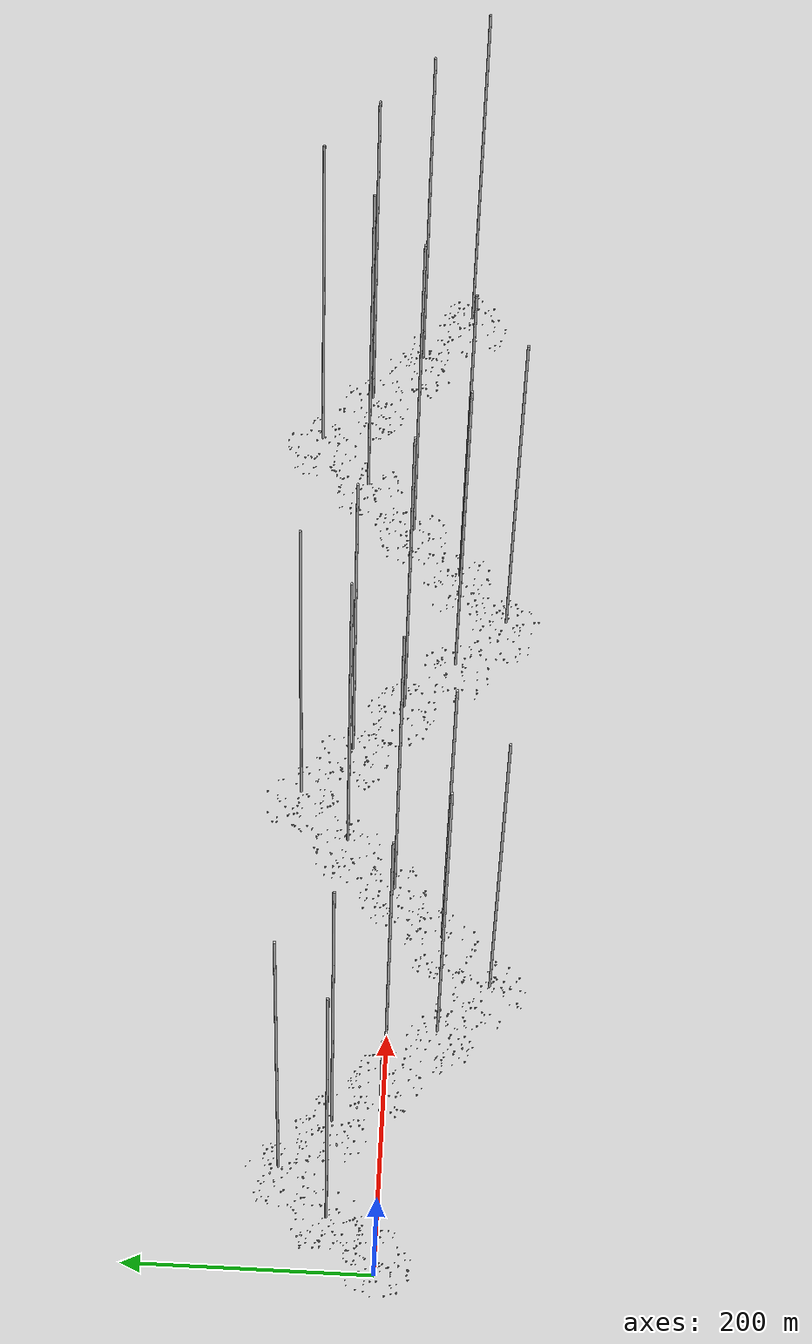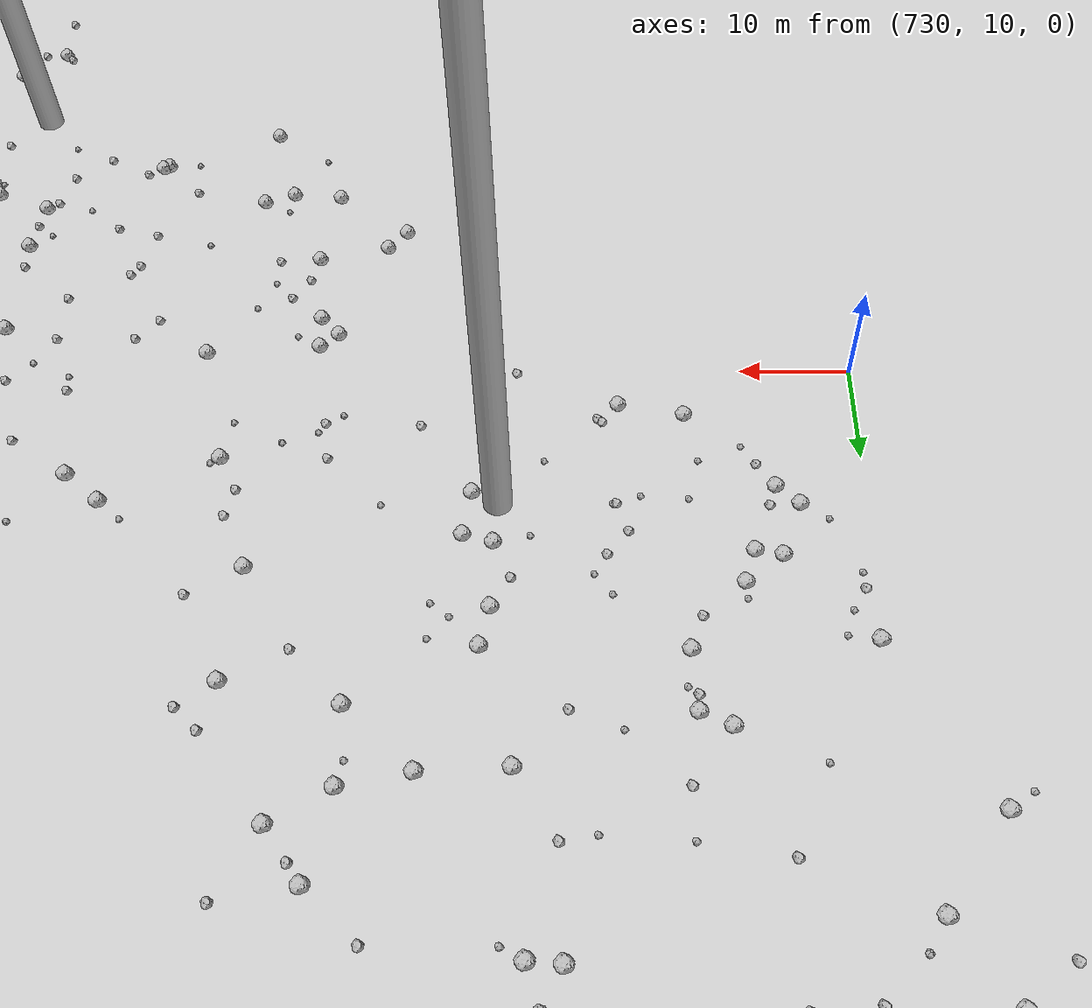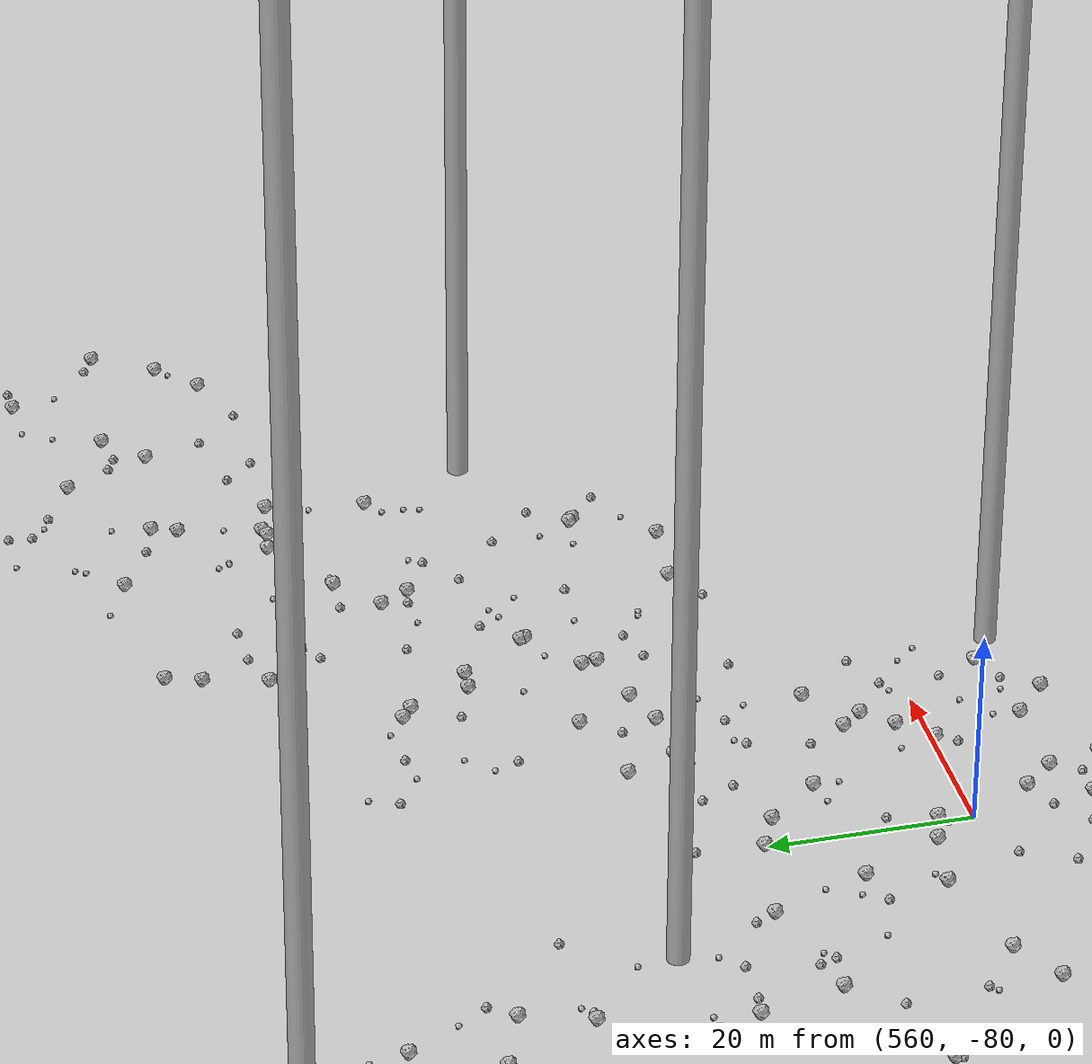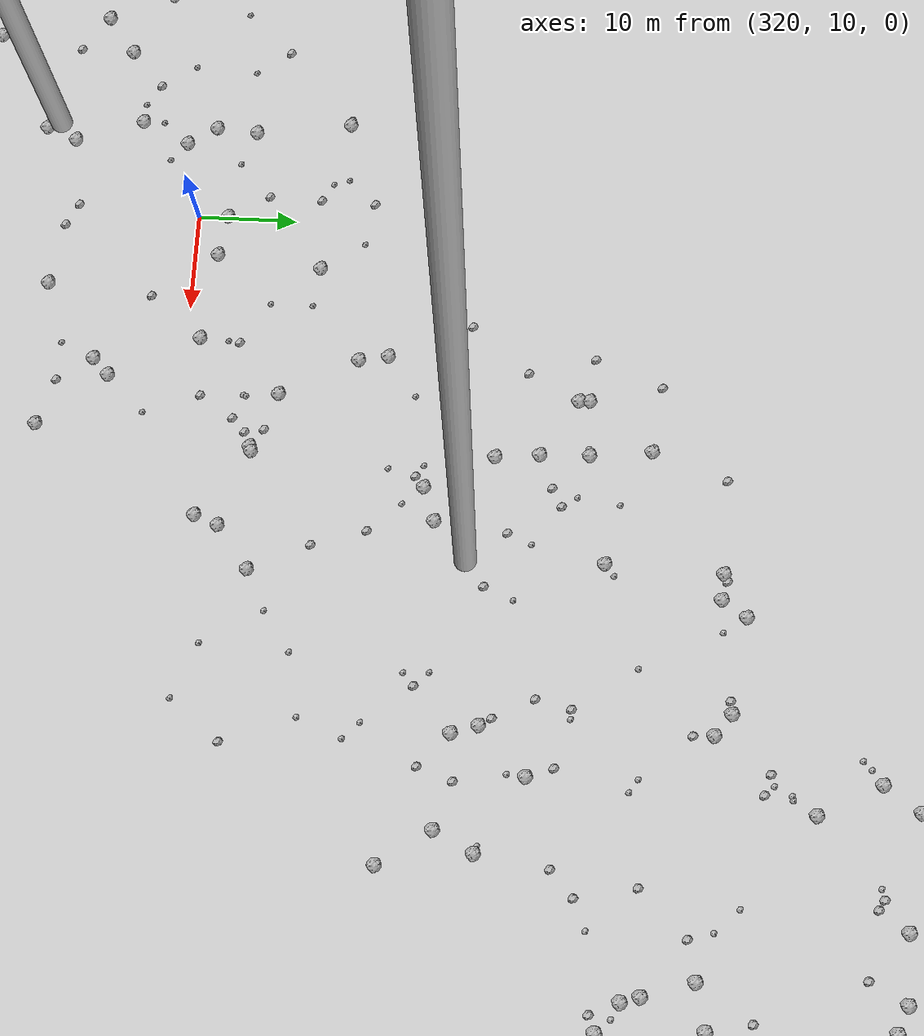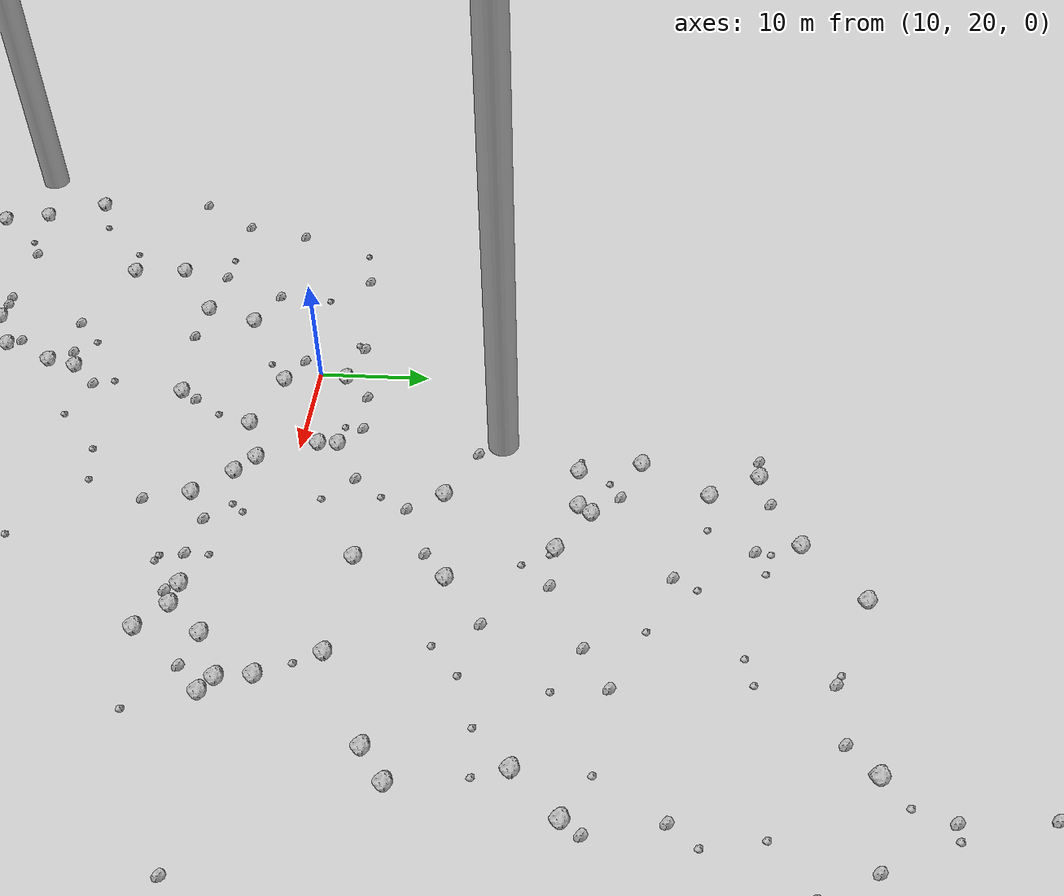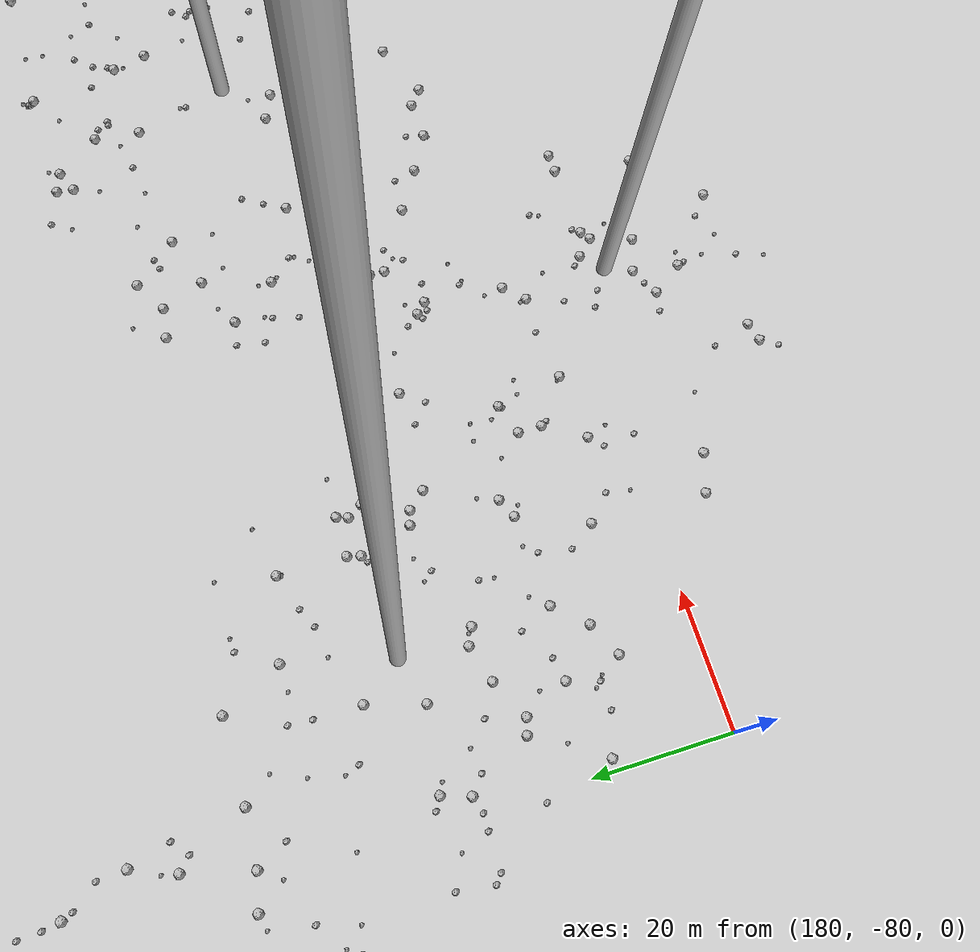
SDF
<sdf version="1.6">
 <world name="default">
  <include><uri>model://custom_ground</uri></include>
  <include><uri>model://sun</uri></include>
  <spherical_coordinates>
   <surface_model>EARTH_WGS84</surface_model>
   <latitude_deg>38.161479</latitude_deg>
   <longitude_deg>-122.454630</longitude_deg>
   <elevation>488.0</elevation>
   <heading_deg>90</heading_deg>
  </spherical_coordinates>
  <model name="rock1_0_0">
   <include><uri>model://rock1</uri><pose>3.6653722886482996 -12.690043998640913 0.5 0 0 0</pose></include>
  </model>
  <model name="rock1_0_1">
   <include><uri>model://rock1</uri><pose>-4.477950558030685 -1.691390897938465 0.5 0 0 0</pose></include>
  </model>
  <model name="rock1_0_2">
   <include><uri>model://rock1</uri><pose>-4.777577840946069 3.320997997242756 0.5 0 0 0</pose></include>
  </model>
  <model name="rock1_0_3">
   <include><uri>model://rock1</uri><pose>13.639573624925973 7.896020157260999 0.5 0 0 0</pose></include>
  </model>
  <model name="rock1_0_4">
   <include><uri>model://rock1</uri><pose>11.477394141677692 16.885441608608673 0.5 0 0 0</pose></include>
  </model>
  <model name="rock1_0_5">
   <include><uri>model://rock1</uri><pose>-13.949360761278978 -13.855348566384297 0.5 0 0 0</pose></include>
  </model>
  <model name="rock1_0_6">
   <include><uri>model://rock1</uri><pose>10.800822188598097 22.484659343086108 0.5 0 0 0</pose></include>
  </model>
  <model name="rock1_0_7">
   <include><uri>model://rock1</uri><pose>10.606213164994948 -3.0906748585599217 0.5 0 0 0</pose></include>
  </model>
  <model name="rock1_0_8">
   <include><uri>model://rock1</uri><pose>9.084160261952583 -18.64845337934864 0.5 0 0 0</pose></include>
  </model>
  <model name="rock1_0_9">
   <include><uri>model://rock1</uri><pose>-2.0617551401197396 -26.593306552363025 0.5 0 0 0</pose></include>
  </model>
  <model name="rock1_0_10">
   <include><uri>model://rock1</uri><pose>1.3256903921759111 7.331870205832374 0.5 0 0 0</pose></include>
  </model>
  <model name="rock1_0_11">
   <include><uri>model://rock1</uri><pose>-12.961444207407666 -18.17183594787869 0.5 0 0 0</pose></include>
  </model>
  <model name="rock1_0_12">
   <include><uri>model://rock1</uri><pose>17.523920949226003 15.004922340389378 0.5 0 0 0</pose></include>
  </model>
  <model name="rock1_0_13">
   <include><uri>model://rock1</uri><pose>36.46131831664435 13.692145170755623 0.5 0 0 0</pose></include>
  </model>
  <model name="rock1_0_14">
   <include><uri>model://rock1</uri><pose>7.767418925283934 -10.549874211157729 0.5 0 0 0</pose></include>
  </model>
  <model name="rock1_0_15">
   <include><uri>model://rock1</uri><pose>18.937846193540217 -18.493103683742525 0.5 0 0 0</pose></include>
  </model>
  <model name="rock1_0_16">
   <include><uri>model://rock1</uri><pose>21.831116692309998 16.54824634742998 0.5 0 0 0</pose></include>
  </model>
  <model name="rock1_0_17">
   <include><uri>model://rock1</uri><pose>2.969939974861397 12.150308465327626 0.5 0 0 0</pose></include>
  </model>
  <model name="rock1_0_18">
   <include><uri>model://rock1</uri><pose>31.987831045671612 -3.1261827631126593 0.5 0 0 0</pose></include>
  </model>
  <model name="rock1_0_19">
   <include><uri>model://rock1</uri><pose>9.911151540201764 -5.812855108611327 0.5 0 0 0</pose></include>
  </model>
  <model name="rock1_0_20">
   <include><uri>model://rock1</uri><pose>1.7695943348375636 -25.565793294236336 0.5 0 0 0</pose></include>
  </model>
  <model name="rock1_0_21">
   <include><uri>model://rock1</uri><pose>23.67440770229367 15.03975940352634 0.5 0 0 0</pose></include>
  </model>
  <model name="rock1_0_22">
   <include><uri>model://rock1</uri><pose>6.5041668381414794 -25.554018394877467 0.5 0 0 0</pose></include>
  </model>
  <model name="rock1_0_23">
   <include><uri>model://rock1</uri><pose>26.416332230866722 12.037307971487039 0.5 0 0 0</pose></include>
  </model>
  <model name="rock1_0_24">
   <include><uri>model://rock1</uri><pose>37.58363993452568 -3.424305759562017 0.5 0 0 0</pose></include>
  </model>
  <model name="rock1_0_25">
   <include><uri>model://rock1</uri><pose>-16.276942137014526 -8.456505364908622 0.5 0 0 0</pose></include>
  </model>
  <model name="rock1_0_26">
   <include><uri>model://rock1</uri><pose>5.586522364051941 -26.394344975217628 0.5 0 0 0</pose></include>
  </model>
  <model name="rock2_0_0">
   <include><uri>model://rock2</uri><pose>28.074142148735945 -5.956948132950089 0.3 0 0 0</pose></include>
  </model>
  <model name="rock2_0_1">
   <include><uri>model://rock2</uri><pose>12.874270640127719 -0.6358530650859997 0.3 0 0 0</pose></include>
  </model>
  <model name="rock2_0_2">
   <include><uri>model://rock2</uri><pose>14.481681217610252 9.388491459637088 0.3 0 0 0</pose></include>
  </model>
  <model name="rock2_0_3">
   <include><uri>model://rock2</uri><pose>5.468855520584775 6.989829308954953 0.3 0 0 0</pose></include>
  </model>
  <model name="rock2_0_4">
   <include><uri>model://rock2</uri><pose>7.0372632263896335 -9.374506497766543 0.3 0 0 0</pose></include>
  </model>
  <model name="rock2_0_5">
   <include><uri>model://rock2</uri><pose>32.649369170769056 -13.41848552926221 0.3 0 0 0</pose></include>
  </model>
  <model name="rock2_0_6">
   <include><uri>model://rock2</uri><pose>0.40926258111181113 -12.690576439196164 0.3 0 0 0</pose></include>
  </model>
  <model name="rock2_0_7">
   <include><uri>model://rock2</uri><pose>23.821508912431817 25.534869538425845 0.3 0 0 0</pose></include>
  </model>
  <model name="rock2_0_8">
   <include><uri>model://rock2</uri><pose>-4.2623632283460555 22.38742617136552 0.3 0 0 0</pose></include>
  </model>
  <model name="rock2_0_9">
   <include><uri>model://rock2</uri><pose>-11.750978510905439 14.321899450277357 0.3 0 0 0</pose></include>
  </model>
  <model name="rock2_0_10">
   <include><uri>model://rock2</uri><pose>14.688733767430897 -23.631470386455828 0.3 0 0 0</pose></include>
  </model>
  <model name="rock2_0_11">
   <include><uri>model://rock2</uri><pose>8.453408975276549 -3.8715465289990156 0.3 0 0 0</pose></include>
  </model>
  <model name="rock2_0_12">
   <include><uri>model://rock2</uri><pose>4.060783924391362 -4.535413510628274 0.3 0 0 0</pose></include>
  </model>
  <model name="rock2_0_13">
   <include><uri>model://rock2</uri><pose>13.31832819716469 24.884935057789136 0.3 0 0 0</pose></include>
  </model>
  <model name="rock2_0_14">
   <include><uri>model://rock2</uri><pose>-17.023265448518075 2.7091794942195193 0.3 0 0 0</pose></include>
  </model>
  <model name="rock2_0_15">
   <include><uri>model://rock2</uri><pose>-4.163594260384739 7.834117887574756 0.3 0 0 0</pose></include>
  </model>
  <model name="rock2_0_16">
   <include><uri>model://rock2</uri><pose>27.21938354605568 8.10013173540527 0.3 0 0 0</pose></include>
  </model>
  <model name="rock2_0_17">
   <include><uri>model://rock2</uri><pose>8.514997603015434 18.25976844554168 0.3 0 0 0</pose></include>
  </model>
  <model name="rock2_0_18">
   <include><uri>model://rock2</uri><pose>-7.0563140349259825 -12.712347111500144 0.3 0 0 0</pose></include>
  </model>
  <model name="rock2_0_19">
   <include><uri>model://rock2</uri><pose>6.408664789028787 23.579927278976882 0.3 0 0 0</pose></include>
  </model>
  <model name="rock2_0_20">
   <include><uri>model://rock2</uri><pose>19.881542448887835 -23.08362045518857 0.3 0 0 0</pose></include>
  </model>
  <model name="rock2_0_21">
   <include><uri>model://rock2</uri><pose>37.703318555077665 -9.668448728774038 0.3 0 0 0</pose></include>
  </model>
  <model name="rock2_0_22">
   <include><uri>model://rock2</uri><pose>-13.158495459357296 8.226917623981315 0.3 0 0 0</pose></include>
  </model>
  <model name="rock2_0_23">
   <include><uri>model://rock2</uri><pose>1.5491353360915525 -12.618656862112417 0.3 0 0 0</pose></include>
  </model>
  <model name="rock2_0_24">
   <include><uri>model://rock2</uri><pose>-1.2754507361684517 13.884630384350281 0.3 0 0 0</pose></include>
  </model>
  <model name="rock2_0_25">
   <include><uri>model://rock2</uri><pose>24.476985142528797 -17.07460310607083 0.3 0 0 0</pose></include>
  </model>
  <model name="rock2_0_26">
   <include><uri>model://rock2</uri><pose>38.06948047756024 -4.92961943082118 0.3 0 0 0</pose></include>
  </model>
  <model name="rock3_0_0">
   <include><uri>model://rock3</uri><pose>17.018567998416806 -1.9826439964069955 0.2 0 0 0</pose></include>
  </model>
  <model name="rock3_0_1">
   <include><uri>model://rock3</uri><pose>25.124490848449888 2.816178166164498 0.2 0 0 0</pose></include>
  </model>
  <model name="rock3_0_2">
   <include><uri>model://rock3</uri><pose>35.98689143192142 -1.8231341943594046 0.2 0 0 0</pose></include>
  </model>
  <model name="rock3_0_3">
   <include><uri>model://rock3</uri><pose>5.813784737937468 22.916431477260275 0.2 0 0 0</pose></include>
  </model>
  <model name="rock3_0_4">
   <include><uri>model://rock3</uri><pose>38.93626670865801 -5.540382894542596 0.2 0 0 0</pose></include>
  </model>
  <model name="rock3_0_5">
   <include><uri>model://rock3</uri><pose>16.25793517354181 11.87558017716892 0.2 0 0 0</pose></include>
  </model>
  <model name="rock3_0_6">
   <include><uri>model://rock3</uri><pose>28.144522716488716 16.776627674913094 0.2 0 0 0</pose></include>
  </model>
  <model name="rock3_0_7">
   <include><uri>model://rock3</uri><pose>21.36927078682878 1.9762556865963958 0.2 0 0 0</pose></include>
  </model>
  <model name="rock3_0_8">
   <include><uri>model://rock3</uri><pose>-5.737843343226212 -18.165015775090417 0.2 0 0 0</pose></include>
  </model>
  <model name="rock3_0_9">
   <include><uri>model://rock3</uri><pose>-12.388157221509044 -6.92794354158524 0.2 0 0 0</pose></include>
  </model>
  <model name="rock3_0_10">
   <include><uri>model://rock3</uri><pose>-7.268967881087294 7.8388376859821065 0.2 0 0 0</pose></include>
  </model>
  <model name="rock3_0_11">
   <include><uri>model://rock3</uri><pose>12.180012539730129 -15.71528286086865 0.2 0 0 0</pose></include>
  </model>
  <model name="rock3_0_12">
   <include><uri>model://rock3</uri><pose>35.9089785628031 -14.28594605438862 0.2 0 0 0</pose></include>
  </model>
  <model name="rock3_0_13">
   <include><uri>model://rock3</uri><pose>-9.2292228261406 -13.89917060804849 0.2 0 0 0</pose></include>
  </model>
  <model name="rock3_0_14">
   <include><uri>model://rock3</uri><pose>8.073408418890978 -19.002898571339507 0.2 0 0 0</pose></include>
  </model>
  <model name="rock3_0_15">
   <include><uri>model://rock3</uri><pose>26.87904573927284 -7.675768062140229 0.2 0 0 0</pose></include>
  </model>
  <model name="rock3_0_16">
   <include><uri>model://rock3</uri><pose>9.006701074835743 15.137543069158724 0.2 0 0 0</pose></include>
  </model>
  <model name="rock3_0_17">
   <include><uri>model://rock3</uri><pose>-1.0131286220202078 18.85513189268446 0.2 0 0 0</pose></include>
  </model>
  <model name="rock3_0_18">
   <include><uri>model://rock3</uri><pose>6.750611120257297 -2.1790638529832407 0.2 0 0 0</pose></include>
  </model>
  <model name="rock3_0_19">
   <include><uri>model://rock3</uri><pose>-8.763685216393917 21.49315786388769 0.2 0 0 0</pose></include>
  </model>
  <model name="rock3_0_20">
   <include><uri>model://rock3</uri><pose>12.260762573937974 1.1551108436835698 0.2 0 0 0</pose></include>
  </model>
  <model name="rock3_0_21">
   <include><uri>model://rock3</uri><pose>31.77925525411601 -2.024136161234196 0.2 0 0 0</pose></include>
  </model>
  <model name="rock3_0_22">
   <include><uri>model://rock3</uri><pose>-7.756349550178745 -2.3338233522838827 0.2 0 0 0</pose></include>
  </model>
  <model name="rock3_0_23">
   <include><uri>model://rock3</uri><pose>33.338406791027616 11.191360958566555 0.2 0 0 0</pose></include>
  </model>
  <model name="rock3_0_24">
   <include><uri>model://rock3</uri><pose>26.767164270684532 -8.487175655272132 0.2 0 0 0</pose></include>
  </model>
  <model name="rock3_0_25">
   <include><uri>model://rock3</uri><pose>14.835527923500393 -28.05687670993492 0.2 0 0 0</pose></include>
  </model>
  <model name="rock3_0_26">
   <include><uri>model://rock3</uri><pose>17.290409752836126 23.519901217436185 0.2 0 0 0</pose></include>
  </model>
  <model name="rock1_1_0">
   <include><uri>model://rock1</uri><pose>21.984185887140345 44.452379824252816 0.5 0 0 0</pose></include>
  </model>
  <model name="rock1_1_1">
   <include><uri>model://rock1</uri><pose>24.263888869585397 55.47849058197807 0.5 0 0 0</pose></include>
  </model>
  <model name="rock1_1_2">
   <include><uri>model://rock1</uri><pose>55.49196884131565 44.605351940681985 0.5 0 0 0</pose></include>
  </model>
  <model name="rock1_1_3">
   <include><uri>model://rock1</uri><pose>67.0581434180481 31.71193665909228 0.5 0 0 0</pose></include>
  </model>
  <model name="rock1_1_4">
   <include><uri>model://rock1</uri><pose>25.389336505799402 33.29669251923824 0.5 0 0 0</pose></include>
  </model>
  <model name="rock1_1_5">
   <include><uri>model://rock1</uri><pose>46.55425848364332 17.741849226924238 0.5 0 0 0</pose></include>
  </model>
  <model name="rock1_1_6">
   <include><uri>model://rock1</uri><pose>34.628318768431484 34.41076125274306 0.5 0 0 0</pose></include>
  </model>
  <model name="rock1_1_7">
   <include><uri>model://rock1</uri><pose>41.247815575748206 16.53812630213894 0.5 0 0 0</pose></include>
  </model>
  <model name="rock1_1_8">
   <include><uri>model://rock1</uri><pose>21.767863700532498 59.77395149690714 0.5 0 0 0</pose></include>
  </model>
  <model name="rock1_1_9">
   <include><uri>model://rock1</uri><pose>50.57209258481825 30.365658909128335 0.5 0 0 0</pose></include>
  </model>
  <model name="rock1_1_10">
   <include><uri>model://rock1</uri><pose>50.85151155455921 66.44675923895413 0.5 0 0 0</pose></include>
  </model>
  <model name="rock1_1_11">
   <include><uri>model://rock1</uri><pose>42.48115638185332 26.202876635867916 0.5 0 0 0</pose></include>
  </model>
  <model name="rock1_1_12">
   <include><uri>model://rock1</uri><pose>31.000133099568387 42.93750145202175 0.5 0 0 0</pose></include>
  </model>
  <model name="rock1_1_13">
   <include><uri>model://rock1</uri><pose>44.84691181197364 21.449309129694072 0.5 0 0 0</pose></include>
  </model>
  <model name="rock1_1_14">
   <include><uri>model://rock1</uri><pose>20.7560481815524 49.79393407152179 0.5 0 0 0</pose></include>
  </model>
  <model name="rock1_1_15">
   <include><uri>model://rock1</uri><pose>26.879040845791543 45.6603778992715 0.5 0 0 0</pose></include>
  </model>
  <model name="rock1_1_16">
   <include><uri>model://rock1</uri><pose>35.00872036256388 67.40044139854673 0.5 0 0 0</pose></include>
  </model>
  <model name="rock1_1_17">
   <include><uri>model://rock1</uri><pose>40.969827153212044 11.335780547821683 0.5 0 0 0</pose></include>
  </model>
  <model name="rock1_1_18">
   <include><uri>model://rock1</uri><pose>53.36028370621758 32.36027622625724 0.5 0 0 0</pose></include>
  </model>
  <model name="rock1_1_19">
   <include><uri>model://rock1</uri><pose>26.0814612765888 44.56841892507201 0.5 0 0 0</pose></include>
  </model>
  <model name="rock1_1_20">
   <include><uri>model://rock1</uri><pose>38.54351602515755 13.454481302041428 0.5 0 0 0</pose></include>
  </model>
  <model name="rock1_1_21">
   <include><uri>model://rock1</uri><pose>51.762755461365316 40.960364797044235 0.5 0 0 0</pose></include>
  </model>
  <model name="rock1_1_22">
   <include><uri>model://rock1</uri><pose>32.81520333371819 26.848353453547226 0.5 0 0 0</pose></include>
  </model>
  <model name="rock1_1_23">
   <include><uri>model://rock1</uri><pose>29.512839935601807 62.69747285308068 0.5 0 0 0</pose></include>
  </model>
  <model name="rock1_1_24">
   <include><uri>model://rock1</uri><pose>19.785768992084947 21.53482562733852 0.5 0 0 0</pose></include>
  </model>
  <model name="rock1_1_25">
   <include><uri>model://rock1</uri><pose>45.22035189101767 18.65059760300997 0.5 0 0 0</pose></include>
  </model>
  <model name="rock1_1_26">
   <include><uri>model://rock1</uri><pose>19.714953848786212 23.251686237676928 0.5 0 0 0</pose></include>
  </model>
  <model name="rock2_1_0">
   <include><uri>model://rock2</uri><pose>44.237375889177414 15.689007313308752 0.3 0 0 0</pose></include>
  </model>
  <model name="rock2_1_1">
   <include><uri>model://rock2</uri><pose>30.293041791701942 59.022320652782014 0.3 0 0 0</pose></include>
  </model>
  <model name="rock2_1_2">
   <include><uri>model://rock2</uri><pose>25.5099695320882 44.6650657220586 0.3 0 0 0</pose></include>
  </model>
  <model name="rock2_1_3">
   <include><uri>model://rock2</uri><pose>19.750465108404196 59.91273368983635 0.3 0 0 0</pose></include>
  </model>
  <model name="rock2_1_4">
   <include><uri>model://rock2</uri><pose>29.241215898044494 13.80496932822071 0.3 0 0 0</pose></include>
  </model>
  <model name="rock2_1_5">
   <include><uri>model://rock2</uri><pose>27.17295642430884 30.38506610035758 0.3 0 0 0</pose></include>
  </model>
  <model name="rock2_1_6">
   <include><uri>model://rock2</uri><pose>24.8561321314034 60.58271095835893 0.3 0 0 0</pose></include>
  </model>
  <model name="rock2_1_7">
   <include><uri>model://rock2</uri><pose>43.11510845052758 64.26457610695168 0.3 0 0 0</pose></include>
  </model>
  <model name="rock2_1_8">
   <include><uri>model://rock2</uri><pose>68.98242993341265 44.07039974097278 0.3 0 0 0</pose></include>
  </model>
  <model name="rock2_1_9">
   <include><uri>model://rock2</uri><pose>48.31225672332503 64.40849811868239 0.3 0 0 0</pose></include>
  </model>
  <model name="rock2_1_10">
   <include><uri>model://rock2</uri><pose>37.08227140769503 12.69800883604869 0.3 0 0 0</pose></include>
  </model>
  <model name="rock2_1_11">
   <include><uri>model://rock2</uri><pose>55.25619802280217 51.82241965171521 0.3 0 0 0</pose></include>
  </model>
  <model name="rock2_1_12">
   <include><uri>model://rock2</uri><pose>33.109109095759294 13.242094332929444 0.3 0 0 0</pose></include>
  </model>
  <model name="rock2_1_13">
   <include><uri>model://rock2</uri><pose>40.859480876441225 45.59073411209479 0.3 0 0 0</pose></include>
  </model>
  <model name="rock2_1_14">
   <include><uri>model://rock2</uri><pose>56.491321693382375 46.101604486889066 0.3 0 0 0</pose></include>
  </model>
  <model name="rock2_1_15">
   <include><uri>model://rock2</uri><pose>38.99794040797164 37.688536184623835 0.3 0 0 0</pose></include>
  </model>
  <model name="rock2_1_16">
   <include><uri>model://rock2</uri><pose>33.44808780702736 52.38857518266885 0.3 0 0 0</pose></include>
  </model>
  <model name="rock2_1_17">
   <include><uri>model://rock2</uri><pose>67.26757245056083 50.54577001262772 0.3 0 0 0</pose></include>
  </model>
  <model name="rock2_1_18">
   <include><uri>model://rock2</uri><pose>17.511690948709735 25.157379992423657 0.3 0 0 0</pose></include>
  </model>
  <model name="rock2_1_19">
   <include><uri>model://rock2</uri><pose>20.198914357216225 35.71882757648055 0.3 0 0 0</pose></include>
  </model>
  <model name="rock2_1_20">
   <include><uri>model://rock2</uri><pose>66.0017777728875 49.07546353412402 0.3 0 0 0</pose></include>
  </model>
  <model name="rock2_1_21">
   <include><uri>model://rock2</uri><pose>61.8090719192577 58.193219247827265 0.3 0 0 0</pose></include>
  </model>
  <model name="rock2_1_22">
   <include><uri>model://rock2</uri><pose>44.453376087428026 47.67059538320972 0.3 0 0 0</pose></include>
  </model>
  <model name="rock2_1_23">
   <include><uri>model://rock2</uri><pose>24.773004364431362 48.08531949081751 0.3 0 0 0</pose></include>
  </model>
  <model name="rock2_1_24">
   <include><uri>model://rock2</uri><pose>61.033440896905326 18.916098825309874 0.3 0 0 0</pose></include>
  </model>
  <model name="rock2_1_25">
   <include><uri>model://rock2</uri><pose>34.8486750656495 42.73193701167192 0.3 0 0 0</pose></include>
  </model>
  <model name="rock2_1_26">
   <include><uri>model://rock2</uri><pose>32.05270307384214 32.52407157034803 0.3 0 0 0</pose></include>
  </model>
  <model name="rock3_1_0">
   <include><uri>model://rock3</uri><pose>44.88980489397052 43.32757146900815 0.2 0 0 0</pose></include>
  </model>
  <model name="rock3_1_1">
   <include><uri>model://rock3</uri><pose>33.026384223056155 15.151929504242654 0.2 0 0 0</pose></include>
  </model>
  <model name="rock3_1_2">
   <include><uri>model://rock3</uri><pose>23.085823065809514 47.1422365639241 0.2 0 0 0</pose></include>
  </model>
  <model name="rock3_1_3">
   <include><uri>model://rock3</uri><pose>30.40543917602541 60.25928908622367 0.2 0 0 0</pose></include>
  </model>
  <model name="rock3_1_4">
   <include><uri>model://rock3</uri><pose>42.15350581456738 64.70707839703921 0.2 0 0 0</pose></include>
  </model>
  <model name="rock3_1_5">
   <include><uri>model://rock3</uri><pose>25.770546200402727 27.971411030989305 0.2 0 0 0</pose></include>
  </model>
  <model name="rock3_1_6">
   <include><uri>model://rock3</uri><pose>56.92964032514898 53.89318975909294 0.2 0 0 0</pose></include>
  </model>
  <model name="rock3_1_7">
   <include><uri>model://rock3</uri><pose>38.895460842378945 50.30219992450404 0.2 0 0 0</pose></include>
  </model>
  <model name="rock3_1_8">
   <include><uri>model://rock3</uri><pose>20.514165202453086 44.61473237476774 0.2 0 0 0</pose></include>
  </model>
  <model name="rock3_1_9">
   <include><uri>model://rock3</uri><pose>43.4492173706513 58.22401409631128 0.2 0 0 0</pose></include>
  </model>
  <model name="rock3_1_10">
   <include><uri>model://rock3</uri><pose>41.02920326064215 57.65433542701088 0.2 0 0 0</pose></include>
  </model>
  <model name="rock3_1_11">
   <include><uri>model://rock3</uri><pose>26.252679277878926 23.00822172201662 0.2 0 0 0</pose></include>
  </model>
  <model name="rock3_1_12">
   <include><uri>model://rock3</uri><pose>48.342736144128544 37.97933345406618 0.2 0 0 0</pose></include>
  </model>
  <model name="rock3_1_13">
   <include><uri>model://rock3</uri><pose>33.94478758724077 10.979253744446126 0.2 0 0 0</pose></include>
  </model>
  <model name="rock3_1_14">
   <include><uri>model://rock3</uri><pose>32.646590688778105 40.31775027868405 0.2 0 0 0</pose></include>
  </model>
  <model name="rock3_1_15">
   <include><uri>model://rock3</uri><pose>41.19332820352331 34.158871416392486 0.2 0 0 0</pose></include>
  </model>
  <model name="rock3_1_16">
   <include><uri>model://rock3</uri><pose>48.20816006934146 12.430735646729659 0.2 0 0 0</pose></include>
  </model>
  <model name="rock3_1_17">
   <include><uri>model://rock3</uri><pose>51.79144841057881 46.65750910849231 0.2 0 0 0</pose></include>
  </model>
  <model name="rock3_1_18">
   <include><uri>model://rock3</uri><pose>27.975657290571338 55.24058346970357 0.2 0 0 0</pose></include>
  </model>
  <model name="rock3_1_19">
   <include><uri>model://rock3</uri><pose>34.50223337560112 54.277633670759414 0.2 0 0 0</pose></include>
  </model>
  <model name="rock3_1_20">
   <include><uri>model://rock3</uri><pose>56.08052129808345 58.440892417434334 0.2 0 0 0</pose></include>
  </model>
  <model name="rock3_1_21">
   <include><uri>model://rock3</uri><pose>32.511181250108905 59.730479281532006 0.2 0 0 0</pose></include>
  </model>
  <model name="rock3_1_22">
   <include><uri>model://rock3</uri><pose>43.838752242401306 36.403840242504685 0.2 0 0 0</pose></include>
  </model>
  <model name="rock3_1_23">
   <include><uri>model://rock3</uri><pose>52.43003256455648 38.281213083752604 0.2 0 0 0</pose></include>
  </model>
  <model name="rock3_1_24">
   <include><uri>model://rock3</uri><pose>31.44887116974043 42.51491660479222 0.2 0 0 0</pose></include>
  </model>
  <model name="rock3_1_25">
   <include><uri>model://rock3</uri><pose>43.4224167075611 24.058034216235477 0.2 0 0 0</pose></include>
  </model>
  <model name="rock3_1_26">
   <include><uri>model://rock3</uri><pose>27.274216439119837 15.729308235088581 0.2 0 0 0</pose></include>
  </model>
  <model name="rock1_2_0">
   <include><uri>model://rock1</uri><pose>60.8555159674455 61.14562882135752 0.5 0 0 0</pose></include>
  </model>
  <model name="rock1_2_1">
   <include><uri>model://rock1</uri><pose>71.09891276884974 93.45341397258919 0.5 0 0 0</pose></include>
  </model>
  <model name="rock1_2_2">
   <include><uri>model://rock1</uri><pose>95.82224702898199 56.312324643940734 0.5 0 0 0</pose></include>
  </model>
  <model name="rock1_2_3">
   <include><uri>model://rock1</uri><pose>89.26750335274622 71.5041502556614 0.5 0 0 0</pose></include>
  </model>
  <model name="rock1_2_4">
   <include><uri>model://rock1</uri><pose>80.14346938634375 86.8175104121091 0.5 0 0 0</pose></include>
  </model>
  <model name="rock1_2_5">
   <include><uri>model://rock1</uri><pose>87.65077425759907 87.18470729052115 0.5 0 0 0</pose></include>
  </model>
  <model name="rock1_2_6">
   <include><uri>model://rock1</uri><pose>87.92572270421141 86.93003991052173 0.5 0 0 0</pose></include>
  </model>
  <model name="rock1_2_7">
   <include><uri>model://rock1</uri><pose>89.9919260731319 66.32595613771814 0.5 0 0 0</pose></include>
  </model>
  <model name="rock1_2_8">
   <include><uri>model://rock1</uri><pose>92.97404906987413 66.3692046932224 0.5 0 0 0</pose></include>
  </model>
  <model name="rock1_2_9">
   <include><uri>model://rock1</uri><pose>70.79290746695523 59.685559267207715 0.5 0 0 0</pose></include>
  </model>
  <model name="rock1_2_10">
   <include><uri>model://rock1</uri><pose>66.65195768239957 75.16068665692801 0.5 0 0 0</pose></include>
  </model>
  <model name="rock1_2_11">
   <include><uri>model://rock1</uri><pose>101.96231973203942 86.08146440641467 0.5 0 0 0</pose></include>
  </model>
  <model name="rock1_2_12">
   <include><uri>model://rock1</uri><pose>78.28597107570089 60.77722171616223 0.5 0 0 0</pose></include>
  </model>
  <model name="rock1_2_13">
   <include><uri>model://rock1</uri><pose>92.28229348694535 58.14197250884263 0.5 0 0 0</pose></include>
  </model>
  <model name="rock1_2_14">
   <include><uri>model://rock1</uri><pose>100.19242097064092 90.29803259260453 0.5 0 0 0</pose></include>
  </model>
  <model name="rock1_2_15">
   <include><uri>model://rock1</uri><pose>96.22211290295186 92.34625978261991 0.5 0 0 0</pose></include>
  </model>
  <model name="rock1_2_16">
   <include><uri>model://rock1</uri><pose>57.300612014588246 88.63583697927746 0.5 0 0 0</pose></include>
  </model>
  <model name="rock1_2_17">
   <include><uri>model://rock1</uri><pose>98.44284240172973 85.98344522601788 0.5 0 0 0</pose></include>
  </model>
  <model name="rock1_2_18">
   <include><uri>model://rock1</uri><pose>84.32634145256341 85.90072948798036 0.5 0 0 0</pose></include>
  </model>
  <model name="rock1_2_19">
   <include><uri>model://rock1</uri><pose>77.70508072973325 91.80150066511214 0.5 0 0 0</pose></include>
  </model>
  <model name="rock1_2_20">
   <include><uri>model://rock1</uri><pose>65.11429751527673 77.37727776900063 0.5 0 0 0</pose></include>
  </model>
  <model name="rock1_2_21">
   <include><uri>model://rock1</uri><pose>84.14157777656497 77.37475982166217 0.5 0 0 0</pose></include>
  </model>
  <model name="rock1_2_22">
   <include><uri>model://rock1</uri><pose>65.3656459919172 77.15658143206485 0.5 0 0 0</pose></include>
  </model>
  <model name="rock1_2_23">
   <include><uri>model://rock1</uri><pose>84.85457687341876 70.38999425613639 0.5 0 0 0</pose></include>
  </model>
  <model name="rock1_2_24">
   <include><uri>model://rock1</uri><pose>104.31521356042542 81.83427798655403 0.5 0 0 0</pose></include>
  </model>
  <model name="rock1_2_25">
   <include><uri>model://rock1</uri><pose>77.45482953079775 59.90388404915816 0.5 0 0 0</pose></include>
  </model>
  <model name="rock1_2_26">
   <include><uri>model://rock1</uri><pose>96.54610211505832 78.44962673721133 0.5 0 0 0</pose></include>
  </model>
  <model name="rock2_2_0">
   <include><uri>model://rock2</uri><pose>86.51413937001522 91.11752486222537 0.3 0 0 0</pose></include>
  </model>
  <model name="rock2_2_1">
   <include><uri>model://rock2</uri><pose>80.70453855202749 73.13980493886253 0.3 0 0 0</pose></include>
  </model>
  <model name="rock2_2_2">
   <include><uri>model://rock2</uri><pose>106.98343602468726 66.93052776438563 0.3 0 0 0</pose></include>
  </model>
  <model name="rock2_2_3">
   <include><uri>model://rock2</uri><pose>91.71864016983398 56.608534540520935 0.3 0 0 0</pose></include>
  </model>
  <model name="rock2_2_4">
   <include><uri>model://rock2</uri><pose>58.351837994363 95.43566760426664 0.3 0 0 0</pose></include>
  </model>
  <model name="rock2_2_5">
   <include><uri>model://rock2</uri><pose>76.94644165999502 77.25093138699225 0.3 0 0 0</pose></include>
  </model>
  <model name="rock2_2_6">
   <include><uri>model://rock2</uri><pose>103.11064541774698 93.61339859531273 0.3 0 0 0</pose></include>
  </model>
  <model name="rock2_2_7">
   <include><uri>model://rock2</uri><pose>92.57603704823183 92.72218210568913 0.3 0 0 0</pose></include>
  </model>
  <model name="rock2_2_8">
   <include><uri>model://rock2</uri><pose>61.52247684185331 59.043361649234555 0.3 0 0 0</pose></include>
  </model>
  <model name="rock2_2_9">
   <include><uri>model://rock2</uri><pose>73.06823077463227 83.25859689075337 0.3 0 0 0</pose></include>
  </model>
  <model name="rock2_2_10">
   <include><uri>model://rock2</uri><pose>73.3432509755451 95.6499822131978 0.3 0 0 0</pose></include>
  </model>
  <model name="rock2_2_11">
   <include><uri>model://rock2</uri><pose>90.82848561767972 88.66573986828215 0.3 0 0 0</pose></include>
  </model>
  <model name="rock2_2_12">
   <include><uri>model://rock2</uri><pose>74.31786214051658 83.88238333611804 0.3 0 0 0</pose></include>
  </model>
  <model name="rock2_2_13">
   <include><uri>model://rock2</uri><pose>103.72391678859768 64.25667677058038 0.3 0 0 0</pose></include>
  </model>
  <model name="rock2_2_14">
   <include><uri>model://rock2</uri><pose>105.27263495211028 79.77894963158643 0.3 0 0 0</pose></include>
  </model>
  <model name="rock2_2_15">
   <include><uri>model://rock2</uri><pose>68.58833338318624 55.946711180023 0.3 0 0 0</pose></include>
  </model>
  <model name="rock2_2_16">
   <include><uri>model://rock2</uri><pose>53.51552512335359 78.11521363471795 0.3 0 0 0</pose></include>
  </model>
  <model name="rock2_2_17">
   <include><uri>model://rock2</uri><pose>81.17893684783475 51.38190737501889 0.3 0 0 0</pose></include>
  </model>
  <model name="rock2_2_18">
   <include><uri>model://rock2</uri><pose>58.084702296480835 65.65410307928917 0.3 0 0 0</pose></include>
  </model>
  <model name="rock2_2_19">
   <include><uri>model://rock2</uri><pose>69.58036068389177 55.8581380592054 0.3 0 0 0</pose></include>
  </model>
  <model name="rock2_2_20">
   <include><uri>model://rock2</uri><pose>89.67509728648733 103.22179167385883 0.3 0 0 0</pose></include>
  </model>
  <model name="rock2_2_21">
   <include><uri>model://rock2</uri><pose>54.11905325527896 71.25676920738762 0.3 0 0 0</pose></include>
  </model>
  <model name="rock2_2_22">
   <include><uri>model://rock2</uri><pose>105.0428268325377 87.2314092050712 0.3 0 0 0</pose></include>
  </model>
  <model name="rock2_2_23">
   <include><uri>model://rock2</uri><pose>85.2502051601918 106.14803395422649 0.3 0 0 0</pose></include>
  </model>
  <model name="rock2_2_24">
   <include><uri>model://rock2</uri><pose>63.655783237345986 98.34579865399748 0.3 0 0 0</pose></include>
  </model>
  <model name="rock2_2_25">
   <include><uri>model://rock2</uri><pose>60.869517954380555 87.18334254505987 0.3 0 0 0</pose></include>
  </model>
  <model name="rock2_2_26">
   <include><uri>model://rock2</uri><pose>92.75764291330157 58.88801423379974 0.3 0 0 0</pose></include>
  </model>
  <model name="rock3_2_0">
   <include><uri>model://rock3</uri><pose>75.464577162798 61.232482463618766 0.2 0 0 0</pose></include>
  </model>
  <model name="rock3_2_1">
   <include><uri>model://rock3</uri><pose>55.39062249768992 71.26486246818135 0.2 0 0 0</pose></include>
  </model>
  <model name="rock3_2_2">
   <include><uri>model://rock3</uri><pose>65.12371917590434 94.21604589587827 0.2 0 0 0</pose></include>
  </model>
  <model name="rock3_2_3">
   <include><uri>model://rock3</uri><pose>90.01731549182989 67.78337240519022 0.2 0 0 0</pose></include>
  </model>
  <model name="rock3_2_4">
   <include><uri>model://rock3</uri><pose>53.073217047460346 68.30633637791657 0.2 0 0 0</pose></include>
  </model>
  <model name="rock3_2_5">
   <include><uri>model://rock3</uri><pose>63.16357868613514 99.03845582600266 0.2 0 0 0</pose></include>
  </model>
  <model name="rock3_2_6">
   <include><uri>model://rock3</uri><pose>72.97657517521691 90.8016671459182 0.2 0 0 0</pose></include>
  </model>
  <model name="rock3_2_7">
   <include><uri>model://rock3</uri><pose>55.07021711420556 87.26746948240407 0.2 0 0 0</pose></include>
  </model>
  <model name="rock3_2_8">
   <include><uri>model://rock3</uri><pose>102.6208139047555 86.20741402558305 0.2 0 0 0</pose></include>
  </model>
  <model name="rock3_2_9">
   <include><uri>model://rock3</uri><pose>100.94121500414676 76.1044264004963 0.2 0 0 0</pose></include>
  </model>
  <model name="rock3_2_10">
   <include><uri>model://rock3</uri><pose>56.444851531391734 96.32962606435356 0.2 0 0 0</pose></include>
  </model>
  <model name="rock3_2_11">
   <include><uri>model://rock3</uri><pose>60.25843111733485 92.13275604439565 0.2 0 0 0</pose></include>
  </model>
  <model name="rock3_2_12">
   <include><uri>model://rock3</uri><pose>82.63208517824441 58.26503902531476 0.2 0 0 0</pose></include>
  </model>
  <model name="rock3_2_13">
   <include><uri>model://rock3</uri><pose>97.34589417780006 65.240262795738 0.2 0 0 0</pose></include>
  </model>
  <model name="rock3_2_14">
   <include><uri>model://rock3</uri><pose>69.78749111486985 82.32354071451965 0.2 0 0 0</pose></include>
  </model>
  <model name="rock3_2_15">
   <include><uri>model://rock3</uri><pose>77.80484590648261 64.2984558921931 0.2 0 0 0</pose></include>
  </model>
  <model name="rock3_2_16">
   <include><uri>model://rock3</uri><pose>58.25807764813032 84.80166048881672 0.2 0 0 0</pose></include>
  </model>
  <model name="rock3_2_17">
   <include><uri>model://rock3</uri><pose>85.70569337071191 77.06999404699674 0.2 0 0 0</pose></include>
  </model>
  <model name="rock3_2_18">
   <include><uri>model://rock3</uri><pose>82.03599860993725 77.34746655512032 0.2 0 0 0</pose></include>
  </model>
  <model name="rock3_2_19">
   <include><uri>model://rock3</uri><pose>79.12784432980374 57.86051568872959 0.2 0 0 0</pose></include>
  </model>
  <model name="rock3_2_20">
   <include><uri>model://rock3</uri><pose>101.99190235913275 85.94911438880652 0.2 0 0 0</pose></include>
  </model>
  <model name="rock3_2_21">
   <include><uri>model://rock3</uri><pose>64.18675029004879 64.35218495983997 0.2 0 0 0</pose></include>
  </model>
  <model name="rock3_2_22">
   <include><uri>model://rock3</uri><pose>103.42140083083316 84.0265216187409 0.2 0 0 0</pose></include>
  </model>
  <model name="rock3_2_23">
   <include><uri>model://rock3</uri><pose>92.8755092623766 84.65659902793429 0.2 0 0 0</pose></include>
  </model>
  <model name="rock3_2_24">
   <include><uri>model://rock3</uri><pose>90.32960378497683 99.38869092086763 0.2 0 0 0</pose></include>
  </model>
  <model name="rock3_2_25">
   <include><uri>model://rock3</uri><pose>90.70755692644806 76.4742279871789 0.2 0 0 0</pose></include>
  </model>
  <model name="rock3_2_26">
   <include><uri>model://rock3</uri><pose>99.15308059395227 93.15427776473092 0.2 0 0 0</pose></include>
  </model>
  <model name="rock1_3_0">
   <include><uri>model://rock1</uri><pose>100.76346080717205 17.612694388703904 0.5 0 0 0</pose></include>
  </model>
  <model name="rock1_3_1">
   <include><uri>model://rock1</uri><pose>123.75137834676028 18.00111754785835 0.5 0 0 0</pose></include>
  </model>
  <model name="rock1_3_2">
   <include><uri>model://rock1</uri><pose>123.43226251302886 31.876252323198365 0.5 0 0 0</pose></include>
  </model>
  <model name="rock1_3_3">
   <include><uri>model://rock1</uri><pose>122.72743271777082 24.665636610516877 0.5 0 0 0</pose></include>
  </model>
  <model name="rock1_3_4">
   <include><uri>model://rock1</uri><pose>125.29752512465176 26.438996091776463 0.5 0 0 0</pose></include>
  </model>
  <model name="rock1_3_5">
   <include><uri>model://rock1</uri><pose>119.72926284062714 50.051400766853696 0.5 0 0 0</pose></include>
  </model>
  <model name="rock1_3_6">
   <include><uri>model://rock1</uri><pose>122.4991771782018 39.506991586835404 0.5 0 0 0</pose></include>
  </model>
  <model name="rock1_3_7">
   <include><uri>model://rock1</uri><pose>110.47648878040222 21.72807385842019 0.5 0 0 0</pose></include>
  </model>
  <model name="rock1_3_8">
   <include><uri>model://rock1</uri><pose>140.41437144613954 46.14266512788404 0.5 0 0 0</pose></include>
  </model>
  <model name="rock1_3_9">
   <include><uri>model://rock1</uri><pose>128.01407766982672 19.33354867410611 0.5 0 0 0</pose></include>
  </model>
  <model name="rock1_3_10">
   <include><uri>model://rock1</uri><pose>100.92975698767424 45.572219476153386 0.5 0 0 0</pose></include>
  </model>
  <model name="rock1_3_11">
   <include><uri>model://rock1</uri><pose>120.57804787550462 46.5506441382615 0.5 0 0 0</pose></include>
  </model>
  <model name="rock1_3_12">
   <include><uri>model://rock1</uri><pose>140.89767446770088 51.05772106725337 0.5 0 0 0</pose></include>
  </model>
  <model name="rock1_3_13">
   <include><uri>model://rock1</uri><pose>99.70671466428527 23.732550622379776 0.5 0 0 0</pose></include>
  </model>
  <model name="rock1_3_14">
   <include><uri>model://rock1</uri><pose>121.21926128127588 15.114335241079413 0.5 0 0 0</pose></include>
  </model>
  <model name="rock1_3_15">
   <include><uri>model://rock1</uri><pose>139.91571564299232 25.865006542565414 0.5 0 0 0</pose></include>
  </model>
  <model name="rock1_3_16">
   <include><uri>model://rock1</uri><pose>118.20700010609923 29.50130429281556 0.5 0 0 0</pose></include>
  </model>
  <model name="rock1_3_17">
   <include><uri>model://rock1</uri><pose>124.87572674065862 68.69490013791786 0.5 0 0 0</pose></include>
  </model>
  <model name="rock1_3_18">
   <include><uri>model://rock1</uri><pose>106.35767854532256 34.98299672183062 0.5 0 0 0</pose></include>
  </model>
  <model name="rock1_3_19">
   <include><uri>model://rock1</uri><pose>117.23554517801954 47.72398920892182 0.5 0 0 0</pose></include>
  </model>
  <model name="rock1_3_20">
   <include><uri>model://rock1</uri><pose>92.72175384909194 45.15537962985626 0.5 0 0 0</pose></include>
  </model>
  <model name="rock1_3_21">
   <include><uri>model://rock1</uri><pose>127.07946579872434 57.77645067274089 0.5 0 0 0</pose></include>
  </model>
  <model name="rock1_3_22">
   <include><uri>model://rock1</uri><pose>114.2705957175263 54.7887173169327 0.5 0 0 0</pose></include>
  </model>
  <model name="rock1_3_23">
   <include><uri>model://rock1</uri><pose>129.65183429782738 54.596291538959704 0.5 0 0 0</pose></include>
  </model>
  <model name="rock1_3_24">
   <include><uri>model://rock1</uri><pose>119.18674897241321 68.0322536276004 0.5 0 0 0</pose></include>
  </model>
  <model name="rock1_3_25">
   <include><uri>model://rock1</uri><pose>141.62443026820964 22.619333137206098 0.5 0 0 0</pose></include>
  </model>
  <model name="rock1_3_26">
   <include><uri>model://rock1</uri><pose>146.67733030225395 48.69173359618524 0.5 0 0 0</pose></include>
  </model>
  <model name="rock2_3_0">
   <include><uri>model://rock2</uri><pose>99.58373715818158 28.31298570437714 0.3 0 0 0</pose></include>
  </model>
  <model name="rock2_3_1">
   <include><uri>model://rock2</uri><pose>107.61365142680545 35.45482922217296 0.3 0 0 0</pose></include>
  </model>
  <model name="rock2_3_2">
   <include><uri>model://rock2</uri><pose>114.44850663598123 40.729657929325754 0.3 0 0 0</pose></include>
  </model>
  <model name="rock2_3_3">
   <include><uri>model://rock2</uri><pose>114.23065234354864 64.97298852052367 0.3 0 0 0</pose></include>
  </model>
  <model name="rock2_3_4">
   <include><uri>model://rock2</uri><pose>115.65949824189983 59.79143998540765 0.3 0 0 0</pose></include>
  </model>
  <model name="rock2_3_5">
   <include><uri>model://rock2</uri><pose>118.11888052329708 50.38271635843053 0.3 0 0 0</pose></include>
  </model>
  <model name="rock2_3_6">
   <include><uri>model://rock2</uri><pose>110.76593258392055 12.26689294716979 0.3 0 0 0</pose></include>
  </model>
  <model name="rock2_3_7">
   <include><uri>model://rock2</uri><pose>140.79285061932524 46.76625198371181 0.3 0 0 0</pose></include>
  </model>
  <model name="rock2_3_8">
   <include><uri>model://rock2</uri><pose>144.05230533268718 53.21228445152708 0.3 0 0 0</pose></include>
  </model>
  <model name="rock2_3_9">
   <include><uri>model://rock2</uri><pose>99.98524270898834 47.69988846606809 0.3 0 0 0</pose></include>
  </model>
  <model name="rock2_3_10">
   <include><uri>model://rock2</uri><pose>109.85173639528819 66.37239708073054 0.3 0 0 0</pose></include>
  </model>
  <model name="rock2_3_11">
   <include><uri>model://rock2</uri><pose>101.81546682574634 62.05830022923136 0.3 0 0 0</pose></include>
  </model>
  <model name="rock2_3_12">
   <include><uri>model://rock2</uri><pose>97.07868321007003 48.11474954882428 0.3 0 0 0</pose></include>
  </model>
  <model name="rock2_3_13">
   <include><uri>model://rock2</uri><pose>147.29040978074707 46.00702832411583 0.3 0 0 0</pose></include>
  </model>
  <model name="rock2_3_14">
   <include><uri>model://rock2</uri><pose>129.74110993001824 60.22290434083196 0.3 0 0 0</pose></include>
  </model>
  <model name="rock2_3_15">
   <include><uri>model://rock2</uri><pose>114.69618502184412 27.13070970722437 0.3 0 0 0</pose></include>
  </model>
  <model name="rock2_3_16">
   <include><uri>model://rock2</uri><pose>134.74188573252678 53.65410669124092 0.3 0 0 0</pose></include>
  </model>
  <model name="rock2_3_17">
   <include><uri>model://rock2</uri><pose>107.61920381701597 59.862274415488635 0.3 0 0 0</pose></include>
  </model>
  <model name="rock2_3_18">
   <include><uri>model://rock2</uri><pose>93.73704382830195 41.448120405837386 0.3 0 0 0</pose></include>
  </model>
  <model name="rock2_3_19">
   <include><uri>model://rock2</uri><pose>106.91529147795151 42.83485568719956 0.3 0 0 0</pose></include>
  </model>
  <model name="rock2_3_20">
   <include><uri>model://rock2</uri><pose>106.14414653925674 40.226617798243545 0.3 0 0 0</pose></include>
  </model>
  <model name="rock2_3_21">
   <include><uri>model://rock2</uri><pose>128.55320873135503 14.431915779018476 0.3 0 0 0</pose></include>
  </model>
  <model name="rock2_3_22">
   <include><uri>model://rock2</uri><pose>104.29541002597058 59.069963741003875 0.3 0 0 0</pose></include>
  </model>
  <model name="rock2_3_23">
   <include><uri>model://rock2</uri><pose>108.06472178960111 63.52261831819278 0.3 0 0 0</pose></include>
  </model>
  <model name="rock2_3_24">
   <include><uri>model://rock2</uri><pose>130.8236746014078 42.16193101625431 0.3 0 0 0</pose></include>
  </model>
  <model name="rock2_3_25">
   <include><uri>model://rock2</uri><pose>118.06982799219395 55.838846565734634 0.3 0 0 0</pose></include>
  </model>
  <model name="rock2_3_26">
   <include><uri>model://rock2</uri><pose>93.20454170688798 27.825430071604398 0.3 0 0 0</pose></include>
  </model>
  <model name="rock3_3_0">
   <include><uri>model://rock3</uri><pose>122.33021489996185 17.420252502876604 0.2 0 0 0</pose></include>
  </model>
  <model name="rock3_3_1">
   <include><uri>model://rock3</uri><pose>135.2204621467081 61.40608266585852 0.2 0 0 0</pose></include>
  </model>
  <model name="rock3_3_2">
   <include><uri>model://rock3</uri><pose>128.02984683272246 22.67813513254605 0.2 0 0 0</pose></include>
  </model>
  <model name="rock3_3_3">
   <include><uri>model://rock3</uri><pose>148.59838680937463 36.97894018989547 0.2 0 0 0</pose></include>
  </model>
  <model name="rock3_3_4">
   <include><uri>model://rock3</uri><pose>111.20770995598318 43.048980782721934 0.2 0 0 0</pose></include>
  </model>
  <model name="rock3_3_5">
   <include><uri>model://rock3</uri><pose>108.68747566715231 30.918783511553478 0.2 0 0 0</pose></include>
  </model>
  <model name="rock3_3_6">
   <include><uri>model://rock3</uri><pose>102.71313644778331 64.35572141046502 0.2 0 0 0</pose></include>
  </model>
  <model name="rock3_3_7">
   <include><uri>model://rock3</uri><pose>106.7068817078349 21.995871717317893 0.2 0 0 0</pose></include>
  </model>
  <model name="rock3_3_8">
   <include><uri>model://rock3</uri><pose>111.05789148404251 62.232040408040284 0.2 0 0 0</pose></include>
  </model>
  <model name="rock3_3_9">
   <include><uri>model://rock3</uri><pose>96.45034625730219 36.91044133993891 0.2 0 0 0</pose></include>
  </model>
  <model name="rock3_3_10">
   <include><uri>model://rock3</uri><pose>139.87130094138416 47.21515055787313 0.2 0 0 0</pose></include>
  </model>
  <model name="rock3_3_11">
   <include><uri>model://rock3</uri><pose>115.37259070916855 35.41709996530811 0.2 0 0 0</pose></include>
  </model>
  <model name="rock3_3_12">
   <include><uri>model://rock3</uri><pose>126.77614713200664 64.9844482068149 0.2 0 0 0</pose></include>
  </model>
  <model name="rock3_3_13">
   <include><uri>model://rock3</uri><pose>132.52249589372735 38.022528448641054 0.2 0 0 0</pose></include>
  </model>
  <model name="rock3_3_14">
   <include><uri>model://rock3</uri><pose>95.44991181238159 49.34519904150588 0.2 0 0 0</pose></include>
  </model>
  <model name="rock3_3_15">
   <include><uri>model://rock3</uri><pose>112.61742020700746 26.304518727022334 0.2 0 0 0</pose></include>
  </model>
  <model name="rock3_3_16">
   <include><uri>model://rock3</uri><pose>110.80108230971949 50.6039943805868 0.2 0 0 0</pose></include>
  </model>
  <model name="rock3_3_17">
   <include><uri>model://rock3</uri><pose>122.28555838905001 50.68939935489277 0.2 0 0 0</pose></include>
  </model>
  <model name="rock3_3_18">
   <include><uri>model://rock3</uri><pose>105.01480313684523 26.44249788397497 0.2 0 0 0</pose></include>
  </model>
  <model name="rock3_3_19">
   <include><uri>model://rock3</uri><pose>122.22479401861898 45.14844456703031 0.2 0 0 0</pose></include>
  </model>
  <model name="rock3_3_20">
   <include><uri>model://rock3</uri><pose>146.56116981872202 51.349628830207806 0.2 0 0 0</pose></include>
  </model>
  <model name="rock3_3_21">
   <include><uri>model://rock3</uri><pose>107.85734359703446 45.37300769467913 0.2 0 0 0</pose></include>
  </model>
  <model name="rock3_3_22">
   <include><uri>model://rock3</uri><pose>138.30487305391526 34.16501755530892 0.2 0 0 0</pose></include>
  </model>
  <model name="rock3_3_23">
   <include><uri>model://rock3</uri><pose>126.37624998510356 57.930543134623335 0.2 0 0 0</pose></include>
  </model>
  <model name="rock3_3_24">
   <include><uri>model://rock3</uri><pose>144.23231812253667 32.0511399796275 0.2 0 0 0</pose></include>
  </model>
  <model name="rock3_3_25">
   <include><uri>model://rock3</uri><pose>127.02119797144802 60.071227153716734 0.2 0 0 0</pose></include>
  </model>
  <model name="rock3_3_26">
   <include><uri>model://rock3</uri><pose>124.11612399351455 62.849274678860105 0.2 0 0 0</pose></include>
  </model>
  <model name="rock1_4_0">
   <include><uri>model://rock1</uri><pose>156.17439518738928 19.43184460327179 0.5 0 0 0</pose></include>
  </model>
  <model name="rock1_4_1">
   <include><uri>model://rock1</uri><pose>176.92883776845824 -13.948900937222216 0.5 0 0 0</pose></include>
  </model>
  <model name="rock1_4_2">
   <include><uri>model://rock1</uri><pose>147.7642546348146 17.764863783308094 0.5 0 0 0</pose></include>
  </model>
  <model name="rock1_4_3">
   <include><uri>model://rock1</uri><pose>164.14487430753562 -19.198905124909015 0.5 0 0 0</pose></include>
  </model>
  <model name="rock1_4_4">
   <include><uri>model://rock1</uri><pose>138.06672492359905 -16.067479500030718 0.5 0 0 0</pose></include>
  </model>
  <model name="rock1_4_5">
   <include><uri>model://rock1</uri><pose>183.52851327078488 10.201221103023244 0.5 0 0 0</pose></include>
  </model>
  <model name="rock1_4_6">
   <include><uri>model://rock1</uri><pose>168.87272995238035 -6.68399206175544 0.5 0 0 0</pose></include>
  </model>
  <model name="rock1_4_7">
   <include><uri>model://rock1</uri><pose>153.07162020857868 -11.285300433342268 0.5 0 0 0</pose></include>
  </model>
  <model name="rock1_4_8">
   <include><uri>model://rock1</uri><pose>167.94656667832734 -3.492013580768397 0.5 0 0 0</pose></include>
  </model>
  <model name="rock1_4_9">
   <include><uri>model://rock1</uri><pose>169.04235780672073 24.088243743891233 0.5 0 0 0</pose></include>
  </model>
  <model name="rock1_4_10">
   <include><uri>model://rock1</uri><pose>138.37670497231528 12.06827983528298 0.5 0 0 0</pose></include>
  </model>
  <model name="rock1_4_11">
   <include><uri>model://rock1</uri><pose>184.66614044579975 -5.568828914969764 0.5 0 0 0</pose></include>
  </model>
  <model name="rock1_4_12">
   <include><uri>model://rock1</uri><pose>135.80540814413297 -6.292575723384225 0.5 0 0 0</pose></include>
  </model>
  <model name="rock1_4_13">
   <include><uri>model://rock1</uri><pose>176.92330066960517 13.624898630238263 0.5 0 0 0</pose></include>
  </model>
  <model name="rock1_4_14">
   <include><uri>model://rock1</uri><pose>166.53098868794876 -27.810705708185136 0.5 0 0 0</pose></include>
  </model>
  <model name="rock1_4_15">
   <include><uri>model://rock1</uri><pose>132.25612971288342 -9.660947038771418 0.5 0 0 0</pose></include>
  </model>
  <model name="rock1_4_16">
   <include><uri>model://rock1</uri><pose>150.09761448251353 -4.271974202882106 0.5 0 0 0</pose></include>
  </model>
  <model name="rock1_4_17">
   <include><uri>model://rock1</uri><pose>182.08526209079974 -15.226307247075678 0.5 0 0 0</pose></include>
  </model>
  <model name="rock1_4_18">
   <include><uri>model://rock1</uri><pose>149.58289012781296 -9.883200901956481 0.5 0 0 0</pose></include>
  </model>
  <model name="rock1_4_19">
   <include><uri>model://rock1</uri><pose>173.08698572725237 20.06664998518054 0.5 0 0 0</pose></include>
  </model>
  <model name="rock1_4_20">
   <include><uri>model://rock1</uri><pose>143.02373267832616 19.641408069921354 0.5 0 0 0</pose></include>
  </model>
  <model name="rock1_4_21">
   <include><uri>model://rock1</uri><pose>187.2173711385791 0.6722812599393393 0.5 0 0 0</pose></include>
  </model>
  <model name="rock1_4_22">
   <include><uri>model://rock1</uri><pose>138.5283941444375 20.709448618029654 0.5 0 0 0</pose></include>
  </model>
  <model name="rock1_4_23">
   <include><uri>model://rock1</uri><pose>139.73557535786827 -1.628347535035978 0.5 0 0 0</pose></include>
  </model>
  <model name="rock1_4_24">
   <include><uri>model://rock1</uri><pose>138.80058359440352 -11.002178178419033 0.5 0 0 0</pose></include>
  </model>
  <model name="rock1_4_25">
   <include><uri>model://rock1</uri><pose>151.5819622169701 -26.368243394779164 0.5 0 0 0</pose></include>
  </model>
  <model name="rock1_4_26">
   <include><uri>model://rock1</uri><pose>137.6209454498178 -17.101649959768707 0.5 0 0 0</pose></include>
  </model>
  <model name="rock2_4_0">
   <include><uri>model://rock2</uri><pose>174.57765456885852 1.0094927552309727 0.3 0 0 0</pose></include>
  </model>
  <model name="rock2_4_1">
   <include><uri>model://rock2</uri><pose>158.000668388966 25.997838488266943 0.3 0 0 0</pose></include>
  </model>
  <model name="rock2_4_2">
   <include><uri>model://rock2</uri><pose>155.16415282368632 24.496924382151207 0.3 0 0 0</pose></include>
  </model>
  <model name="rock2_4_3">
   <include><uri>model://rock2</uri><pose>184.18521937643953 8.621295677221731 0.3 0 0 0</pose></include>
  </model>
  <model name="rock2_4_4">
   <include><uri>model://rock2</uri><pose>186.91819998568408 4.950934289422463 0.3 0 0 0</pose></include>
  </model>
  <model name="rock2_4_5">
   <include><uri>model://rock2</uri><pose>161.3458536502938 26.477701451984416 0.3 0 0 0</pose></include>
  </model>
  <model name="rock2_4_6">
   <include><uri>model://rock2</uri><pose>156.18665916725922 1.6007351862181274 0.3 0 0 0</pose></include>
  </model>
  <model name="rock2_4_7">
   <include><uri>model://rock2</uri><pose>170.66931250748178 12.771128090502685 0.3 0 0 0</pose></include>
  </model>
  <model name="rock2_4_8">
   <include><uri>model://rock2</uri><pose>161.25029009604157 22.52587694363472 0.3 0 0 0</pose></include>
  </model>
  <model name="rock2_4_9">
   <include><uri>model://rock2</uri><pose>183.06723004108983 12.920858700877822 0.3 0 0 0</pose></include>
  </model>
  <model name="rock2_4_10">
   <include><uri>model://rock2</uri><pose>160.77960627666977 28.65062314840865 0.3 0 0 0</pose></include>
  </model>
  <model name="rock2_4_11">
   <include><uri>model://rock2</uri><pose>157.65873573067222 -29.756984471416487 0.3 0 0 0</pose></include>
  </model>
  <model name="rock2_4_12">
   <include><uri>model://rock2</uri><pose>182.9058113867792 16.233273877538863 0.3 0 0 0</pose></include>
  </model>
  <model name="rock2_4_13">
   <include><uri>model://rock2</uri><pose>173.5520783710217 19.21940763902242 0.3 0 0 0</pose></include>
  </model>
  <model name="rock2_4_14">
   <include><uri>model://rock2</uri><pose>172.76948856408876 7.480810866434872 0.3 0 0 0</pose></include>
  </model>
  <model name="rock2_4_15">
   <include><uri>model://rock2</uri><pose>178.65182740251765 19.55428981792486 0.3 0 0 0</pose></include>
  </model>
  <model name="rock2_4_16">
   <include><uri>model://rock2</uri><pose>143.2927148896406 14.20083351586593 0.3 0 0 0</pose></include>
  </model>
  <model name="rock2_4_17">
   <include><uri>model://rock2</uri><pose>167.32223010429675 22.235806533126066 0.3 0 0 0</pose></include>
  </model>
  <model name="rock2_4_18">
   <include><uri>model://rock2</uri><pose>147.17655954624638 0.5357874024268412 0.3 0 0 0</pose></include>
  </model>
  <model name="rock2_4_19">
   <include><uri>model://rock2</uri><pose>140.60825412932346 -9.003954379824282 0.3 0 0 0</pose></include>
  </model>
  <model name="rock2_4_20">
   <include><uri>model://rock2</uri><pose>186.5352293120353 -7.3338498435164325 0.3 0 0 0</pose></include>
  </model>
  <model name="rock2_4_21">
   <include><uri>model://rock2</uri><pose>173.39323354730504 -20.5026296796527 0.3 0 0 0</pose></include>
  </model>
  <model name="rock2_4_22">
   <include><uri>model://rock2</uri><pose>164.67294818643967 22.61333130350232 0.3 0 0 0</pose></include>
  </model>
  <model name="rock2_4_23">
   <include><uri>model://rock2</uri><pose>188.84415610069755 -5.41212946809215 0.3 0 0 0</pose></include>
  </model>
  <model name="rock2_4_24">
   <include><uri>model://rock2</uri><pose>141.33340338711997 16.932816689023845 0.3 0 0 0</pose></include>
  </model>
  <model name="rock2_4_25">
   <include><uri>model://rock2</uri><pose>166.9746765390204 19.833877831284305 0.3 0 0 0</pose></include>
  </model>
  <model name="rock2_4_26">
   <include><uri>model://rock2</uri><pose>171.64118298368436 -8.188982281044542 0.3 0 0 0</pose></include>
  </model>
  <model name="rock3_4_0">
   <include><uri>model://rock3</uri><pose>150.8881903773649 -13.596241037558755 0.2 0 0 0</pose></include>
  </model>
  <model name="rock3_4_1">
   <include><uri>model://rock3</uri><pose>166.40775887724752 -28.554129428270887 0.2 0 0 0</pose></include>
  </model>
  <model name="rock3_4_2">
   <include><uri>model://rock3</uri><pose>158.02672719543156 -23.723822206826057 0.2 0 0 0</pose></include>
  </model>
  <model name="rock3_4_3">
   <include><uri>model://rock3</uri><pose>155.0183910626241 28.024343212475827 0.2 0 0 0</pose></include>
  </model>
  <model name="rock3_4_4">
   <include><uri>model://rock3</uri><pose>182.56271173954414 -15.043938179081737 0.2 0 0 0</pose></include>
  </model>
  <model name="rock3_4_5">
   <include><uri>model://rock3</uri><pose>164.3701303663161 19.52554896695979 0.2 0 0 0</pose></include>
  </model>
  <model name="rock3_4_6">
   <include><uri>model://rock3</uri><pose>139.65485546244392 -3.3344846788341407 0.2 0 0 0</pose></include>
  </model>
  <model name="rock3_4_7">
   <include><uri>model://rock3</uri><pose>160.0986824029869 12.851465790864026 0.2 0 0 0</pose></include>
  </model>
  <model name="rock3_4_8">
   <include><uri>model://rock3</uri><pose>152.428831361118 -19.303016532124815 0.2 0 0 0</pose></include>
  </model>
  <model name="rock3_4_9">
   <include><uri>model://rock3</uri><pose>171.63987755422406 -26.064313545060603 0.2 0 0 0</pose></include>
  </model>
  <model name="rock3_4_10">
   <include><uri>model://rock3</uri><pose>160.38615386102197 18.49317194471736 0.2 0 0 0</pose></include>
  </model>
  <model name="rock3_4_11">
   <include><uri>model://rock3</uri><pose>142.26334670529695 8.003160347186025 0.2 0 0 0</pose></include>
  </model>
  <model name="rock3_4_12">
   <include><uri>model://rock3</uri><pose>138.17037869275458 0.30935516216014136 0.2 0 0 0</pose></include>
  </model>
  <model name="rock3_4_13">
   <include><uri>model://rock3</uri><pose>148.07715306748403 22.967956170771487 0.2 0 0 0</pose></include>
  </model>
  <model name="rock3_4_14">
   <include><uri>model://rock3</uri><pose>155.84565905846668 -17.938165002625936 0.2 0 0 0</pose></include>
  </model>
  <model name="rock3_4_15">
   <include><uri>model://rock3</uri><pose>148.73391765864582 13.291379824458318 0.2 0 0 0</pose></include>
  </model>
  <model name="rock3_4_16">
   <include><uri>model://rock3</uri><pose>163.44297731467157 26.943273175927224 0.2 0 0 0</pose></include>
  </model>
  <model name="rock3_4_17">
   <include><uri>model://rock3</uri><pose>174.52250672756944 -14.43686269423649 0.2 0 0 0</pose></include>
  </model>
  <model name="rock3_4_18">
   <include><uri>model://rock3</uri><pose>149.92226278755237 1.833409778338865 0.2 0 0 0</pose></include>
  </model>
  <model name="rock3_4_19">
   <include><uri>model://rock3</uri><pose>169.38135894312222 -23.422110161320425 0.2 0 0 0</pose></include>
  </model>
  <model name="rock3_4_20">
   <include><uri>model://rock3</uri><pose>160.49288742608752 -6.668665692621584 0.2 0 0 0</pose></include>
  </model>
  <model name="rock3_4_21">
   <include><uri>model://rock3</uri><pose>172.2917210976352 19.14422065485485 0.2 0 0 0</pose></include>
  </model>
  <model name="rock3_4_22">
   <include><uri>model://rock3</uri><pose>185.15053086291235 -3.2095471480050897 0.2 0 0 0</pose></include>
  </model>
  <model name="rock3_4_23">
   <include><uri>model://rock3</uri><pose>138.45582730085158 -13.903884843767724 0.2 0 0 0</pose></include>
  </model>
  <model name="rock3_4_24">
   <include><uri>model://rock3</uri><pose>168.33535798109517 -25.22243382187449 0.2 0 0 0</pose></include>
  </model>
  <model name="rock3_4_25">
   <include><uri>model://rock3</uri><pose>163.00723662007758 -7.8326416006784285 0.2 0 0 0</pose></include>
  </model>
  <model name="rock3_4_26">
   <include><uri>model://rock3</uri><pose>174.80357352509077 21.412122679614043 0.2 0 0 0</pose></include>
  </model>
  <model name="rock1_5_0">
   <include><uri>model://rock1</uri><pose>218.53292633011293 -27.939211139502284 0.5 0 0 0</pose></include>
  </model>
  <model name="rock1_5_1">
   <include><uri>model://rock1</uri><pose>224.01656854028755 -38.03508184567632 0.5 0 0 0</pose></include>
  </model>
  <model name="rock1_5_2">
   <include><uri>model://rock1</uri><pose>221.91393214536856 -48.07835239904874 0.5 0 0 0</pose></include>
  </model>
  <model name="rock1_5_3">
   <include><uri>model://rock1</uri><pose>219.63384709589243 -60.32202366290504 0.5 0 0 0</pose></include>
  </model>
  <model name="rock1_5_4">
   <include><uri>model://rock1</uri><pose>190.18729309292047 -54.41443702801736 0.5 0 0 0</pose></include>
  </model>
  <model name="rock1_5_5">
   <include><uri>model://rock1</uri><pose>218.24884001444215 -37.88368978447362 0.5 0 0 0</pose></include>
  </model>
  <model name="rock1_5_6">
   <include><uri>model://rock1</uri><pose>202.40812977980934 -16.019610928526866 0.5 0 0 0</pose></include>
  </model>
  <model name="rock1_5_7">
   <include><uri>model://rock1</uri><pose>198.226922896353 -34.25886769144181 0.5 0 0 0</pose></include>
  </model>
  <model name="rock1_5_8">
   <include><uri>model://rock1</uri><pose>201.45705719496675 -50.04935271329182 0.5 0 0 0</pose></include>
  </model>
  <model name="rock1_5_9">
   <include><uri>model://rock1</uri><pose>195.78710612988374 -42.35922596006761 0.5 0 0 0</pose></include>
  </model>
  <model name="rock1_5_10">
   <include><uri>model://rock1</uri><pose>195.9763698146462 -51.576733506233076 0.5 0 0 0</pose></include>
  </model>
  <model name="rock1_5_11">
   <include><uri>model://rock1</uri><pose>181.69166486801555 -63.43257424106991 0.5 0 0 0</pose></include>
  </model>
  <model name="rock1_5_12">
   <include><uri>model://rock1</uri><pose>183.96803090485471 -40.394961136194524 0.5 0 0 0</pose></include>
  </model>
  <model name="rock1_5_13">
   <include><uri>model://rock1</uri><pose>203.40252027617646 -62.22511396502866 0.5 0 0 0</pose></include>
  </model>
  <model name="rock1_5_14">
   <include><uri>model://rock1</uri><pose>182.59649628601636 -44.40116836720958 0.5 0 0 0</pose></include>
  </model>
  <model name="rock1_5_15">
   <include><uri>model://rock1</uri><pose>203.89371897484085 -51.1992049066151 0.5 0 0 0</pose></include>
  </model>
  <model name="rock1_5_16">
   <include><uri>model://rock1</uri><pose>224.72722238760815 -41.858486229150614 0.5 0 0 0</pose></include>
  </model>
  <model name="rock1_5_17">
   <include><uri>model://rock1</uri><pose>193.1228304248024 -60.92918435564543 0.5 0 0 0</pose></include>
  </model>
  <model name="rock1_5_18">
   <include><uri>model://rock1</uri><pose>206.77541540529796 -25.092692301906588 0.5 0 0 0</pose></include>
  </model>
  <model name="rock1_5_19">
   <include><uri>model://rock1</uri><pose>199.34396334517317 -66.55927513399341 0.5 0 0 0</pose></include>
  </model>
  <model name="rock1_5_20">
   <include><uri>model://rock1</uri><pose>223.44468723906823 -39.644784032457984 0.5 0 0 0</pose></include>
  </model>
  <model name="rock1_5_21">
   <include><uri>model://rock1</uri><pose>217.72451244651504 -39.78652386628367 0.5 0 0 0</pose></include>
  </model>
  <model name="rock1_5_22">
   <include><uri>model://rock1</uri><pose>194.35562562973004 -68.90885634893351 0.5 0 0 0</pose></include>
  </model>
  <model name="rock1_5_23">
   <include><uri>model://rock1</uri><pose>224.13082706574238 -50.656051922259145 0.5 0 0 0</pose></include>
  </model>
  <model name="rock1_5_24">
   <include><uri>model://rock1</uri><pose>187.84955161345144 -53.69526735746271 0.5 0 0 0</pose></include>
  </model>
  <model name="rock1_5_25">
   <include><uri>model://rock1</uri><pose>190.16676625023987 -15.849761031854086 0.5 0 0 0</pose></include>
  </model>
  <model name="rock1_5_26">
   <include><uri>model://rock1</uri><pose>219.84617151060885 -47.44494068777561 0.5 0 0 0</pose></include>
  </model>
  <model name="rock2_5_0">
   <include><uri>model://rock2</uri><pose>210.2066031006568 -30.97964885137627 0.3 0 0 0</pose></include>
  </model>
  <model name="rock2_5_1">
   <include><uri>model://rock2</uri><pose>180.11140342689805 -45.08966493375593 0.3 0 0 0</pose></include>
  </model>
  <model name="rock2_5_2">
   <include><uri>model://rock2</uri><pose>198.59500648929557 -23.877447981793274 0.3 0 0 0</pose></include>
  </model>
  <model name="rock2_5_3">
   <include><uri>model://rock2</uri><pose>213.10818248777895 -29.67542606218298 0.3 0 0 0</pose></include>
  </model>
  <model name="rock2_5_4">
   <include><uri>model://rock2</uri><pose>178.895232040549 -53.42235660319474 0.3 0 0 0</pose></include>
  </model>
  <model name="rock2_5_5">
   <include><uri>model://rock2</uri><pose>210.9266871881458 -63.10113619262819 0.3 0 0 0</pose></include>
  </model>
  <model name="rock2_5_6">
   <include><uri>model://rock2</uri><pose>172.3829628129293 -44.9438142919378 0.3 0 0 0</pose></include>
  </model>
  <model name="rock2_5_7">
   <include><uri>model://rock2</uri><pose>209.66008448188148 -54.145368602893484 0.3 0 0 0</pose></include>
  </model>
  <model name="rock2_5_8">
   <include><uri>model://rock2</uri><pose>171.16669968556212 -43.91673532470513 0.3 0 0 0</pose></include>
  </model>
  <model name="rock2_5_9">
   <include><uri>model://rock2</uri><pose>190.90726079950022 -31.459366866824567 0.3 0 0 0</pose></include>
  </model>
  <model name="rock2_5_10">
   <include><uri>model://rock2</uri><pose>198.34447687349373 -27.302537673154546 0.3 0 0 0</pose></include>
  </model>
  <model name="rock2_5_11">
   <include><uri>model://rock2</uri><pose>216.65106991889206 -40.41477933254614 0.3 0 0 0</pose></include>
  </model>
  <model name="rock2_5_12">
   <include><uri>model://rock2</uri><pose>177.75754839191967 -45.027075780045706 0.3 0 0 0</pose></include>
  </model>
  <model name="rock2_5_13">
   <include><uri>model://rock2</uri><pose>191.64065861368852 -49.064206861995935 0.3 0 0 0</pose></include>
  </model>
  <model name="rock2_5_14">
   <include><uri>model://rock2</uri><pose>196.57931091093712 -60.27277775127552 0.3 0 0 0</pose></include>
  </model>
  <model name="rock2_5_15">
   <include><uri>model://rock2</uri><pose>201.25833932296922 -57.48969486140999 0.3 0 0 0</pose></include>
  </model>
  <model name="rock2_5_16">
   <include><uri>model://rock2</uri><pose>184.42992837870264 -19.72160783272703 0.3 0 0 0</pose></include>
  </model>
  <model name="rock2_5_17">
   <include><uri>model://rock2</uri><pose>218.4034512666589 -28.399529470472565 0.3 0 0 0</pose></include>
  </model>
  <model name="rock2_5_18">
   <include><uri>model://rock2</uri><pose>187.6761754993179 -65.452720094452 0.3 0 0 0</pose></include>
  </model>
  <model name="rock2_5_19">
   <include><uri>model://rock2</uri><pose>182.1885115010421 -39.298465298787484 0.3 0 0 0</pose></include>
  </model>
  <model name="rock2_5_20">
   <include><uri>model://rock2</uri><pose>210.13021643140567 -19.688352344135723 0.3 0 0 0</pose></include>
  </model>
  <model name="rock2_5_21">
   <include><uri>model://rock2</uri><pose>185.0139781183434 -46.474902146432676 0.3 0 0 0</pose></include>
  </model>
  <model name="rock2_5_22">
   <include><uri>model://rock2</uri><pose>212.86819007070068 -48.3707358075993 0.3 0 0 0</pose></include>
  </model>
  <model name="rock2_5_23">
   <include><uri>model://rock2</uri><pose>171.88283262032047 -38.6601466594761 0.3 0 0 0</pose></include>
  </model>
  <model name="rock2_5_24">
   <include><uri>model://rock2</uri><pose>209.98417325837244 -67.73571867977107 0.3 0 0 0</pose></include>
  </model>
  <model name="rock2_5_25">
   <include><uri>model://rock2</uri><pose>219.18162687971014 -42.65749917386467 0.3 0 0 0</pose></include>
  </model>
  <model name="rock2_5_26">
   <include><uri>model://rock2</uri><pose>191.7474110367676 -65.41336804851672 0.3 0 0 0</pose></include>
  </model>
  <model name="rock3_5_0">
   <include><uri>model://rock3</uri><pose>191.02313420921473 -64.61688964312725 0.2 0 0 0</pose></include>
  </model>
  <model name="rock3_5_1">
   <include><uri>model://rock3</uri><pose>212.36041177923445 -61.426830462578316 0.2 0 0 0</pose></include>
  </model>
  <model name="rock3_5_2">
   <include><uri>model://rock3</uri><pose>180.35947102264623 -28.050558967683912 0.2 0 0 0</pose></include>
  </model>
  <model name="rock3_5_3">
   <include><uri>model://rock3</uri><pose>212.0504260099179 -19.59360551834903 0.2 0 0 0</pose></include>
  </model>
  <model name="rock3_5_4">
   <include><uri>model://rock3</uri><pose>176.18918826285847 -40.938561749258206 0.2 0 0 0</pose></include>
  </model>
  <model name="rock3_5_5">
   <include><uri>model://rock3</uri><pose>202.80386836633113 -25.16165635474828 0.2 0 0 0</pose></include>
  </model>
  <model name="rock3_5_6">
   <include><uri>model://rock3</uri><pose>215.3486266850426 -42.15181822611518 0.2 0 0 0</pose></include>
  </model>
  <model name="rock3_5_7">
   <include><uri>model://rock3</uri><pose>218.15018651070707 -62.647577255249026 0.2 0 0 0</pose></include>
  </model>
  <model name="rock3_5_8">
   <include><uri>model://rock3</uri><pose>185.51624375263248 -41.25688400593325 0.2 0 0 0</pose></include>
  </model>
  <model name="rock3_5_9">
   <include><uri>model://rock3</uri><pose>205.6702183420887 -31.54661521301908 0.2 0 0 0</pose></include>
  </model>
  <model name="rock3_5_10">
   <include><uri>model://rock3</uri><pose>225.83667064579996 -26.52078823646761 0.2 0 0 0</pose></include>
  </model>
  <model name="rock3_5_11">
   <include><uri>model://rock3</uri><pose>191.26311982540844 -24.54013856015719 0.2 0 0 0</pose></include>
  </model>
  <model name="rock3_5_12">
   <include><uri>model://rock3</uri><pose>192.4499740364276 -65.89988626161235 0.2 0 0 0</pose></include>
  </model>
  <model name="rock3_5_13">
   <include><uri>model://rock3</uri><pose>215.2295525329581 -46.56050583966184 0.2 0 0 0</pose></include>
  </model>
  <model name="rock3_5_14">
   <include><uri>model://rock3</uri><pose>188.49842134975108 -46.105631390411716 0.2 0 0 0</pose></include>
  </model>
  <model name="rock3_5_15">
   <include><uri>model://rock3</uri><pose>179.9028938045866 -18.082560835460527 0.2 0 0 0</pose></include>
  </model>
  <model name="rock3_5_16">
   <include><uri>model://rock3</uri><pose>185.27429644769697 -58.57681888832157 0.2 0 0 0</pose></include>
  </model>
  <model name="rock3_5_17">
   <include><uri>model://rock3</uri><pose>203.76839840160252 -39.70335757414198 0.2 0 0 0</pose></include>
  </model>
  <model name="rock3_5_18">
   <include><uri>model://rock3</uri><pose>192.91246805911533 -57.23024654072339 0.2 0 0 0</pose></include>
  </model>
  <model name="rock3_5_19">
   <include><uri>model://rock3</uri><pose>190.099311854206 -29.378006722638773 0.2 0 0 0</pose></include>
  </model>
  <model name="rock3_5_20">
   <include><uri>model://rock3</uri><pose>209.35234874443452 -56.267873184132924 0.2 0 0 0</pose></include>
  </model>
  <model name="rock3_5_21">
   <include><uri>model://rock3</uri><pose>220.18092733893022 -19.60124771812066 0.2 0 0 0</pose></include>
  </model>
  <model name="rock3_5_22">
   <include><uri>model://rock3</uri><pose>203.08973082250816 -50.607911031614435 0.2 0 0 0</pose></include>
  </model>
  <model name="rock3_5_23">
   <include><uri>model://rock3</uri><pose>211.7093278891805 -47.03055097871139 0.2 0 0 0</pose></include>
  </model>
  <model name="rock3_5_24">
   <include><uri>model://rock3</uri><pose>205.40901914598976 -59.92311394422747 0.2 0 0 0</pose></include>
  </model>
  <model name="rock3_5_25">
   <include><uri>model://rock3</uri><pose>229.67393475176158 -38.3771313985945 0.2 0 0 0</pose></include>
  </model>
  <model name="rock3_5_26">
   <include><uri>model://rock3</uri><pose>193.23717127004414 -19.938242838263008 0.2 0 0 0</pose></include>
  </model>
  <model name="rock1_6_0">
   <include><uri>model://rock1</uri><pose>242.56506798363188 -92.06555243558296 0.5 0 0 0</pose></include>
  </model>
  <model name="rock1_6_1">
   <include><uri>model://rock1</uri><pose>233.89712132503215 -102.90472789688391 0.5 0 0 0</pose></include>
  </model>
  <model name="rock1_6_2">
   <include><uri>model://rock1</uri><pose>263.9653675701338 -95.57581928590352 0.5 0 0 0</pose></include>
  </model>
  <model name="rock1_6_3">
   <include><uri>model://rock1</uri><pose>211.98983920461347 -88.08811079895347 0.5 0 0 0</pose></include>
  </model>
  <model name="rock1_6_4">
   <include><uri>model://rock1</uri><pose>246.77386155768826 -89.92964731240065 0.5 0 0 0</pose></include>
  </model>
  <model name="rock1_6_5">
   <include><uri>model://rock1</uri><pose>232.72066807360548 -64.5695681605954 0.5 0 0 0</pose></include>
  </model>
  <model name="rock1_6_6">
   <include><uri>model://rock1</uri><pose>228.1510329748057 -69.44524351183205 0.5 0 0 0</pose></include>
  </model>
  <model name="rock1_6_7">
   <include><uri>model://rock1</uri><pose>212.6186574385042 -71.44787226703959 0.5 0 0 0</pose></include>
  </model>
  <model name="rock1_6_8">
   <include><uri>model://rock1</uri><pose>255.31646507466414 -104.18725584029924 0.5 0 0 0</pose></include>
  </model>
  <model name="rock1_6_9">
   <include><uri>model://rock1</uri><pose>231.11959575568036 -103.63348785464156 0.5 0 0 0</pose></include>
  </model>
  <model name="rock1_6_10">
   <include><uri>model://rock1</uri><pose>247.22616655457037 -73.6035778151618 0.5 0 0 0</pose></include>
  </model>
  <model name="rock1_6_11">
   <include><uri>model://rock1</uri><pose>265.63782076425093 -84.36879801628285 0.5 0 0 0</pose></include>
  </model>
  <model name="rock1_6_12">
   <include><uri>model://rock1</uri><pose>217.55875012420404 -89.88340132259964 0.5 0 0 0</pose></include>
  </model>
  <model name="rock1_6_13">
   <include><uri>model://rock1</uri><pose>224.5964906171314 -75.13555809585314 0.5 0 0 0</pose></include>
  </model>
  <model name="rock1_6_14">
   <include><uri>model://rock1</uri><pose>249.69532899535113 -57.855788578759075 0.5 0 0 0</pose></include>
  </model>
  <model name="rock1_6_15">
   <include><uri>model://rock1</uri><pose>228.17385317243978 -66.01850761775243 0.5 0 0 0</pose></include>
  </model>
  <model name="rock1_6_16">
   <include><uri>model://rock1</uri><pose>251.20071123144555 -59.378825244140195 0.5 0 0 0</pose></include>
  </model>
  <model name="rock1_6_17">
   <include><uri>model://rock1</uri><pose>234.42046135439426 -74.3136788634553 0.5 0 0 0</pose></include>
  </model>
  <model name="rock1_6_18">
   <include><uri>model://rock1</uri><pose>254.93066069836237 -84.6824937095236 0.5 0 0 0</pose></include>
  </model>
  <model name="rock1_6_19">
   <include><uri>model://rock1</uri><pose>253.58308788736935 -85.66015374121258 0.5 0 0 0</pose></include>
  </model>
  <model name="rock1_6_20">
   <include><uri>model://rock1</uri><pose>245.7045015578961 -96.55518485574815 0.5 0 0 0</pose></include>
  </model>
  <model name="rock1_6_21">
   <include><uri>model://rock1</uri><pose>238.78403311181975 -51.75419134085752 0.5 0 0 0</pose></include>
  </model>
  <model name="rock1_6_22">
   <include><uri>model://rock1</uri><pose>251.5944031852813 -91.56553990826922 0.5 0 0 0</pose></include>
  </model>
  <model name="rock1_6_23">
   <include><uri>model://rock1</uri><pose>216.72188805187838 -61.58437564666186 0.5 0 0 0</pose></include>
  </model>
  <model name="rock1_6_24">
   <include><uri>model://rock1</uri><pose>249.93916278322845 -70.84438700216916 0.5 0 0 0</pose></include>
  </model>
  <model name="rock1_6_25">
   <include><uri>model://rock1</uri><pose>268.3486699944827 -84.32253661207447 0.5 0 0 0</pose></include>
  </model>
  <model name="rock1_6_26">
   <include><uri>model://rock1</uri><pose>251.30052222638284 -83.30653408046729 0.5 0 0 0</pose></include>
  </model>
  <model name="rock2_6_0">
   <include><uri>model://rock2</uri><pose>252.32097493117107 -65.09271849079501 0.3 0 0 0</pose></include>
  </model>
  <model name="rock2_6_1">
   <include><uri>model://rock2</uri><pose>248.30483897857937 -56.045215309164966 0.3 0 0 0</pose></include>
  </model>
  <model name="rock2_6_2">
   <include><uri>model://rock2</uri><pose>222.70875416135493 -76.95063359207572 0.3 0 0 0</pose></include>
  </model>
  <model name="rock2_6_3">
   <include><uri>model://rock2</uri><pose>245.95503331202997 -97.58720726438256 0.3 0 0 0</pose></include>
  </model>
  <model name="rock2_6_4">
   <include><uri>model://rock2</uri><pose>245.28192745125955 -78.84536429192363 0.3 0 0 0</pose></include>
  </model>
  <model name="rock2_6_5">
   <include><uri>model://rock2</uri><pose>232.40127087059778 -65.01219120723698 0.3 0 0 0</pose></include>
  </model>
  <model name="rock2_6_6">
   <include><uri>model://rock2</uri><pose>259.9023458378621 -78.46111218285691 0.3 0 0 0</pose></include>
  </model>
  <model name="rock2_6_7">
   <include><uri>model://rock2</uri><pose>245.45821446605137 -84.01747229231721 0.3 0 0 0</pose></include>
  </model>
  <model name="rock2_6_8">
   <include><uri>model://rock2</uri><pose>258.5808405648089 -58.428058687424155 0.3 0 0 0</pose></include>
  </model>
  <model name="rock2_6_9">
   <include><uri>model://rock2</uri><pose>255.77998040104887 -83.69422460684379 0.3 0 0 0</pose></include>
  </model>
  <model name="rock2_6_10">
   <include><uri>model://rock2</uri><pose>229.61844857442017 -106.05775049264713 0.3 0 0 0</pose></include>
  </model>
  <model name="rock2_6_11">
   <include><uri>model://rock2</uri><pose>254.11152692511928 -59.917817736238185 0.3 0 0 0</pose></include>
  </model>
  <model name="rock2_6_12">
   <include><uri>model://rock2</uri><pose>232.18473043156092 -97.25349834725668 0.3 0 0 0</pose></include>
  </model>
  <model name="rock2_6_13">
   <include><uri>model://rock2</uri><pose>228.6429245370091 -70.34974713629745 0.3 0 0 0</pose></include>
  </model>
  <model name="rock2_6_14">
   <include><uri>model://rock2</uri><pose>250.11493138602717 -82.15139259178365 0.3 0 0 0</pose></include>
  </model>
  <model name="rock2_6_15">
   <include><uri>model://rock2</uri><pose>216.17614591005372 -74.87982055673446 0.3 0 0 0</pose></include>
  </model>
  <model name="rock2_6_16">
   <include><uri>model://rock2</uri><pose>223.15650919506314 -81.57628047154002 0.3 0 0 0</pose></include>
  </model>
  <model name="rock2_6_17">
   <include><uri>model://rock2</uri><pose>243.0419673438987 -82.86214789693739 0.3 0 0 0</pose></include>
  </model>
  <model name="rock2_6_18">
   <include><uri>model://rock2</uri><pose>239.66027025133968 -91.58061448218285 0.3 0 0 0</pose></include>
  </model>
  <model name="rock2_6_19">
   <include><uri>model://rock2</uri><pose>244.86631205442947 -105.3828824894575 0.3 0 0 0</pose></include>
  </model>
  <model name="rock2_6_20">
   <include><uri>model://rock2</uri><pose>252.438897623294 -101.87537524728967 0.3 0 0 0</pose></include>
  </model>
  <model name="rock2_6_21">
   <include><uri>model://rock2</uri><pose>244.50361554032636 -90.93142102292776 0.3 0 0 0</pose></include>
  </model>
  <model name="rock2_6_22">
   <include><uri>model://rock2</uri><pose>241.88631609513274 -73.31240497167582 0.3 0 0 0</pose></include>
  </model>
  <model name="rock2_6_23">
   <include><uri>model://rock2</uri><pose>249.8809825981819 -59.391297285455906 0.3 0 0 0</pose></include>
  </model>
  <model name="rock2_6_24">
   <include><uri>model://rock2</uri><pose>236.47901416512568 -54.92344223137002 0.3 0 0 0</pose></include>
  </model>
  <model name="rock2_6_25">
   <include><uri>model://rock2</uri><pose>233.7061838076365 -52.54721153703224 0.3 0 0 0</pose></include>
  </model>
  <model name="rock2_6_26">
   <include><uri>model://rock2</uri><pose>248.82169478745254 -58.44126505395381 0.3 0 0 0</pose></include>
  </model>
  <model name="rock3_6_0">
   <include><uri>model://rock3</uri><pose>246.3353009629961 -100.64875690785563 0.2 0 0 0</pose></include>
  </model>
  <model name="rock3_6_1">
   <include><uri>model://rock3</uri><pose>251.6457220487449 -56.599413135763484 0.2 0 0 0</pose></include>
  </model>
  <model name="rock3_6_2">
   <include><uri>model://rock3</uri><pose>244.94881167815328 -52.95279675767732 0.2 0 0 0</pose></include>
  </model>
  <model name="rock3_6_3">
   <include><uri>model://rock3</uri><pose>215.53675437077152 -78.28985154841496 0.2 0 0 0</pose></include>
  </model>
  <model name="rock3_6_4">
   <include><uri>model://rock3</uri><pose>228.87316401435902 -59.69146570190618 0.2 0 0 0</pose></include>
  </model>
  <model name="rock3_6_5">
   <include><uri>model://rock3</uri><pose>249.59058743449472 -68.09277983113878 0.2 0 0 0</pose></include>
  </model>
  <model name="rock3_6_6">
   <include><uri>model://rock3</uri><pose>226.4437392317856 -92.00863645340614 0.2 0 0 0</pose></include>
  </model>
  <model name="rock3_6_7">
   <include><uri>model://rock3</uri><pose>235.9026185152639 -67.95581815068724 0.2 0 0 0</pose></include>
  </model>
  <model name="rock3_6_8">
   <include><uri>model://rock3</uri><pose>255.33059625698212 -88.59927833390628 0.2 0 0 0</pose></include>
  </model>
  <model name="rock3_6_9">
   <include><uri>model://rock3</uri><pose>243.5625525186145 -109.32034220189972 0.2 0 0 0</pose></include>
  </model>
  <model name="rock3_6_10">
   <include><uri>model://rock3</uri><pose>231.16726560757633 -63.10364350859699 0.2 0 0 0</pose></include>
  </model>
  <model name="rock3_6_11">
   <include><uri>model://rock3</uri><pose>265.8816070814575 -85.08755979081518 0.2 0 0 0</pose></include>
  </model>
  <model name="rock3_6_12">
   <include><uri>model://rock3</uri><pose>225.61116429772667 -78.18726165413293 0.2 0 0 0</pose></include>
  </model>
  <model name="rock3_6_13">
   <include><uri>model://rock3</uri><pose>225.32235925690827 -62.64366087046719 0.2 0 0 0</pose></include>
  </model>
  <model name="rock3_6_14">
   <include><uri>model://rock3</uri><pose>250.47485046303842 -77.3294619893214 0.2 0 0 0</pose></include>
  </model>
  <model name="rock3_6_15">
   <include><uri>model://rock3</uri><pose>256.05134895763786 -64.54381267877011 0.2 0 0 0</pose></include>
  </model>
  <model name="rock3_6_16">
   <include><uri>model://rock3</uri><pose>220.7662956839184 -57.51169732817918 0.2 0 0 0</pose></include>
  </model>
  <model name="rock3_6_17">
   <include><uri>model://rock3</uri><pose>247.7724304666517 -97.08840767063423 0.2 0 0 0</pose></include>
  </model>
  <model name="rock3_6_18">
   <include><uri>model://rock3</uri><pose>252.87096172276523 -65.62122052592616 0.2 0 0 0</pose></include>
  </model>
  <model name="rock3_6_19">
   <include><uri>model://rock3</uri><pose>233.704116742808 -67.78422933428618 0.2 0 0 0</pose></include>
  </model>
  <model name="rock3_6_20">
   <include><uri>model://rock3</uri><pose>248.83337936969954 -103.58961478174425 0.2 0 0 0</pose></include>
  </model>
  <model name="rock3_6_21">
   <include><uri>model://rock3</uri><pose>259.42508999677625 -79.77370428887758 0.2 0 0 0</pose></include>
  </model>
  <model name="rock3_6_22">
   <include><uri>model://rock3</uri><pose>233.96539359647912 -73.8714728064169 0.2 0 0 0</pose></include>
  </model>
  <model name="rock3_6_23">
   <include><uri>model://rock3</uri><pose>259.2413378210855 -57.082222323772264 0.2 0 0 0</pose></include>
  </model>
  <model name="rock3_6_24">
   <include><uri>model://rock3</uri><pose>231.469238962891 -60.01192249556383 0.2 0 0 0</pose></include>
  </model>
  <model name="rock3_6_25">
   <include><uri>model://rock3</uri><pose>247.05105702844725 -72.76358033581485 0.2 0 0 0</pose></include>
  </model>
  <model name="rock3_6_26">
   <include><uri>model://rock3</uri><pose>259.1104287946957 -93.94074435704988 0.2 0 0 0</pose></include>
  </model>
  <model name="rock1_7_0">
   <include><uri>model://rock1</uri><pose>263.84875961567684 -29.321009214621753 0.5 0 0 0</pose></include>
  </model>
  <model name="rock1_7_1">
   <include><uri>model://rock1</uri><pose>287.3914365645303 -13.612989492800601 0.5 0 0 0</pose></include>
  </model>
  <model name="rock1_7_2">
   <include><uri>model://rock1</uri><pose>284.228427080826 -14.938431622537763 0.5 0 0 0</pose></include>
  </model>
  <model name="rock1_7_3">
   <include><uri>model://rock1</uri><pose>290.6739679651139 -26.62285917560702 0.5 0 0 0</pose></include>
  </model>
  <model name="rock1_7_4">
   <include><uri>model://rock1</uri><pose>257.59395082785835 -55.23690526470767 0.5 0 0 0</pose></include>
  </model>
  <model name="rock1_7_5">
   <include><uri>model://rock1</uri><pose>296.8339060757004 -57.73204807750111 0.5 0 0 0</pose></include>
  </model>
  <model name="rock1_7_6">
   <include><uri>model://rock1</uri><pose>287.24450435798644 -45.47486194452621 0.5 0 0 0</pose></include>
  </model>
  <model name="rock1_7_7">
   <include><uri>model://rock1</uri><pose>293.1401384116786 -65.84831414765998 0.5 0 0 0</pose></include>
  </model>
  <model name="rock1_7_8">
   <include><uri>model://rock1</uri><pose>271.5278425988133 -26.821209890737826 0.5 0 0 0</pose></include>
  </model>
  <model name="rock1_7_9">
   <include><uri>model://rock1</uri><pose>303.42381535781607 -30.53810240667829 0.5 0 0 0</pose></include>
  </model>
  <model name="rock1_7_10">
   <include><uri>model://rock1</uri><pose>302.41998183610025 -25.527915993397393 0.5 0 0 0</pose></include>
  </model>
  <model name="rock1_7_11">
   <include><uri>model://rock1</uri><pose>258.5728919298285 -47.02535316126105 0.5 0 0 0</pose></include>
  </model>
  <model name="rock1_7_12">
   <include><uri>model://rock1</uri><pose>256.3986777521393 -32.342576716225715 0.5 0 0 0</pose></include>
  </model>
  <model name="rock1_7_13">
   <include><uri>model://rock1</uri><pose>285.0242118560631 -69.11226312112527 0.5 0 0 0</pose></include>
  </model>
  <model name="rock1_7_14">
   <include><uri>model://rock1</uri><pose>272.0529772298933 -64.341266384519 0.5 0 0 0</pose></include>
  </model>
  <model name="rock1_7_15">
   <include><uri>model://rock1</uri><pose>277.312981030449 -67.42156604798375 0.5 0 0 0</pose></include>
  </model>
  <model name="rock1_7_16">
   <include><uri>model://rock1</uri><pose>261.5290256242906 -22.9628752590474 0.5 0 0 0</pose></include>
  </model>
  <model name="rock1_7_17">
   <include><uri>model://rock1</uri><pose>291.52806439659395 -19.957542763119754 0.5 0 0 0</pose></include>
  </model>
  <model name="rock1_7_18">
   <include><uri>model://rock1</uri><pose>290.99861665927955 -47.21641267139594 0.5 0 0 0</pose></include>
  </model>
  <model name="rock1_7_19">
   <include><uri>model://rock1</uri><pose>266.2555966960893 -20.248237662208567 0.5 0 0 0</pose></include>
  </model>
  <model name="rock1_7_20">
   <include><uri>model://rock1</uri><pose>284.59118154949164 -12.48976804365602 0.5 0 0 0</pose></include>
  </model>
  <model name="rock1_7_21">
   <include><uri>model://rock1</uri><pose>256.98696002913834 -22.244272328775224 0.5 0 0 0</pose></include>
  </model>
  <model name="rock1_7_22">
   <include><uri>model://rock1</uri><pose>260.9256312533392 -39.03385548130027 0.5 0 0 0</pose></include>
  </model>
  <model name="rock1_7_23">
   <include><uri>model://rock1</uri><pose>257.66141967255993 -53.0369578564648 0.5 0 0 0</pose></include>
  </model>
  <model name="rock1_7_24">
   <include><uri>model://rock1</uri><pose>266.32398621802014 -60.661661614733035 0.5 0 0 0</pose></include>
  </model>
  <model name="rock1_7_25">
   <include><uri>model://rock1</uri><pose>282.7616587801496 -67.24812350874475 0.5 0 0 0</pose></include>
  </model>
  <model name="rock1_7_26">
   <include><uri>model://rock1</uri><pose>271.7953521926707 -44.34296299574501 0.5 0 0 0</pose></include>
  </model>
  <model name="rock2_7_0">
   <include><uri>model://rock2</uri><pose>293.9942990401554 -22.419375560140764 0.3 0 0 0</pose></include>
  </model>
  <model name="rock2_7_1">
   <include><uri>model://rock2</uri><pose>263.93574286986956 -42.53538837291923 0.3 0 0 0</pose></include>
  </model>
  <model name="rock2_7_2">
   <include><uri>model://rock2</uri><pose>267.903313169432 -24.009675699446774 0.3 0 0 0</pose></include>
  </model>
  <model name="rock2_7_3">
   <include><uri>model://rock2</uri><pose>309.781436255253 -36.54760138440654 0.3 0 0 0</pose></include>
  </model>
  <model name="rock2_7_4">
   <include><uri>model://rock2</uri><pose>260.9326932062036 -56.149985965765694 0.3 0 0 0</pose></include>
  </model>
  <model name="rock2_7_5">
   <include><uri>model://rock2</uri><pose>293.3038040777114 -22.402228658736846 0.3 0 0 0</pose></include>
  </model>
  <model name="rock2_7_6">
   <include><uri>model://rock2</uri><pose>269.44177440563885 -23.558200403367408 0.3 0 0 0</pose></include>
  </model>
  <model name="rock2_7_7">
   <include><uri>model://rock2</uri><pose>273.48754852243036 -41.292168913313255 0.3 0 0 0</pose></include>
  </model>
  <model name="rock2_7_8">
   <include><uri>model://rock2</uri><pose>308.42056889664224 -38.44775563574345 0.3 0 0 0</pose></include>
  </model>
  <model name="rock2_7_9">
   <include><uri>model://rock2</uri><pose>254.39856542669634 -41.40015703098652 0.3 0 0 0</pose></include>
  </model>
  <model name="rock2_7_10">
   <include><uri>model://rock2</uri><pose>252.0825285744798 -35.6629294757162 0.3 0 0 0</pose></include>
  </model>
  <model name="rock2_7_11">
   <include><uri>model://rock2</uri><pose>292.9967690074877 -20.772431356843533 0.3 0 0 0</pose></include>
  </model>
  <model name="rock2_7_12">
   <include><uri>model://rock2</uri><pose>308.9339224977562 -41.96710992255163 0.3 0 0 0</pose></include>
  </model>
  <model name="rock2_7_13">
   <include><uri>model://rock2</uri><pose>255.65551112824767 -50.512615039955534 0.3 0 0 0</pose></include>
  </model>
  <model name="rock2_7_14">
   <include><uri>model://rock2</uri><pose>301.92367387397667 -45.41826465829693 0.3 0 0 0</pose></include>
  </model>
  <model name="rock2_7_15">
   <include><uri>model://rock2</uri><pose>279.626994359899 -10.465370861180624 0.3 0 0 0</pose></include>
  </model>
  <model name="rock2_7_16">
   <include><uri>model://rock2</uri><pose>303.0998790239462 -24.692706693849324 0.3 0 0 0</pose></include>
  </model>
  <model name="rock2_7_17">
   <include><uri>model://rock2</uri><pose>255.455026566443 -37.70142406024574 0.3 0 0 0</pose></include>
  </model>
  <model name="rock2_7_18">
   <include><uri>model://rock2</uri><pose>292.7974785947679 -34.42190656351734 0.3 0 0 0</pose></include>
  </model>
  <model name="rock2_7_19">
   <include><uri>model://rock2</uri><pose>275.2415800181124 -38.446865594378735 0.3 0 0 0</pose></include>
  </model>
  <model name="rock2_7_20">
   <include><uri>model://rock2</uri><pose>252.85207319478226 -31.615063963104845 0.3 0 0 0</pose></include>
  </model>
  <model name="rock2_7_21">
   <include><uri>model://rock2</uri><pose>285.21216251830003 -24.233355543567995 0.3 0 0 0</pose></include>
  </model>
  <model name="rock2_7_22">
   <include><uri>model://rock2</uri><pose>277.9512371981707 -64.88760447898576 0.3 0 0 0</pose></include>
  </model>
  <model name="rock2_7_23">
   <include><uri>model://rock2</uri><pose>309.1520873831515 -39.20617008390029 0.3 0 0 0</pose></include>
  </model>
  <model name="rock2_7_24">
   <include><uri>model://rock2</uri><pose>271.2722433117202 -61.101528517666125 0.3 0 0 0</pose></include>
  </model>
  <model name="rock2_7_25">
   <include><uri>model://rock2</uri><pose>306.3481608258103 -48.050713407203574 0.3 0 0 0</pose></include>
  </model>
  <model name="rock2_7_26">
   <include><uri>model://rock2</uri><pose>260.45701007186415 -47.098586540732185 0.3 0 0 0</pose></include>
  </model>
  <model name="rock3_7_0">
   <include><uri>model://rock3</uri><pose>296.35882743364533 -15.492072946070934 0.2 0 0 0</pose></include>
  </model>
  <model name="rock3_7_1">
   <include><uri>model://rock3</uri><pose>286.30182731461883 -57.11778459279711 0.2 0 0 0</pose></include>
  </model>
  <model name="rock3_7_2">
   <include><uri>model://rock3</uri><pose>276.9733718713673 -67.99886022942864 0.2 0 0 0</pose></include>
  </model>
  <model name="rock3_7_3">
   <include><uri>model://rock3</uri><pose>291.20335476372645 -43.813459599941204 0.2 0 0 0</pose></include>
  </model>
  <model name="rock3_7_4">
   <include><uri>model://rock3</uri><pose>263.8377756830797 -43.32934856975344 0.2 0 0 0</pose></include>
  </model>
  <model name="rock3_7_5">
   <include><uri>model://rock3</uri><pose>302.39198954592484 -26.930822409940873 0.2 0 0 0</pose></include>
  </model>
  <model name="rock3_7_6">
   <include><uri>model://rock3</uri><pose>252.8009562551318 -50.76386184081602 0.2 0 0 0</pose></include>
  </model>
  <model name="rock3_7_7">
   <include><uri>model://rock3</uri><pose>292.9591878320938 -33.57845152505417 0.2 0 0 0</pose></include>
  </model>
  <model name="rock3_7_8">
   <include><uri>model://rock3</uri><pose>283.88780178687915 -51.143743885394045 0.2 0 0 0</pose></include>
  </model>
  <model name="rock3_7_9">
   <include><uri>model://rock3</uri><pose>282.89585235119006 -18.57976046759969 0.2 0 0 0</pose></include>
  </model>
  <model name="rock3_7_10">
   <include><uri>model://rock3</uri><pose>280.5539085771907 -24.985879020935023 0.2 0 0 0</pose></include>
  </model>
  <model name="rock3_7_11">
   <include><uri>model://rock3</uri><pose>259.181937300243 -30.55304409955754 0.2 0 0 0</pose></include>
  </model>
  <model name="rock3_7_12">
   <include><uri>model://rock3</uri><pose>271.02066733490256 -32.8119679077646 0.2 0 0 0</pose></include>
  </model>
  <model name="rock3_7_13">
   <include><uri>model://rock3</uri><pose>265.3032250338154 -32.92167066362657 0.2 0 0 0</pose></include>
  </model>
  <model name="rock3_7_14">
   <include><uri>model://rock3</uri><pose>259.89680835830245 -18.008973770118708 0.2 0 0 0</pose></include>
  </model>
  <model name="rock3_7_15">
   <include><uri>model://rock3</uri><pose>286.9362542310475 -53.720343884513795 0.2 0 0 0</pose></include>
  </model>
  <model name="rock3_7_16">
   <include><uri>model://rock3</uri><pose>262.6229023509956 -45.2362222479019 0.2 0 0 0</pose></include>
  </model>
  <model name="rock3_7_17">
   <include><uri>model://rock3</uri><pose>255.90583972200787 -36.65977452912188 0.2 0 0 0</pose></include>
  </model>
  <model name="rock3_7_18">
   <include><uri>model://rock3</uri><pose>304.41722862730154 -36.84957512528517 0.2 0 0 0</pose></include>
  </model>
  <model name="rock3_7_19">
   <include><uri>model://rock3</uri><pose>261.4481378229703 -40.006402830476986 0.2 0 0 0</pose></include>
  </model>
  <model name="rock3_7_20">
   <include><uri>model://rock3</uri><pose>289.3639081350399 -23.336552768750074 0.2 0 0 0</pose></include>
  </model>
  <model name="rock3_7_21">
   <include><uri>model://rock3</uri><pose>288.2197799759504 -12.072196912953146 0.2 0 0 0</pose></include>
  </model>
  <model name="rock3_7_22">
   <include><uri>model://rock3</uri><pose>275.45445237419415 -22.54604791250412 0.2 0 0 0</pose></include>
  </model>
  <model name="rock3_7_23">
   <include><uri>model://rock3</uri><pose>257.38122761150424 -52.321664677033795 0.2 0 0 0</pose></include>
  </model>
  <model name="rock3_7_24">
   <include><uri>model://rock3</uri><pose>260.9692626204659 -37.12960391559289 0.2 0 0 0</pose></include>
  </model>
  <model name="rock3_7_25">
   <include><uri>model://rock3</uri><pose>265.190829283338 -49.1053879864293 0.2 0 0 0</pose></include>
  </model>
  <model name="rock3_7_26">
   <include><uri>model://rock3</uri><pose>277.975558822249 -13.232527847113083 0.2 0 0 0</pose></include>
  </model>
  <model name="rock1_8_0">
   <include><uri>model://rock1</uri><pose>337.7344456247655 2.4388360678595262 0.5 0 0 0</pose></include>
  </model>
  <model name="rock1_8_1">
   <include><uri>model://rock1</uri><pose>309.08804300288676 24.81821157757946 0.5 0 0 0</pose></include>
  </model>
  <model name="rock1_8_2">
   <include><uri>model://rock1</uri><pose>310.47260175970933 15.162098150269557 0.5 0 0 0</pose></include>
  </model>
  <model name="rock1_8_3">
   <include><uri>model://rock1</uri><pose>325.1915038183015 22.888082743973996 0.5 0 0 0</pose></include>
  </model>
  <model name="rock1_8_4">
   <include><uri>model://rock1</uri><pose>338.830382243131 19.729915822019557 0.5 0 0 0</pose></include>
  </model>
  <model name="rock1_8_5">
   <include><uri>model://rock1</uri><pose>312.05545087012746 8.094520764630225 0.5 0 0 0</pose></include>
  </model>
  <model name="rock1_8_6">
   <include><uri>model://rock1</uri><pose>336.0433704368544 0.8171400967337625 0.5 0 0 0</pose></include>
  </model>
  <model name="rock1_8_7">
   <include><uri>model://rock1</uri><pose>311.00896282621454 -6.6177755214381975 0.5 0 0 0</pose></include>
  </model>
  <model name="rock1_8_8">
   <include><uri>model://rock1</uri><pose>295.1191280224322 5.026669832028517 0.5 0 0 0</pose></include>
  </model>
  <model name="rock1_8_9">
   <include><uri>model://rock1</uri><pose>309.8459335343695 3.282439257857405 0.5 0 0 0</pose></include>
  </model>
  <model name="rock1_8_10">
   <include><uri>model://rock1</uri><pose>319.16483023443936 -13.060941604001616 0.5 0 0 0</pose></include>
  </model>
  <model name="rock1_8_11">
   <include><uri>model://rock1</uri><pose>325.5148616328047 -11.84580621359958 0.5 0 0 0</pose></include>
  </model>
  <model name="rock1_8_12">
   <include><uri>model://rock1</uri><pose>326.01978969670904 -24.980631585781303 0.5 0 0 0</pose></include>
  </model>
  <model name="rock1_8_13">
   <include><uri>model://rock1</uri><pose>300.7069691777286 -12.560123126250286 0.5 0 0 0</pose></include>
  </model>
  <model name="rock1_8_14">
   <include><uri>model://rock1</uri><pose>343.2188992653833 -4.244354372242022 0.5 0 0 0</pose></include>
  </model>
  <model name="rock1_8_15">
   <include><uri>model://rock1</uri><pose>324.2170372052479 12.334304809737674 0.5 0 0 0</pose></include>
  </model>
  <model name="rock1_8_16">
   <include><uri>model://rock1</uri><pose>323.23222306196976 -24.969582061854776 0.5 0 0 0</pose></include>
  </model>
  <model name="rock1_8_17">
   <include><uri>model://rock1</uri><pose>319.99577598864096 12.990704354367715 0.5 0 0 0</pose></include>
  </model>
  <model name="rock1_8_18">
   <include><uri>model://rock1</uri><pose>312.243213953115 -3.5159082546591023 0.5 0 0 0</pose></include>
  </model>
  <model name="rock1_8_19">
   <include><uri>model://rock1</uri><pose>310.1835212332316 11.002557846008415 0.5 0 0 0</pose></include>
  </model>
  <model name="rock1_8_20">
   <include><uri>model://rock1</uri><pose>328.2071114304373 -4.599407181901903 0.5 0 0 0</pose></include>
  </model>
  <model name="rock1_8_21">
   <include><uri>model://rock1</uri><pose>333.3333137534874 11.345090554975116 0.5 0 0 0</pose></include>
  </model>
  <model name="rock1_8_22">
   <include><uri>model://rock1</uri><pose>298.12929454179476 -1.4142647772899828 0.5 0 0 0</pose></include>
  </model>
  <model name="rock1_8_23">
   <include><uri>model://rock1</uri><pose>339.59187075648606 -16.74316067423345 0.5 0 0 0</pose></include>
  </model>
  <model name="rock1_8_24">
   <include><uri>model://rock1</uri><pose>324.9496833301592 -23.772007073795187 0.5 0 0 0</pose></include>
  </model>
  <model name="rock1_8_25">
   <include><uri>model://rock1</uri><pose>301.95085651517144 1.426592224579327 0.5 0 0 0</pose></include>
  </model>
  <model name="rock1_8_26">
   <include><uri>model://rock1</uri><pose>342.76059889623315 -14.183242551212544 0.5 0 0 0</pose></include>
  </model>
  <model name="rock2_8_0">
   <include><uri>model://rock2</uri><pose>321.385736168448 -15.680705716219993 0.3 0 0 0</pose></include>
  </model>
  <model name="rock2_8_1">
   <include><uri>model://rock2</uri><pose>328.9772828623374 5.998016939238319 0.3 0 0 0</pose></include>
  </model>
  <model name="rock2_8_2">
   <include><uri>model://rock2</uri><pose>300.21803251137817 -11.891184733519037 0.3 0 0 0</pose></include>
  </model>
  <model name="rock2_8_3">
   <include><uri>model://rock2</uri><pose>317.4927778930331 17.108588531057784 0.3 0 0 0</pose></include>
  </model>
  <model name="rock2_8_4">
   <include><uri>model://rock2</uri><pose>300.4704059485783 -21.519186355542338 0.3 0 0 0</pose></include>
  </model>
  <model name="rock2_8_5">
   <include><uri>model://rock2</uri><pose>301.0651248987863 17.95982173467292 0.3 0 0 0</pose></include>
  </model>
  <model name="rock2_8_6">
   <include><uri>model://rock2</uri><pose>322.392274907082 -25.2753678882041 0.3 0 0 0</pose></include>
  </model>
  <model name="rock2_8_7">
   <include><uri>model://rock2</uri><pose>317.6194939954401 22.463544857646617 0.3 0 0 0</pose></include>
  </model>
  <model name="rock2_8_8">
   <include><uri>model://rock2</uri><pose>305.99878014763163 -20.089087426334643 0.3 0 0 0</pose></include>
  </model>
  <model name="rock2_8_9">
   <include><uri>model://rock2</uri><pose>308.4671248137712 24.866633343028155 0.3 0 0 0</pose></include>
  </model>
  <model name="rock2_8_10">
   <include><uri>model://rock2</uri><pose>317.76032848681746 27.9695366940836 0.3 0 0 0</pose></include>
  </model>
  <model name="rock2_8_11">
   <include><uri>model://rock2</uri><pose>311.4648477214959 -23.709736424077732 0.3 0 0 0</pose></include>
  </model>
  <model name="rock2_8_12">
   <include><uri>model://rock2</uri><pose>341.5431743633282 15.322541779315785 0.3 0 0 0</pose></include>
  </model>
  <model name="rock2_8_13">
   <include><uri>model://rock2</uri><pose>301.7593469868968 -4.015477015986843 0.3 0 0 0</pose></include>
  </model>
  <model name="rock2_8_14">
   <include><uri>model://rock2</uri><pose>337.14447602334263 -10.676574489778972 0.3 0 0 0</pose></include>
  </model>
  <model name="rock2_8_15">
   <include><uri>model://rock2</uri><pose>319.3501190403324 -2.403474548397874 0.3 0 0 0</pose></include>
  </model>
  <model name="rock2_8_16">
   <include><uri>model://rock2</uri><pose>320.93389547321664 -21.411814327274747 0.3 0 0 0</pose></include>
  </model>
  <model name="rock2_8_17">
   <include><uri>model://rock2</uri><pose>312.17464292973057 -3.436626991152984 0.3 0 0 0</pose></include>
  </model>
  <model name="rock2_8_18">
   <include><uri>model://rock2</uri><pose>338.4444622406811 -2.702153959703761 0.3 0 0 0</pose></include>
  </model>
  <model name="rock2_8_19">
   <include><uri>model://rock2</uri><pose>342.97591974351315 -11.843627255312224 0.3 0 0 0</pose></include>
  </model>
  <model name="rock2_8_20">
   <include><uri>model://rock2</uri><pose>300.3192152146913 -11.68249110408198 0.3 0 0 0</pose></include>
  </model>
  <model name="rock2_8_21">
   <include><uri>model://rock2</uri><pose>339.33884114578734 11.88864441527786 0.3 0 0 0</pose></include>
  </model>
  <model name="rock2_8_22">
   <include><uri>model://rock2</uri><pose>305.5531306539156 4.741484036899003 0.3 0 0 0</pose></include>
  </model>
  <model name="rock2_8_23">
   <include><uri>model://rock2</uri><pose>342.5793758737529 18.56941274798858 0.3 0 0 0</pose></include>
  </model>
  <model name="rock2_8_24">
   <include><uri>model://rock2</uri><pose>333.5375355079838 15.384276844259553 0.3 0 0 0</pose></include>
  </model>
  <model name="rock2_8_25">
   <include><uri>model://rock2</uri><pose>303.9278652069831 -22.533497698074065 0.3 0 0 0</pose></include>
  </model>
  <model name="rock2_8_26">
   <include><uri>model://rock2</uri><pose>321.65732683809927 -3.5887146095254394 0.3 0 0 0</pose></include>
  </model>
  <model name="rock3_8_0">
   <include><uri>model://rock3</uri><pose>315.69330060174036 23.52828480109521 0.2 0 0 0</pose></include>
  </model>
  <model name="rock3_8_1">
   <include><uri>model://rock3</uri><pose>313.8508594094413 6.42214251013273 0.2 0 0 0</pose></include>
  </model>
  <model name="rock3_8_2">
   <include><uri>model://rock3</uri><pose>338.3299502001152 -9.388047058150242 0.2 0 0 0</pose></include>
  </model>
  <model name="rock3_8_3">
   <include><uri>model://rock3</uri><pose>296.7656429844437 13.227437854299367 0.2 0 0 0</pose></include>
  </model>
  <model name="rock3_8_4">
   <include><uri>model://rock3</uri><pose>341.37079156965314 6.219501877782818 0.2 0 0 0</pose></include>
  </model>
  <model name="rock3_8_5">
   <include><uri>model://rock3</uri><pose>315.1617160992608 25.089778971026107 0.2 0 0 0</pose></include>
  </model>
  <model name="rock3_8_6">
   <include><uri>model://rock3</uri><pose>310.2910573119602 -20.573577386789673 0.2 0 0 0</pose></include>
  </model>
  <model name="rock3_8_7">
   <include><uri>model://rock3</uri><pose>346.58535061499623 -13.890970080161196 0.2 0 0 0</pose></include>
  </model>
  <model name="rock3_8_8">
   <include><uri>model://rock3</uri><pose>307.7163462342674 3.3217623425241456 0.2 0 0 0</pose></include>
  </model>
  <model name="rock3_8_9">
   <include><uri>model://rock3</uri><pose>303.4706433426354 14.503955393591887 0.2 0 0 0</pose></include>
  </model>
  <model name="rock3_8_10">
   <include><uri>model://rock3</uri><pose>308.16933361299806 -15.590312067452354 0.2 0 0 0</pose></include>
  </model>
  <model name="rock3_8_11">
   <include><uri>model://rock3</uri><pose>333.54708297531624 -22.58302988314902 0.2 0 0 0</pose></include>
  </model>
  <model name="rock3_8_12">
   <include><uri>model://rock3</uri><pose>315.29261567221755 -23.964395801334625 0.2 0 0 0</pose></include>
  </model>
  <model name="rock3_8_13">
   <include><uri>model://rock3</uri><pose>339.0265191946174 16.136633755392396 0.2 0 0 0</pose></include>
  </model>
  <model name="rock3_8_14">
   <include><uri>model://rock3</uri><pose>300.789045523973 -10.918504580250865 0.2 0 0 0</pose></include>
  </model>
  <model name="rock3_8_15">
   <include><uri>model://rock3</uri><pose>307.8874376999547 -27.36537070483636 0.2 0 0 0</pose></include>
  </model>
  <model name="rock3_8_16">
   <include><uri>model://rock3</uri><pose>329.1542754066567 22.35782580578624 0.2 0 0 0</pose></include>
  </model>
  <model name="rock3_8_17">
   <include><uri>model://rock3</uri><pose>300.1424828410583 -11.477737403137287 0.2 0 0 0</pose></include>
  </model>
  <model name="rock3_8_18">
   <include><uri>model://rock3</uri><pose>303.14837551273615 8.17664452061696 0.2 0 0 0</pose></include>
  </model>
  <model name="rock3_8_19">
   <include><uri>model://rock3</uri><pose>313.91531792604013 13.758466033535036 0.2 0 0 0</pose></include>
  </model>
  <model name="rock3_8_20">
   <include><uri>model://rock3</uri><pose>334.43862442493656 -2.6384637887477354 0.2 0 0 0</pose></include>
  </model>
  <model name="rock3_8_21">
   <include><uri>model://rock3</uri><pose>309.6712948610011 5.389637239674336 0.2 0 0 0</pose></include>
  </model>
  <model name="rock3_8_22">
   <include><uri>model://rock3</uri><pose>333.37963798575294 14.189662434393398 0.2 0 0 0</pose></include>
  </model>
  <model name="rock3_8_23">
   <include><uri>model://rock3</uri><pose>329.1720974901283 18.105638846574493 0.2 0 0 0</pose></include>
  </model>
  <model name="rock3_8_24">
   <include><uri>model://rock3</uri><pose>339.14199782301506 16.425597211019486 0.2 0 0 0</pose></include>
  </model>
  <model name="rock3_8_25">
   <include><uri>model://rock3</uri><pose>308.3920827129249 -13.018220209360784 0.2 0 0 0</pose></include>
  </model>
  <model name="rock3_8_26">
   <include><uri>model://rock3</uri><pose>322.1719441648178 27.202880511304727 0.2 0 0 0</pose></include>
  </model>
  <model name="rock1_9_0">
   <include><uri>model://rock1</uri><pose>383.39755913469963 41.792924098780276 0.5 0 0 0</pose></include>
  </model>
  <model name="rock1_9_1">
   <include><uri>model://rock1</uri><pose>334.282610573219 30.43618348780494 0.5 0 0 0</pose></include>
  </model>
  <model name="rock1_9_2">
   <include><uri>model://rock1</uri><pose>347.75318565426386 34.83481261579995 0.5 0 0 0</pose></include>
  </model>
  <model name="rock1_9_3">
   <include><uri>model://rock1</uri><pose>371.19259124171623 41.584815722289704 0.5 0 0 0</pose></include>
  </model>
  <model name="rock1_9_4">
   <include><uri>model://rock1</uri><pose>357.00299350078654 18.108496092149526 0.5 0 0 0</pose></include>
  </model>
  <model name="rock1_9_5">
   <include><uri>model://rock1</uri><pose>372.06523120899953 38.95044177559264 0.5 0 0 0</pose></include>
  </model>
  <model name="rock1_9_6">
   <include><uri>model://rock1</uri><pose>337.94323779487763 50.843937192897684 0.5 0 0 0</pose></include>
  </model>
  <model name="rock1_9_7">
   <include><uri>model://rock1</uri><pose>334.83317442419855 27.466225091179783 0.5 0 0 0</pose></include>
  </model>
  <model name="rock1_9_8">
   <include><uri>model://rock1</uri><pose>344.94306796149635 17.45335356555799 0.5 0 0 0</pose></include>
  </model>
  <model name="rock1_9_9">
   <include><uri>model://rock1</uri><pose>351.1508853486936 36.06711295881438 0.5 0 0 0</pose></include>
  </model>
  <model name="rock1_9_10">
   <include><uri>model://rock1</uri><pose>357.6063163542371 64.53958858869596 0.5 0 0 0</pose></include>
  </model>
  <model name="rock1_9_11">
   <include><uri>model://rock1</uri><pose>354.99772595466766 64.68748370094744 0.5 0 0 0</pose></include>
  </model>
  <model name="rock1_9_12">
   <include><uri>model://rock1</uri><pose>342.9115960082154 57.27353357589561 0.5 0 0 0</pose></include>
  </model>
  <model name="rock1_9_13">
   <include><uri>model://rock1</uri><pose>337.985298156966 49.75867806223935 0.5 0 0 0</pose></include>
  </model>
  <model name="rock1_9_14">
   <include><uri>model://rock1</uri><pose>354.61703009673494 53.01959395212681 0.5 0 0 0</pose></include>
  </model>
  <model name="rock1_9_15">
   <include><uri>model://rock1</uri><pose>375.863336947303 46.32986425066645 0.5 0 0 0</pose></include>
  </model>
  <model name="rock1_9_16">
   <include><uri>model://rock1</uri><pose>352.7137299375682 14.843762459272112 0.5 0 0 0</pose></include>
  </model>
  <model name="rock1_9_17">
   <include><uri>model://rock1</uri><pose>351.7906177955623 12.44514130215666 0.5 0 0 0</pose></include>
  </model>
  <model name="rock1_9_18">
   <include><uri>model://rock1</uri><pose>359.23018888066304 67.01377874678462 0.5 0 0 0</pose></include>
  </model>
  <model name="rock1_9_19">
   <include><uri>model://rock1</uri><pose>343.63831124685504 51.0813574741883 0.5 0 0 0</pose></include>
  </model>
  <model name="rock1_9_20">
   <include><uri>model://rock1</uri><pose>368.8032205029217 65.80611359767826 0.5 0 0 0</pose></include>
  </model>
  <model name="rock1_9_21">
   <include><uri>model://rock1</uri><pose>344.24195057893945 41.70181421692878 0.5 0 0 0</pose></include>
  </model>
  <model name="rock1_9_22">
   <include><uri>model://rock1</uri><pose>344.4662496881214 17.282576690080056 0.5 0 0 0</pose></include>
  </model>
  <model name="rock1_9_23">
   <include><uri>model://rock1</uri><pose>384.94749232765207 32.56279109994554 0.5 0 0 0</pose></include>
  </model>
  <model name="rock1_9_24">
   <include><uri>model://rock1</uri><pose>370.99146210371765 64.16750836433594 0.5 0 0 0</pose></include>
  </model>
  <model name="rock1_9_25">
   <include><uri>model://rock1</uri><pose>381.3685124284637 37.81586885222055 0.5 0 0 0</pose></include>
  </model>
  <model name="rock1_9_26">
   <include><uri>model://rock1</uri><pose>343.8104172395535 46.12557286279334 0.5 0 0 0</pose></include>
  </model>
  <model name="rock2_9_0">
   <include><uri>model://rock2</uri><pose>367.65224412679834 35.13642878609823 0.3 0 0 0</pose></include>
  </model>
  <model name="rock2_9_1">
   <include><uri>model://rock2</uri><pose>347.13180736813433 47.57060425982088 0.3 0 0 0</pose></include>
  </model>
  <model name="rock2_9_2">
   <include><uri>model://rock2</uri><pose>375.4039799573904 35.94063592858482 0.3 0 0 0</pose></include>
  </model>
  <model name="rock2_9_3">
   <include><uri>model://rock2</uri><pose>348.96623994308663 48.576701743318964 0.3 0 0 0</pose></include>
  </model>
  <model name="rock2_9_4">
   <include><uri>model://rock2</uri><pose>351.94287308947185 43.37448990044395 0.3 0 0 0</pose></include>
  </model>
  <model name="rock2_9_5">
   <include><uri>model://rock2</uri><pose>346.6096621990917 33.98535560701829 0.3 0 0 0</pose></include>
  </model>
  <model name="rock2_9_6">
   <include><uri>model://rock2</uri><pose>333.44923469395434 51.3445244565711 0.3 0 0 0</pose></include>
  </model>
  <model name="rock2_9_7">
   <include><uri>model://rock2</uri><pose>374.8873713205992 49.024451602392034 0.3 0 0 0</pose></include>
  </model>
  <model name="rock2_9_8">
   <include><uri>model://rock2</uri><pose>369.11925013342136 50.44718027365553 0.3 0 0 0</pose></include>
  </model>
  <model name="rock2_9_9">
   <include><uri>model://rock2</uri><pose>374.04959221857683 16.841962716758317 0.3 0 0 0</pose></include>
  </model>
  <model name="rock2_9_10">
   <include><uri>model://rock2</uri><pose>345.45930517123094 64.87689284613553 0.3 0 0 0</pose></include>
  </model>
  <model name="rock2_9_11">
   <include><uri>model://rock2</uri><pose>336.09152660556964 58.12079368306628 0.3 0 0 0</pose></include>
  </model>
  <model name="rock2_9_12">
   <include><uri>model://rock2</uri><pose>354.1818275144592 24.1386023653341 0.3 0 0 0</pose></include>
  </model>
  <model name="rock2_9_13">
   <include><uri>model://rock2</uri><pose>370.39064045312585 42.82958890837122 0.3 0 0 0</pose></include>
  </model>
  <model name="rock2_9_14">
   <include><uri>model://rock2</uri><pose>342.94606243014175 16.654072874093753 0.3 0 0 0</pose></include>
  </model>
  <model name="rock2_9_15">
   <include><uri>model://rock2</uri><pose>335.2674171210581 44.678524729690295 0.3 0 0 0</pose></include>
  </model>
  <model name="rock2_9_16">
   <include><uri>model://rock2</uri><pose>386.988520383054 51.38567146541713 0.3 0 0 0</pose></include>
  </model>
  <model name="rock2_9_17">
   <include><uri>model://rock2</uri><pose>371.05535600338186 62.17328716522253 0.3 0 0 0</pose></include>
  </model>
  <model name="rock2_9_18">
   <include><uri>model://rock2</uri><pose>352.4682180009791 29.551258936706766 0.3 0 0 0</pose></include>
  </model>
  <model name="rock2_9_19">
   <include><uri>model://rock2</uri><pose>368.32114208906034 46.91928160913114 0.3 0 0 0</pose></include>
  </model>
  <model name="rock2_9_20">
   <include><uri>model://rock2</uri><pose>330.5873669633477 38.79826664322202 0.3 0 0 0</pose></include>
  </model>
  <model name="rock2_9_21">
   <include><uri>model://rock2</uri><pose>376.646818631299 39.4468294038664 0.3 0 0 0</pose></include>
  </model>
  <model name="rock2_9_22">
   <include><uri>model://rock2</uri><pose>341.27492960960404 37.590628378025784 0.3 0 0 0</pose></include>
  </model>
  <model name="rock2_9_23">
   <include><uri>model://rock2</uri><pose>384.43387879201396 49.09368688195917 0.3 0 0 0</pose></include>
  </model>
  <model name="rock2_9_24">
   <include><uri>model://rock2</uri><pose>357.4598010022768 41.33047801140006 0.3 0 0 0</pose></include>
  </model>
  <model name="rock2_9_25">
   <include><uri>model://rock2</uri><pose>355.6968237895738 65.09000545759109 0.3 0 0 0</pose></include>
  </model>
  <model name="rock2_9_26">
   <include><uri>model://rock2</uri><pose>367.49391021380086 65.68624529131168 0.3 0 0 0</pose></include>
  </model>
  <model name="rock3_9_0">
   <include><uri>model://rock3</uri><pose>355.7052324138446 53.98032204028445 0.2 0 0 0</pose></include>
  </model>
  <model name="rock3_9_1">
   <include><uri>model://rock3</uri><pose>345.9225813679276 31.171337462469808 0.2 0 0 0</pose></include>
  </model>
  <model name="rock3_9_2">
   <include><uri>model://rock3</uri><pose>352.9668666982912 45.78559117227465 0.2 0 0 0</pose></include>
  </model>
  <model name="rock3_9_3">
   <include><uri>model://rock3</uri><pose>347.92453656597706 50.07844458966355 0.2 0 0 0</pose></include>
  </model>
  <model name="rock3_9_4">
   <include><uri>model://rock3</uri><pose>371.26375998980313 24.081687758492706 0.2 0 0 0</pose></include>
  </model>
  <model name="rock3_9_5">
   <include><uri>model://rock3</uri><pose>338.26927393295017 33.40639540119725 0.2 0 0 0</pose></include>
  </model>
  <model name="rock3_9_6">
   <include><uri>model://rock3</uri><pose>376.77156477965997 56.222168826017395 0.2 0 0 0</pose></include>
  </model>
  <model name="rock3_9_7">
   <include><uri>model://rock3</uri><pose>364.79924589605105 56.70174298623554 0.2 0 0 0</pose></include>
  </model>
  <model name="rock3_9_8">
   <include><uri>model://rock3</uri><pose>370.06385456642005 50.366966663005364 0.2 0 0 0</pose></include>
  </model>
  <model name="rock3_9_9">
   <include><uri>model://rock3</uri><pose>371.4403748081258 30.214133502248693 0.2 0 0 0</pose></include>
  </model>
  <model name="rock3_9_10">
   <include><uri>model://rock3</uri><pose>360.99618108942843 20.07092194702978 0.2 0 0 0</pose></include>
  </model>
  <model name="rock3_9_11">
   <include><uri>model://rock3</uri><pose>366.374543076351 34.013639701958155 0.2 0 0 0</pose></include>
  </model>
  <model name="rock3_9_12">
   <include><uri>model://rock3</uri><pose>358.6663556921734 44.25366629605765 0.2 0 0 0</pose></include>
  </model>
  <model name="rock3_9_13">
   <include><uri>model://rock3</uri><pose>364.96325494065036 22.847849343619664 0.2 0 0 0</pose></include>
  </model>
  <model name="rock3_9_14">
   <include><uri>model://rock3</uri><pose>373.0985736400665 28.575354161385103 0.2 0 0 0</pose></include>
  </model>
  <model name="rock3_9_15">
   <include><uri>model://rock3</uri><pose>370.0605173379444 11.778593898538132 0.2 0 0 0</pose></include>
  </model>
  <model name="rock3_9_16">
   <include><uri>model://rock3</uri><pose>348.48036852924866 54.31904837872243 0.2 0 0 0</pose></include>
  </model>
  <model name="rock3_9_17">
   <include><uri>model://rock3</uri><pose>360.78434900975105 64.80176594547608 0.2 0 0 0</pose></include>
  </model>
  <model name="rock3_9_18">
   <include><uri>model://rock3</uri><pose>349.4668640005637 32.77499312542962 0.2 0 0 0</pose></include>
  </model>
  <model name="rock3_9_19">
   <include><uri>model://rock3</uri><pose>366.2428404415954 36.5481238889957 0.2 0 0 0</pose></include>
  </model>
  <model name="rock3_9_20">
   <include><uri>model://rock3</uri><pose>375.6614633090365 44.51151123252106 0.2 0 0 0</pose></include>
  </model>
  <model name="rock3_9_21">
   <include><uri>model://rock3</uri><pose>364.5172053454582 14.047163029546091 0.2 0 0 0</pose></include>
  </model>
  <model name="rock3_9_22">
   <include><uri>model://rock3</uri><pose>342.81702596455347 50.9883338887174 0.2 0 0 0</pose></include>
  </model>
  <model name="rock3_9_23">
   <include><uri>model://rock3</uri><pose>382.62076997172494 42.07349103097648 0.2 0 0 0</pose></include>
  </model>
  <model name="rock3_9_24">
   <include><uri>model://rock3</uri><pose>345.22591267061625 37.50331375768957 0.2 0 0 0</pose></include>
  </model>
  <model name="rock3_9_25">
   <include><uri>model://rock3</uri><pose>345.44195989565276 34.71314217854723 0.2 0 0 0</pose></include>
  </model>
  <model name="rock3_9_26">
   <include><uri>model://rock3</uri><pose>375.4928146640858 57.061019682620994 0.2 0 0 0</pose></include>
  </model>
  <model name="rock1_10_0">
   <include><uri>model://rock1</uri><pose>385.9445299451932 90.04794988631427 0.5 0 0 0</pose></include>
  </model>
  <model name="rock1_10_1">
   <include><uri>model://rock1</uri><pose>377.3161975537581 83.97014352592778 0.5 0 0 0</pose></include>
  </model>
  <model name="rock1_10_2">
   <include><uri>model://rock1</uri><pose>396.2660047491271 56.082104268016366 0.5 0 0 0</pose></include>
  </model>
  <model name="rock1_10_3">
   <include><uri>model://rock1</uri><pose>378.09453719305634 74.05159243171813 0.5 0 0 0</pose></include>
  </model>
  <model name="rock1_10_4">
   <include><uri>model://rock1</uri><pose>397.75047474100364 81.74216056088463 0.5 0 0 0</pose></include>
  </model>
  <model name="rock1_10_5">
   <include><uri>model://rock1</uri><pose>424.171490512784 74.797104022318 0.5 0 0 0</pose></include>
  </model>
  <model name="rock1_10_6">
   <include><uri>model://rock1</uri><pose>399.15992102381614 53.849388133734024 0.5 0 0 0</pose></include>
  </model>
  <model name="rock1_10_7">
   <include><uri>model://rock1</uri><pose>401.7421230436134 82.27764189737542 0.5 0 0 0</pose></include>
  </model>
  <model name="rock1_10_8">
   <include><uri>model://rock1</uri><pose>400.8555240011073 50.31037964032215 0.5 0 0 0</pose></include>
  </model>
  <model name="rock1_10_9">
   <include><uri>model://rock1</uri><pose>380.02988008051506 98.87109154126603 0.5 0 0 0</pose></include>
  </model>
  <model name="rock1_10_10">
   <include><uri>model://rock1</uri><pose>387.97888709371296 85.15629040108249 0.5 0 0 0</pose></include>
  </model>
  <model name="rock1_10_11">
   <include><uri>model://rock1</uri><pose>393.73821469092934 92.5858513646499 0.5 0 0 0</pose></include>
  </model>
  <model name="rock1_10_12">
   <include><uri>model://rock1</uri><pose>378.1301099027537 85.76039525338658 0.5 0 0 0</pose></include>
  </model>
  <model name="rock1_10_13">
   <include><uri>model://rock1</uri><pose>406.43108548942945 55.02093985648905 0.5 0 0 0</pose></include>
  </model>
  <model name="rock1_10_14">
   <include><uri>model://rock1</uri><pose>395.68007249279265 57.944677824926245 0.5 0 0 0</pose></include>
  </model>
  <model name="rock1_10_15">
   <include><uri>model://rock1</uri><pose>405.6854300706331 75.68932618240844 0.5 0 0 0</pose></include>
  </model>
  <model name="rock1_10_16">
   <include><uri>model://rock1</uri><pose>406.58201488905473 107.91793811646806 0.5 0 0 0</pose></include>
  </model>
  <model name="rock1_10_17">
   <include><uri>model://rock1</uri><pose>388.5333707908114 82.80647266353503 0.5 0 0 0</pose></include>
  </model>
  <model name="rock1_10_18">
   <include><uri>model://rock1</uri><pose>394.0655545343053 63.02607759282278 0.5 0 0 0</pose></include>
  </model>
  <model name="rock1_10_19">
   <include><uri>model://rock1</uri><pose>387.96924763383186 106.83621220535514 0.5 0 0 0</pose></include>
  </model>
  <model name="rock1_10_20">
   <include><uri>model://rock1</uri><pose>417.39849590300236 67.39674395982445 0.5 0 0 0</pose></include>
  </model>
  <model name="rock1_10_21">
   <include><uri>model://rock1</uri><pose>392.516298455811 86.62115217039786 0.5 0 0 0</pose></include>
  </model>
  <model name="rock1_10_22">
   <include><uri>model://rock1</uri><pose>380.202331999208 102.46792805913445 0.5 0 0 0</pose></include>
  </model>
  <model name="rock1_10_23">
   <include><uri>model://rock1</uri><pose>403.95391390395986 74.18507537979868 0.5 0 0 0</pose></include>
  </model>
  <model name="rock1_10_24">
   <include><uri>model://rock1</uri><pose>374.84500469058565 80.32180716211616 0.5 0 0 0</pose></include>
  </model>
  <model name="rock1_10_25">
   <include><uri>model://rock1</uri><pose>395.123106888607 82.72278650329413 0.5 0 0 0</pose></include>
  </model>
  <model name="rock1_10_26">
   <include><uri>model://rock1</uri><pose>398.52224373709856 64.03244982539096 0.5 0 0 0</pose></include>
  </model>
  <model name="rock2_10_0">
   <include><uri>model://rock2</uri><pose>397.5184766669364 53.26451473033297 0.3 0 0 0</pose></include>
  </model>
  <model name="rock2_10_1">
   <include><uri>model://rock2</uri><pose>414.54153568961954 84.5637438684293 0.3 0 0 0</pose></include>
  </model>
  <model name="rock2_10_2">
   <include><uri>model://rock2</uri><pose>402.672333445488 55.62590230671454 0.3 0 0 0</pose></include>
  </model>
  <model name="rock2_10_3">
   <include><uri>model://rock2</uri><pose>403.55183568442385 99.27806881356125 0.3 0 0 0</pose></include>
  </model>
  <model name="rock2_10_4">
   <include><uri>model://rock2</uri><pose>404.54610567412965 79.04210972115605 0.3 0 0 0</pose></include>
  </model>
  <model name="rock2_10_5">
   <include><uri>model://rock2</uri><pose>374.3576634470024 69.70387728964096 0.3 0 0 0</pose></include>
  </model>
  <model name="rock2_10_6">
   <include><uri>model://rock2</uri><pose>385.5790182850304 80.55493988636232 0.3 0 0 0</pose></include>
  </model>
  <model name="rock2_10_7">
   <include><uri>model://rock2</uri><pose>386.5374640492034 80.01613435920726 0.3 0 0 0</pose></include>
  </model>
  <model name="rock2_10_8">
   <include><uri>model://rock2</uri><pose>378.3308980954127 86.09893258795651 0.3 0 0 0</pose></include>
  </model>
  <model name="rock2_10_9">
   <include><uri>model://rock2</uri><pose>384.11912109127235 99.14060149127016 0.3 0 0 0</pose></include>
  </model>
  <model name="rock2_10_10">
   <include><uri>model://rock2</uri><pose>417.73623022788433 95.60717682314647 0.3 0 0 0</pose></include>
  </model>
  <model name="rock2_10_11">
   <include><uri>model://rock2</uri><pose>400.60115347976233 99.31433986487568 0.3 0 0 0</pose></include>
  </model>
  <model name="rock2_10_12">
   <include><uri>model://rock2</uri><pose>376.36743703255576 69.12365145627042 0.3 0 0 0</pose></include>
  </model>
  <model name="rock2_10_13">
   <include><uri>model://rock2</uri><pose>390.1964200487588 62.21255091992821 0.3 0 0 0</pose></include>
  </model>
  <model name="rock2_10_14">
   <include><uri>model://rock2</uri><pose>423.4518559643504 83.37405418422452 0.3 0 0 0</pose></include>
  </model>
  <model name="rock2_10_15">
   <include><uri>model://rock2</uri><pose>400.4206723288799 62.252011887431074 0.3 0 0 0</pose></include>
  </model>
  <model name="rock2_10_16">
   <include><uri>model://rock2</uri><pose>429.631632018629 82.52807192046399 0.3 0 0 0</pose></include>
  </model>
  <model name="rock2_10_17">
   <include><uri>model://rock2</uri><pose>404.70734066816357 54.53201374792827 0.3 0 0 0</pose></include>
  </model>
  <model name="rock2_10_18">
   <include><uri>model://rock2</uri><pose>398.3474113472725 97.33246517105027 0.3 0 0 0</pose></include>
  </model>
  <model name="rock2_10_19">
   <include><uri>model://rock2</uri><pose>387.5784225173372 88.95066658237005 0.3 0 0 0</pose></include>
  </model>
  <model name="rock2_10_20">
   <include><uri>model://rock2</uri><pose>393.09505662001914 79.09119944539225 0.3 0 0 0</pose></include>
  </model>
  <model name="rock2_10_21">
   <include><uri>model://rock2</uri><pose>419.12160322547896 66.52973724326121 0.3 0 0 0</pose></include>
  </model>
  <model name="rock2_10_22">
   <include><uri>model://rock2</uri><pose>429.5702569763922 76.99528974629966 0.3 0 0 0</pose></include>
  </model>
  <model name="rock2_10_23">
   <include><uri>model://rock2</uri><pose>428.3050237992597 83.6933489398522 0.3 0 0 0</pose></include>
  </model>
  <model name="rock2_10_24">
   <include><uri>model://rock2</uri><pose>397.56518872178424 68.46769981526695 0.3 0 0 0</pose></include>
  </model>
  <model name="rock2_10_25">
   <include><uri>model://rock2</uri><pose>414.6999188914632 84.87566900780976 0.3 0 0 0</pose></include>
  </model>
  <model name="rock2_10_26">
   <include><uri>model://rock2</uri><pose>385.7209619894906 57.4389752199732 0.3 0 0 0</pose></include>
  </model>
  <model name="rock3_10_0">
   <include><uri>model://rock3</uri><pose>416.86513829799367 99.33525413634405 0.2 0 0 0</pose></include>
  </model>
  <model name="rock3_10_1">
   <include><uri>model://rock3</uri><pose>375.44642617653074 70.02250314396848 0.2 0 0 0</pose></include>
  </model>
  <model name="rock3_10_2">
   <include><uri>model://rock3</uri><pose>403.0299178677423 54.4581717955238 0.2 0 0 0</pose></include>
  </model>
  <model name="rock3_10_3">
   <include><uri>model://rock3</uri><pose>387.1543467580975 67.02645348410724 0.2 0 0 0</pose></include>
  </model>
  <model name="rock3_10_4">
   <include><uri>model://rock3</uri><pose>409.22451786765276 56.13266698563773 0.2 0 0 0</pose></include>
  </model>
  <model name="rock3_10_5">
   <include><uri>model://rock3</uri><pose>376.28701818265927 71.743626928339 0.2 0 0 0</pose></include>
  </model>
  <model name="rock3_10_6">
   <include><uri>model://rock3</uri><pose>424.99942541683674 79.68737478580103 0.2 0 0 0</pose></include>
  </model>
  <model name="rock3_10_7">
   <include><uri>model://rock3</uri><pose>373.4036914909346 79.30085892237037 0.2 0 0 0</pose></include>
  </model>
  <model name="rock3_10_8">
   <include><uri>model://rock3</uri><pose>417.71265307614783 68.69269891153613 0.2 0 0 0</pose></include>
  </model>
  <model name="rock3_10_9">
   <include><uri>model://rock3</uri><pose>372.57679199353765 78.45061489230677 0.2 0 0 0</pose></include>
  </model>
  <model name="rock3_10_10">
   <include><uri>model://rock3</uri><pose>389.66936923485486 94.74437093939213 0.2 0 0 0</pose></include>
  </model>
  <model name="rock3_10_11">
   <include><uri>model://rock3</uri><pose>389.92142988291766 52.62676102951488 0.2 0 0 0</pose></include>
  </model>
  <model name="rock3_10_12">
   <include><uri>model://rock3</uri><pose>420.7747517798419 59.17071372387716 0.2 0 0 0</pose></include>
  </model>
  <model name="rock3_10_13">
   <include><uri>model://rock3</uri><pose>401.0776788975707 89.03216113467877 0.2 0 0 0</pose></include>
  </model>
  <model name="rock3_10_14">
   <include><uri>model://rock3</uri><pose>410.75061243011965 61.33468865733317 0.2 0 0 0</pose></include>
  </model>
  <model name="rock3_10_15">
   <include><uri>model://rock3</uri><pose>405.29143524252123 53.87554877548836 0.2 0 0 0</pose></include>
  </model>
  <model name="rock3_10_16">
   <include><uri>model://rock3</uri><pose>401.06869415321574 72.03694686195644 0.2 0 0 0</pose></include>
  </model>
  <model name="rock3_10_17">
   <include><uri>model://rock3</uri><pose>422.4500149866221 96.54480573972222 0.2 0 0 0</pose></include>
  </model>
  <model name="rock3_10_18">
   <include><uri>model://rock3</uri><pose>384.5477440543468 80.25755742946413 0.2 0 0 0</pose></include>
  </model>
  <model name="rock3_10_19">
   <include><uri>model://rock3</uri><pose>380.77922315397564 87.68724006111374 0.2 0 0 0</pose></include>
  </model>
  <model name="rock3_10_20">
   <include><uri>model://rock3</uri><pose>404.86412393798116 61.96654914489415 0.2 0 0 0</pose></include>
  </model>
  <model name="rock3_10_21">
   <include><uri>model://rock3</uri><pose>389.46510815678056 64.62463822248458 0.2 0 0 0</pose></include>
  </model>
  <model name="rock3_10_22">
   <include><uri>model://rock3</uri><pose>400.8877927420402 93.02375743386219 0.2 0 0 0</pose></include>
  </model>
  <model name="rock3_10_23">
   <include><uri>model://rock3</uri><pose>404.34012922359983 57.8213539326715 0.2 0 0 0</pose></include>
  </model>
  <model name="rock3_10_24">
   <include><uri>model://rock3</uri><pose>397.8144880789256 55.318848647919864 0.2 0 0 0</pose></include>
  </model>
  <model name="rock3_10_25">
   <include><uri>model://rock3</uri><pose>410.24391677355777 65.0311472484841 0.2 0 0 0</pose></include>
  </model>
  <model name="rock3_10_26">
   <include><uri>model://rock3</uri><pose>376.6895344282145 71.84037123376211 0.2 0 0 0</pose></include>
  </model>
  <model name="rock1_11_0">
   <include><uri>model://rock1</uri><pose>436.78727041799874 29.79405418019788 0.5 0 0 0</pose></include>
  </model>
  <model name="rock1_11_1">
   <include><uri>model://rock1</uri><pose>452.0649990848275 41.62785638753448 0.5 0 0 0</pose></include>
  </model>
  <model name="rock1_11_2">
   <include><uri>model://rock1</uri><pose>454.6144076776228 14.803835875764488 0.5 0 0 0</pose></include>
  </model>
  <model name="rock1_11_3">
   <include><uri>model://rock1</uri><pose>421.88268457255583 17.831957593063848 0.5 0 0 0</pose></include>
  </model>
  <model name="rock1_11_4">
   <include><uri>model://rock1</uri><pose>443.47131819844606 59.74815881365845 0.5 0 0 0</pose></include>
  </model>
  <model name="rock1_11_5">
   <include><uri>model://rock1</uri><pose>420.2036482472167 35.308411660812084 0.5 0 0 0</pose></include>
  </model>
  <model name="rock1_11_6">
   <include><uri>model://rock1</uri><pose>449.94192779421974 30.824984441435003 0.5 0 0 0</pose></include>
  </model>
  <model name="rock1_11_7">
   <include><uri>model://rock1</uri><pose>438.14075670397574 66.71027470337671 0.5 0 0 0</pose></include>
  </model>
  <model name="rock1_11_8">
   <include><uri>model://rock1</uri><pose>434.4765625528584 30.097913580598604 0.5 0 0 0</pose></include>
  </model>
  <model name="rock1_11_9">
   <include><uri>model://rock1</uri><pose>440.99469720270645 28.910885219432718 0.5 0 0 0</pose></include>
  </model>
  <model name="rock1_11_10">
   <include><uri>model://rock1</uri><pose>437.4696478243881 27.51451103286878 0.5 0 0 0</pose></include>
  </model>
  <model name="rock1_11_11">
   <include><uri>model://rock1</uri><pose>414.90833715787176 25.553700601508964 0.5 0 0 0</pose></include>
  </model>
  <model name="rock1_11_12">
   <include><uri>model://rock1</uri><pose>453.32064823939754 65.49008721181364 0.5 0 0 0</pose></include>
  </model>
  <model name="rock1_11_13">
   <include><uri>model://rock1</uri><pose>434.2506081625886 11.551804792150257 0.5 0 0 0</pose></include>
  </model>
  <model name="rock1_11_14">
   <include><uri>model://rock1</uri><pose>460.8770762590399 27.60979651791671 0.5 0 0 0</pose></include>
  </model>
  <model name="rock1_11_15">
   <include><uri>model://rock1</uri><pose>412.90456771398556 28.977764961501478 0.5 0 0 0</pose></include>
  </model>
  <model name="rock1_11_16">
   <include><uri>model://rock1</uri><pose>435.14022223837037 58.59544564975768 0.5 0 0 0</pose></include>
  </model>
  <model name="rock1_11_17">
   <include><uri>model://rock1</uri><pose>438.0560743249539 28.07602782891428 0.5 0 0 0</pose></include>
  </model>
  <model name="rock1_11_18">
   <include><uri>model://rock1</uri><pose>465.1595272048824 41.486456338462006 0.5 0 0 0</pose></include>
  </model>
  <model name="rock1_11_19">
   <include><uri>model://rock1</uri><pose>444.98247830478795 41.077473516309716 0.5 0 0 0</pose></include>
  </model>
  <model name="rock1_11_20">
   <include><uri>model://rock1</uri><pose>420.929782510368 49.385861831686746 0.5 0 0 0</pose></include>
  </model>
  <model name="rock1_11_21">
   <include><uri>model://rock1</uri><pose>428.77363051686086 48.768281829275416 0.5 0 0 0</pose></include>
  </model>
  <model name="rock1_11_22">
   <include><uri>model://rock1</uri><pose>430.209572121938 48.294206184991886 0.5 0 0 0</pose></include>
  </model>
  <model name="rock1_11_23">
   <include><uri>model://rock1</uri><pose>419.99869873612533 21.98325479550219 0.5 0 0 0</pose></include>
  </model>
  <model name="rock1_11_24">
   <include><uri>model://rock1</uri><pose>450.49596794572415 44.93116638110153 0.5 0 0 0</pose></include>
  </model>
  <model name="rock1_11_25">
   <include><uri>model://rock1</uri><pose>456.4747905322117 16.12730550460785 0.5 0 0 0</pose></include>
  </model>
  <model name="rock1_11_26">
   <include><uri>model://rock1</uri><pose>425.60239543036107 57.734446079182476 0.5 0 0 0</pose></include>
  </model>
  <model name="rock2_11_0">
   <include><uri>model://rock2</uri><pose>458.45324596577535 22.057897041146333 0.3 0 0 0</pose></include>
  </model>
  <model name="rock2_11_1">
   <include><uri>model://rock2</uri><pose>456.2110186932047 27.338764900930844 0.3 0 0 0</pose></include>
  </model>
  <model name="rock2_11_2">
   <include><uri>model://rock2</uri><pose>427.42588382181646 47.66213465347816 0.3 0 0 0</pose></include>
  </model>
  <model name="rock2_11_3">
   <include><uri>model://rock2</uri><pose>460.89962865882205 25.390621874289643 0.3 0 0 0</pose></include>
  </model>
  <model name="rock2_11_4">
   <include><uri>model://rock2</uri><pose>425.38676587437317 33.31216995975972 0.3 0 0 0</pose></include>
  </model>
  <model name="rock2_11_5">
   <include><uri>model://rock2</uri><pose>459.8689820314108 33.66835411308571 0.3 0 0 0</pose></include>
  </model>
  <model name="rock2_11_6">
   <include><uri>model://rock2</uri><pose>455.8992965129188 55.65231502656696 0.3 0 0 0</pose></include>
  </model>
  <model name="rock2_11_7">
   <include><uri>model://rock2</uri><pose>447.04321221368826 63.17262856654547 0.3 0 0 0</pose></include>
  </model>
  <model name="rock2_11_8">
   <include><uri>model://rock2</uri><pose>426.9238245572885 55.767271746855926 0.3 0 0 0</pose></include>
  </model>
  <model name="rock2_11_9">
   <include><uri>model://rock2</uri><pose>454.04526660935227 21.927460184846787 0.3 0 0 0</pose></include>
  </model>
  <model name="rock2_11_10">
   <include><uri>model://rock2</uri><pose>415.18928410799947 33.91014641911039 0.3 0 0 0</pose></include>
  </model>
  <model name="rock2_11_11">
   <include><uri>model://rock2</uri><pose>458.3068523869275 60.138216062057154 0.3 0 0 0</pose></include>
  </model>
  <model name="rock2_11_12">
   <include><uri>model://rock2</uri><pose>452.2219915594968 19.99935751973142 0.3 0 0 0</pose></include>
  </model>
  <model name="rock2_11_13">
   <include><uri>model://rock2</uri><pose>450.54471556970793 16.511992521291596 0.3 0 0 0</pose></include>
  </model>
  <model name="rock2_11_14">
   <include><uri>model://rock2</uri><pose>434.8292375104724 23.525676028406515 0.3 0 0 0</pose></include>
  </model>
  <model name="rock2_11_15">
   <include><uri>model://rock2</uri><pose>427.8391602762904 66.74331161779352 0.3 0 0 0</pose></include>
  </model>
  <model name="rock2_11_16">
   <include><uri>model://rock2</uri><pose>454.39054532279164 35.263909572896125 0.3 0 0 0</pose></include>
  </model>
  <model name="rock2_11_17">
   <include><uri>model://rock2</uri><pose>427.1047171956069 38.39868203701815 0.3 0 0 0</pose></include>
  </model>
  <model name="rock2_11_18">
   <include><uri>model://rock2</uri><pose>433.48474510454105 55.82594485140651 0.3 0 0 0</pose></include>
  </model>
  <model name="rock2_11_19">
   <include><uri>model://rock2</uri><pose>418.6830534666092 27.944805906216544 0.3 0 0 0</pose></include>
  </model>
  <model name="rock2_11_20">
   <include><uri>model://rock2</uri><pose>443.3641836407651 10.75120892386085 0.3 0 0 0</pose></include>
  </model>
  <model name="rock2_11_21">
   <include><uri>model://rock2</uri><pose>455.18028667626197 14.905030919691246 0.3 0 0 0</pose></include>
  </model>
  <model name="rock2_11_22">
   <include><uri>model://rock2</uri><pose>457.67876086203506 48.095477171960965 0.3 0 0 0</pose></include>
  </model>
  <model name="rock2_11_23">
   <include><uri>model://rock2</uri><pose>457.48655346019666 36.610639005960806 0.3 0 0 0</pose></include>
  </model>
  <model name="rock2_11_24">
   <include><uri>model://rock2</uri><pose>463.8167230979697 31.437289246994332 0.3 0 0 0</pose></include>
  </model>
  <model name="rock2_11_25">
   <include><uri>model://rock2</uri><pose>438.92052496254763 46.15178801926195 0.3 0 0 0</pose></include>
  </model>
  <model name="rock2_11_26">
   <include><uri>model://rock2</uri><pose>424.64738995557724 61.10203475884131 0.3 0 0 0</pose></include>
  </model>
  <model name="rock3_11_0">
   <include><uri>model://rock3</uri><pose>469.0791627935355 43.553249379609674 0.2 0 0 0</pose></include>
  </model>
  <model name="rock3_11_1">
   <include><uri>model://rock3</uri><pose>468.7291831670141 40.33612548369292 0.2 0 0 0</pose></include>
  </model>
  <model name="rock3_11_2">
   <include><uri>model://rock3</uri><pose>434.81489779765815 52.159529359843184 0.2 0 0 0</pose></include>
  </model>
  <model name="rock3_11_3">
   <include><uri>model://rock3</uri><pose>444.0001483047041 23.045737392839317 0.2 0 0 0</pose></include>
  </model>
  <model name="rock3_11_4">
   <include><uri>model://rock3</uri><pose>415.12233660931724 27.45830643689758 0.2 0 0 0</pose></include>
  </model>
  <model name="rock3_11_5">
   <include><uri>model://rock3</uri><pose>426.98938283704837 63.55902716762497 0.2 0 0 0</pose></include>
  </model>
  <model name="rock3_11_6">
   <include><uri>model://rock3</uri><pose>438.4234725744591 69.32732141501506 0.2 0 0 0</pose></include>
  </model>
  <model name="rock3_11_7">
   <include><uri>model://rock3</uri><pose>460.27501189922793 43.51651654385717 0.2 0 0 0</pose></include>
  </model>
  <model name="rock3_11_8">
   <include><uri>model://rock3</uri><pose>463.16964719571575 41.46430537536199 0.2 0 0 0</pose></include>
  </model>
  <model name="rock3_11_9">
   <include><uri>model://rock3</uri><pose>432.36688592667224 11.620508617344402 0.2 0 0 0</pose></include>
  </model>
  <model name="rock3_11_10">
   <include><uri>model://rock3</uri><pose>431.00533405226736 49.78164013571595 0.2 0 0 0</pose></include>
  </model>
  <model name="rock3_11_11">
   <include><uri>model://rock3</uri><pose>425.9078587548232 42.77927714350556 0.2 0 0 0</pose></include>
  </model>
  <model name="rock3_11_12">
   <include><uri>model://rock3</uri><pose>416.8219178049794 37.995694815276465 0.2 0 0 0</pose></include>
  </model>
  <model name="rock3_11_13">
   <include><uri>model://rock3</uri><pose>426.3748787281444 55.261684198298404 0.2 0 0 0</pose></include>
  </model>
  <model name="rock3_11_14">
   <include><uri>model://rock3</uri><pose>432.3676529254401 24.79838735361205 0.2 0 0 0</pose></include>
  </model>
  <model name="rock3_11_15">
   <include><uri>model://rock3</uri><pose>436.1457115690588 13.735169009151242 0.2 0 0 0</pose></include>
  </model>
  <model name="rock3_11_16">
   <include><uri>model://rock3</uri><pose>445.73450139218824 30.030118366563624 0.2 0 0 0</pose></include>
  </model>
  <model name="rock3_11_17">
   <include><uri>model://rock3</uri><pose>410.75130631832343 45.95942525340527 0.2 0 0 0</pose></include>
  </model>
  <model name="rock3_11_18">
   <include><uri>model://rock3</uri><pose>428.756696925806 48.59425100588864 0.2 0 0 0</pose></include>
  </model>
  <model name="rock3_11_19">
   <include><uri>model://rock3</uri><pose>460.78542646300434 38.76960920569219 0.2 0 0 0</pose></include>
  </model>
  <model name="rock3_11_20">
   <include><uri>model://rock3</uri><pose>440.284327789698 51.940647573299366 0.2 0 0 0</pose></include>
  </model>
  <model name="rock3_11_21">
   <include><uri>model://rock3</uri><pose>436.381910822625 39.06184946628233 0.2 0 0 0</pose></include>
  </model>
  <model name="rock3_11_22">
   <include><uri>model://rock3</uri><pose>446.2082100982643 21.110939405090885 0.2 0 0 0</pose></include>
  </model>
  <model name="rock3_11_23">
   <include><uri>model://rock3</uri><pose>420.6503438931946 29.509929952875915 0.2 0 0 0</pose></include>
  </model>
  <model name="rock3_11_24">
   <include><uri>model://rock3</uri><pose>432.74504311316645 41.64238260174987 0.2 0 0 0</pose></include>
  </model>
  <model name="rock3_11_25">
   <include><uri>model://rock3</uri><pose>432.4192548400371 13.035169749939744 0.2 0 0 0</pose></include>
  </model>
  <model name="rock3_11_26">
   <include><uri>model://rock3</uri><pose>431.3892558704109 26.95179278528795 0.2 0 0 0</pose></include>
  </model>
  <model name="rock1_12_0">
   <include><uri>model://rock1</uri><pose>454.17063509094913 9.256674634394344 0.5 0 0 0</pose></include>
  </model>
  <model name="rock1_12_1">
   <include><uri>model://rock1</uri><pose>466.0289913721302 9.197914204323155 0.5 0 0 0</pose></include>
  </model>
  <model name="rock1_12_2">
   <include><uri>model://rock1</uri><pose>453.8375704621031 -5.753872258938404 0.5 0 0 0</pose></include>
  </model>
  <model name="rock1_12_3">
   <include><uri>model://rock1</uri><pose>468.9167075090629 -19.158128084481376 0.5 0 0 0</pose></include>
  </model>
  <model name="rock1_12_4">
   <include><uri>model://rock1</uri><pose>486.71268099229087 -25.438549325538915 0.5 0 0 0</pose></include>
  </model>
  <model name="rock1_12_5">
   <include><uri>model://rock1</uri><pose>492.8166071448539 -20.176126063927207 0.5 0 0 0</pose></include>
  </model>
  <model name="rock1_12_6">
   <include><uri>model://rock1</uri><pose>501.6473389458083 10.15743567219505 0.5 0 0 0</pose></include>
  </model>
  <model name="rock1_12_7">
   <include><uri>model://rock1</uri><pose>454.88779822414614 9.99733758299989 0.5 0 0 0</pose></include>
  </model>
  <model name="rock1_12_8">
   <include><uri>model://rock1</uri><pose>454.74939487316266 11.033216058486275 0.5 0 0 0</pose></include>
  </model>
  <model name="rock1_12_9">
   <include><uri>model://rock1</uri><pose>460.39612671076225 -16.616183947173873 0.5 0 0 0</pose></include>
  </model>
  <model name="rock1_12_10">
   <include><uri>model://rock1</uri><pose>503.2266049548724 -8.808707538663153 0.5 0 0 0</pose></include>
  </model>
  <model name="rock1_12_11">
   <include><uri>model://rock1</uri><pose>486.8501290716257 29.106871358682156 0.5 0 0 0</pose></include>
  </model>
  <model name="rock1_12_12">
   <include><uri>model://rock1</uri><pose>502.5313266429846 -2.9592155335735306 0.5 0 0 0</pose></include>
  </model>
  <model name="rock1_12_13">
   <include><uri>model://rock1</uri><pose>485.21618298309676 3.801018665662795 0.5 0 0 0</pose></include>
  </model>
  <model name="rock1_12_14">
   <include><uri>model://rock1</uri><pose>485.1292502573406 -6.767481153414899 0.5 0 0 0</pose></include>
  </model>
  <model name="rock1_12_15">
   <include><uri>model://rock1</uri><pose>479.2644201717403 -16.811341904872194 0.5 0 0 0</pose></include>
  </model>
  <model name="rock1_12_16">
   <include><uri>model://rock1</uri><pose>500.57046418815867 -14.099765747462712 0.5 0 0 0</pose></include>
  </model>
  <model name="rock1_12_17">
   <include><uri>model://rock1</uri><pose>482.52034096166835 15.29335865158977 0.5 0 0 0</pose></include>
  </model>
  <model name="rock1_12_18">
   <include><uri>model://rock1</uri><pose>477.198535277547 0.5362063339232819 0.5 0 0 0</pose></include>
  </model>
  <model name="rock1_12_19">
   <include><uri>model://rock1</uri><pose>487.1245165356307 16.518813257496483 0.5 0 0 0</pose></include>
  </model>
  <model name="rock1_12_20">
   <include><uri>model://rock1</uri><pose>481.92490238814725 8.582775652782544 0.5 0 0 0</pose></include>
  </model>
  <model name="rock1_12_21">
   <include><uri>model://rock1</uri><pose>474.5593548294113 20.162787073175686 0.5 0 0 0</pose></include>
  </model>
  <model name="rock1_12_22">
   <include><uri>model://rock1</uri><pose>503.19335711201416 15.588748424163313 0.5 0 0 0</pose></include>
  </model>
  <model name="rock1_12_23">
   <include><uri>model://rock1</uri><pose>477.36037951443944 -3.1570808231034633 0.5 0 0 0</pose></include>
  </model>
  <model name="rock1_12_24">
   <include><uri>model://rock1</uri><pose>470.7506974195005 24.51172418650262 0.5 0 0 0</pose></include>
  </model>
  <model name="rock1_12_25">
   <include><uri>model://rock1</uri><pose>483.8698793238803 -17.13378510829039 0.5 0 0 0</pose></include>
  </model>
  <model name="rock1_12_26">
   <include><uri>model://rock1</uri><pose>459.2964798253679 -4.781102411854523 0.5 0 0 0</pose></include>
  </model>
  <model name="rock2_12_0">
   <include><uri>model://rock2</uri><pose>491.9593075206605 27.060503356933353 0.3 0 0 0</pose></include>
  </model>
  <model name="rock2_12_1">
   <include><uri>model://rock2</uri><pose>498.2191981673955 2.235399047413459 0.3 0 0 0</pose></include>
  </model>
  <model name="rock2_12_2">
   <include><uri>model://rock2</uri><pose>506.97277284418703 -10.853905218767562 0.3 0 0 0</pose></include>
  </model>
  <model name="rock2_12_3">
   <include><uri>model://rock2</uri><pose>481.1627576156546 3.555853790441482 0.3 0 0 0</pose></include>
  </model>
  <model name="rock2_12_4">
   <include><uri>model://rock2</uri><pose>508.3188148385816 -6.914108205946036 0.3 0 0 0</pose></include>
  </model>
  <model name="rock2_12_5">
   <include><uri>model://rock2</uri><pose>462.073781519908 23.640215872550073 0.3 0 0 0</pose></include>
  </model>
  <model name="rock2_12_6">
   <include><uri>model://rock2</uri><pose>499.56241328522873 -4.384556357074235 0.3 0 0 0</pose></include>
  </model>
  <model name="rock2_12_7">
   <include><uri>model://rock2</uri><pose>492.6685300799604 -24.16291406434137 0.3 0 0 0</pose></include>
  </model>
  <model name="rock2_12_8">
   <include><uri>model://rock2</uri><pose>488.02196494077947 20.737357631588225 0.3 0 0 0</pose></include>
  </model>
  <model name="rock2_12_9">
   <include><uri>model://rock2</uri><pose>504.6831537408274 10.585368521408427 0.3 0 0 0</pose></include>
  </model>
  <model name="rock2_12_10">
   <include><uri>model://rock2</uri><pose>464.90142439410903 21.698420146452413 0.3 0 0 0</pose></include>
  </model>
  <model name="rock2_12_11">
   <include><uri>model://rock2</uri><pose>481.1039650947006 26.847108233673303 0.3 0 0 0</pose></include>
  </model>
  <model name="rock2_12_12">
   <include><uri>model://rock2</uri><pose>503.73175684694695 -9.65087261171653 0.3 0 0 0</pose></include>
  </model>
  <model name="rock2_12_13">
   <include><uri>model://rock2</uri><pose>466.47207507208014 19.7633531068322 0.3 0 0 0</pose></include>
  </model>
  <model name="rock2_12_14">
   <include><uri>model://rock2</uri><pose>482.757614551833 20.045721134211284 0.3 0 0 0</pose></include>
  </model>
  <model name="rock2_12_15">
   <include><uri>model://rock2</uri><pose>508.28082220145035 -8.138223198471302 0.3 0 0 0</pose></include>
  </model>
  <model name="rock2_12_16">
   <include><uri>model://rock2</uri><pose>484.5051328338035 -14.25211044170074 0.3 0 0 0</pose></include>
  </model>
  <model name="rock2_12_17">
   <include><uri>model://rock2</uri><pose>499.2479405735879 18.652236983554452 0.3 0 0 0</pose></include>
  </model>
  <model name="rock2_12_18">
   <include><uri>model://rock2</uri><pose>503.26740549879685 9.75474031537118 0.3 0 0 0</pose></include>
  </model>
  <model name="rock2_12_19">
   <include><uri>model://rock2</uri><pose>452.6757966096854 11.5276922462605 0.3 0 0 0</pose></include>
  </model>
  <model name="rock2_12_20">
   <include><uri>model://rock2</uri><pose>463.13532072505785 -11.332631112334617 0.3 0 0 0</pose></include>
  </model>
  <model name="rock2_12_21">
   <include><uri>model://rock2</uri><pose>475.01321335813503 -19.752549818698917 0.3 0 0 0</pose></include>
  </model>
  <model name="rock2_12_22">
   <include><uri>model://rock2</uri><pose>452.31995754617094 5.288794718907901 0.3 0 0 0</pose></include>
  </model>
  <model name="rock2_12_23">
   <include><uri>model://rock2</uri><pose>467.22416784457016 -19.66444213608859 0.3 0 0 0</pose></include>
  </model>
  <model name="rock2_12_24">
   <include><uri>model://rock2</uri><pose>476.6280837791832 -16.532456387235037 0.3 0 0 0</pose></include>
  </model>
  <model name="rock2_12_25">
   <include><uri>model://rock2</uri><pose>479.98331123943166 -15.665368676976122 0.3 0 0 0</pose></include>
  </model>
  <model name="rock2_12_26">
   <include><uri>model://rock2</uri><pose>484.6804429791453 19.10583825623484 0.3 0 0 0</pose></include>
  </model>
  <model name="rock3_12_0">
   <include><uri>model://rock3</uri><pose>467.29480816778323 -7.426872252927041 0.2 0 0 0</pose></include>
  </model>
  <model name="rock3_12_1">
   <include><uri>model://rock3</uri><pose>489.3486946758937 18.656425288844545 0.2 0 0 0</pose></include>
  </model>
  <model name="rock3_12_2">
   <include><uri>model://rock3</uri><pose>471.25028471902044 22.41702925767696 0.2 0 0 0</pose></include>
  </model>
  <model name="rock3_12_3">
   <include><uri>model://rock3</uri><pose>471.518900914461 -6.887169275229208 0.2 0 0 0</pose></include>
  </model>
  <model name="rock3_12_4">
   <include><uri>model://rock3</uri><pose>473.31412972384294 -22.183940578257868 0.2 0 0 0</pose></include>
  </model>
  <model name="rock3_12_5">
   <include><uri>model://rock3</uri><pose>462.3945477892316 -11.156303715800625 0.2 0 0 0</pose></include>
  </model>
  <model name="rock3_12_6">
   <include><uri>model://rock3</uri><pose>476.0262366069784 7.890912293276337 0.2 0 0 0</pose></include>
  </model>
  <model name="rock3_12_7">
   <include><uri>model://rock3</uri><pose>496.74122975182684 3.1273478041163756 0.2 0 0 0</pose></include>
  </model>
  <model name="rock3_12_8">
   <include><uri>model://rock3</uri><pose>477.6329006634342 -11.969188452997688 0.2 0 0 0</pose></include>
  </model>
  <model name="rock3_12_9">
   <include><uri>model://rock3</uri><pose>476.30118378201377 -24.696739764085265 0.2 0 0 0</pose></include>
  </model>
  <model name="rock3_12_10">
   <include><uri>model://rock3</uri><pose>497.7033942207546 10.69864778292299 0.2 0 0 0</pose></include>
  </model>
  <model name="rock3_12_11">
   <include><uri>model://rock3</uri><pose>485.6837378132303 -11.799266756853878 0.2 0 0 0</pose></include>
  </model>
  <model name="rock3_12_12">
   <include><uri>model://rock3</uri><pose>476.5851998352302 -28.64929441870064 0.2 0 0 0</pose></include>
  </model>
  <model name="rock3_12_13">
   <include><uri>model://rock3</uri><pose>507.70258857226855 6.8656650460962325 0.2 0 0 0</pose></include>
  </model>
  <model name="rock3_12_14">
   <include><uri>model://rock3</uri><pose>468.7024806684632 18.85796613499702 0.2 0 0 0</pose></include>
  </model>
  <model name="rock3_12_15">
   <include><uri>model://rock3</uri><pose>476.1604701427987 18.234256060342375 0.2 0 0 0</pose></include>
  </model>
  <model name="rock3_12_16">
   <include><uri>model://rock3</uri><pose>471.21531367287866 21.641568433738932 0.2 0 0 0</pose></include>
  </model>
  <model name="rock3_12_17">
   <include><uri>model://rock3</uri><pose>455.4881623839108 -6.923013041211867 0.2 0 0 0</pose></include>
  </model>
  <model name="rock3_12_18">
   <include><uri>model://rock3</uri><pose>504.6664031822269 -2.6756876416113293 0.2 0 0 0</pose></include>
  </model>
  <model name="rock3_12_19">
   <include><uri>model://rock3</uri><pose>485.3337849853182 1.8266382553245712 0.2 0 0 0</pose></include>
  </model>
  <model name="rock3_12_20">
   <include><uri>model://rock3</uri><pose>461.7475203507137 21.77673965528703 0.2 0 0 0</pose></include>
  </model>
  <model name="rock3_12_21">
   <include><uri>model://rock3</uri><pose>494.73092548236207 21.22748725570756 0.2 0 0 0</pose></include>
  </model>
  <model name="rock3_12_22">
   <include><uri>model://rock3</uri><pose>467.257937047111 -18.372474576931282 0.2 0 0 0</pose></include>
  </model>
  <model name="rock3_12_23">
   <include><uri>model://rock3</uri><pose>499.2740328054469 16.48672763126595 0.2 0 0 0</pose></include>
  </model>
  <model name="rock3_12_24">
   <include><uri>model://rock3</uri><pose>454.3483486162788 3.84502970158038 0.2 0 0 0</pose></include>
  </model>
  <model name="rock3_12_25">
   <include><uri>model://rock3</uri><pose>456.7431787675583 -13.291716208354053 0.2 0 0 0</pose></include>
  </model>
  <model name="rock3_12_26">
   <include><uri>model://rock3</uri><pose>453.50687803678295 10.220417570304335 0.2 0 0 0</pose></include>
  </model>
  <model name="rock1_13_0">
   <include><uri>model://rock1</uri><pose>537.7775008912844 -60.54512854722504 0.5 0 0 0</pose></include>
  </model>
  <model name="rock1_13_1">
   <include><uri>model://rock1</uri><pose>538.310856041288 -37.91310742957676 0.5 0 0 0</pose></include>
  </model>
  <model name="rock1_13_2">
   <include><uri>model://rock1</uri><pose>505.86853973701903 -58.577827559467785 0.5 0 0 0</pose></include>
  </model>
  <model name="rock1_13_3">
   <include><uri>model://rock1</uri><pose>519.3664777277113 -32.748921655793 0.5 0 0 0</pose></include>
  </model>
  <model name="rock1_13_4">
   <include><uri>model://rock1</uri><pose>518.5361524817839 -33.257619774688486 0.5 0 0 0</pose></include>
  </model>
  <model name="rock1_13_5">
   <include><uri>model://rock1</uri><pose>537.5869864435311 -20.700804706271583 0.5 0 0 0</pose></include>
  </model>
  <model name="rock1_13_6">
   <include><uri>model://rock1</uri><pose>521.3955282206608 -45.669790197953866 0.5 0 0 0</pose></include>
  </model>
  <model name="rock1_13_7">
   <include><uri>model://rock1</uri><pose>531.8574839849731 -29.117652750481923 0.5 0 0 0</pose></include>
  </model>
  <model name="rock1_13_8">
   <include><uri>model://rock1</uri><pose>533.8749574069094 -28.79939725089413 0.5 0 0 0</pose></include>
  </model>
  <model name="rock1_13_9">
   <include><uri>model://rock1</uri><pose>518.1194603313817 -31.796186161817566 0.5 0 0 0</pose></include>
  </model>
  <model name="rock1_13_10">
   <include><uri>model://rock1</uri><pose>533.972570606178 -47.81557317455173 0.5 0 0 0</pose></include>
  </model>
  <model name="rock1_13_11">
   <include><uri>model://rock1</uri><pose>527.9257283102481 -45.92427925145154 0.5 0 0 0</pose></include>
  </model>
  <model name="rock1_13_12">
   <include><uri>model://rock1</uri><pose>507.7416665609509 -24.560064783056283 0.5 0 0 0</pose></include>
  </model>
  <model name="rock1_13_13">
   <include><uri>model://rock1</uri><pose>535.7171974926617 -52.2460146814453 0.5 0 0 0</pose></include>
  </model>
  <model name="rock1_13_14">
   <include><uri>model://rock1</uri><pose>502.77696533223894 -58.81161930732904 0.5 0 0 0</pose></include>
  </model>
  <model name="rock1_13_15">
   <include><uri>model://rock1</uri><pose>530.5653267300357 -25.0946600769053 0.5 0 0 0</pose></include>
  </model>
  <model name="rock1_13_16">
   <include><uri>model://rock1</uri><pose>494.62965790506945 -40.618926042919824 0.5 0 0 0</pose></include>
  </model>
  <model name="rock1_13_17">
   <include><uri>model://rock1</uri><pose>525.7020870055902 -67.04224045461697 0.5 0 0 0</pose></include>
  </model>
  <model name="rock1_13_18">
   <include><uri>model://rock1</uri><pose>505.6679650520279 -46.90432262647611 0.5 0 0 0</pose></include>
  </model>
  <model name="rock1_13_19">
   <include><uri>model://rock1</uri><pose>516.4976512173345 -66.76355717833898 0.5 0 0 0</pose></include>
  </model>
  <model name="rock1_13_20">
   <include><uri>model://rock1</uri><pose>506.66065414383297 -40.73645986593564 0.5 0 0 0</pose></include>
  </model>
  <model name="rock1_13_21">
   <include><uri>model://rock1</uri><pose>502.240343505272 -24.328385325200145 0.5 0 0 0</pose></include>
  </model>
  <model name="rock1_13_22">
   <include><uri>model://rock1</uri><pose>540.4458060430374 -31.239370724544465 0.5 0 0 0</pose></include>
  </model>
  <model name="rock1_13_23">
   <include><uri>model://rock1</uri><pose>534.9046342393016 -16.26682113040173 0.5 0 0 0</pose></include>
  </model>
  <model name="rock1_13_24">
   <include><uri>model://rock1</uri><pose>526.0928542477544 -15.16045199901555 0.5 0 0 0</pose></include>
  </model>
  <model name="rock1_13_25">
   <include><uri>model://rock1</uri><pose>509.1353433160473 -25.303254130761836 0.5 0 0 0</pose></include>
  </model>
  <model name="rock1_13_26">
   <include><uri>model://rock1</uri><pose>504.45774125814035 -34.87993271362883 0.5 0 0 0</pose></include>
  </model>
  <model name="rock2_13_0">
   <include><uri>model://rock2</uri><pose>526.7084410073383 -67.14977269513614 0.3 0 0 0</pose></include>
  </model>
  <model name="rock2_13_1">
   <include><uri>model://rock2</uri><pose>542.5431425168591 -52.78898378541085 0.3 0 0 0</pose></include>
  </model>
  <model name="rock2_13_2">
   <include><uri>model://rock2</uri><pose>492.8279489985526 -30.636243050641383 0.3 0 0 0</pose></include>
  </model>
  <model name="rock2_13_3">
   <include><uri>model://rock2</uri><pose>516.339078013255 -32.57969298679461 0.3 0 0 0</pose></include>
  </model>
  <model name="rock2_13_4">
   <include><uri>model://rock2</uri><pose>537.8322426230875 -52.640264722985236 0.3 0 0 0</pose></include>
  </model>
  <model name="rock2_13_5">
   <include><uri>model://rock2</uri><pose>549.7941671962687 -37.40358675892549 0.3 0 0 0</pose></include>
  </model>
  <model name="rock2_13_6">
   <include><uri>model://rock2</uri><pose>499.84057548603505 -58.345441056437906 0.3 0 0 0</pose></include>
  </model>
  <model name="rock2_13_7">
   <include><uri>model://rock2</uri><pose>526.52327167622 -46.56901922996914 0.3 0 0 0</pose></include>
  </model>
  <model name="rock2_13_8">
   <include><uri>model://rock2</uri><pose>531.3777463827693 -25.03928498221729 0.3 0 0 0</pose></include>
  </model>
  <model name="rock2_13_9">
   <include><uri>model://rock2</uri><pose>518.0769979472591 -46.25439009575322 0.3 0 0 0</pose></include>
  </model>
  <model name="rock2_13_10">
   <include><uri>model://rock2</uri><pose>511.86776065545723 -67.21628485866292 0.3 0 0 0</pose></include>
  </model>
  <model name="rock2_13_11">
   <include><uri>model://rock2</uri><pose>503.4307879951658 -31.305879871168003 0.3 0 0 0</pose></include>
  </model>
  <model name="rock2_13_12">
   <include><uri>model://rock2</uri><pose>525.8978550489967 -46.035617928582525 0.3 0 0 0</pose></include>
  </model>
  <model name="rock2_13_13">
   <include><uri>model://rock2</uri><pose>529.7080759438243 -26.656279577804582 0.3 0 0 0</pose></include>
  </model>
  <model name="rock2_13_14">
   <include><uri>model://rock2</uri><pose>525.623290164692 -48.591611982453834 0.3 0 0 0</pose></include>
  </model>
  <model name="rock2_13_15">
   <include><uri>model://rock2</uri><pose>527.5114363149814 -23.17785805128343 0.3 0 0 0</pose></include>
  </model>
  <model name="rock2_13_16">
   <include><uri>model://rock2</uri><pose>492.2944537307724 -42.42211214254245 0.3 0 0 0</pose></include>
  </model>
  <model name="rock2_13_17">
   <include><uri>model://rock2</uri><pose>515.3656707586748 -58.868989979860245 0.3 0 0 0</pose></include>
  </model>
  <model name="rock2_13_18">
   <include><uri>model://rock2</uri><pose>542.2555804126649 -28.840895369143247 0.3 0 0 0</pose></include>
  </model>
  <model name="rock2_13_19">
   <include><uri>model://rock2</uri><pose>528.1066231628625 -25.555851269937136 0.3 0 0 0</pose></include>
  </model>
  <model name="rock2_13_20">
   <include><uri>model://rock2</uri><pose>522.095975594277 -58.46835465729828 0.3 0 0 0</pose></include>
  </model>
  <model name="rock2_13_21">
   <include><uri>model://rock2</uri><pose>507.1805278958067 -30.383670691277658 0.3 0 0 0</pose></include>
  </model>
  <model name="rock2_13_22">
   <include><uri>model://rock2</uri><pose>525.4627687442038 -67.69529256842561 0.3 0 0 0</pose></include>
  </model>
  <model name="rock2_13_23">
   <include><uri>model://rock2</uri><pose>541.2834152306186 -59.436136652839735 0.3 0 0 0</pose></include>
  </model>
  <model name="rock2_13_24">
   <include><uri>model://rock2</uri><pose>533.9465130440555 -65.13284465619338 0.3 0 0 0</pose></include>
  </model>
  <model name="rock2_13_25">
   <include><uri>model://rock2</uri><pose>515.2279403863405 -19.285240426091868 0.3 0 0 0</pose></include>
  </model>
  <model name="rock2_13_26">
   <include><uri>model://rock2</uri><pose>539.2139830497014 -37.90533898469823 0.3 0 0 0</pose></include>
  </model>
  <model name="rock3_13_0">
   <include><uri>model://rock3</uri><pose>540.3660836810681 -25.909040270572596 0.2 0 0 0</pose></include>
  </model>
  <model name="rock3_13_1">
   <include><uri>model://rock3</uri><pose>498.0431803757625 -26.936101883080426 0.2 0 0 0</pose></include>
  </model>
  <model name="rock3_13_2">
   <include><uri>model://rock3</uri><pose>536.8877798562451 -17.068136911816758 0.2 0 0 0</pose></include>
  </model>
  <model name="rock3_13_3">
   <include><uri>model://rock3</uri><pose>524.0157243124955 -22.03784220455426 0.2 0 0 0</pose></include>
  </model>
  <model name="rock3_13_4">
   <include><uri>model://rock3</uri><pose>506.45797459072577 -22.1664913947455 0.2 0 0 0</pose></include>
  </model>
  <model name="rock3_13_5">
   <include><uri>model://rock3</uri><pose>505.4109493542735 -34.8872135811079 0.2 0 0 0</pose></include>
  </model>
  <model name="rock3_13_6">
   <include><uri>model://rock3</uri><pose>529.141805311427 -31.435260662416958 0.2 0 0 0</pose></include>
  </model>
  <model name="rock3_13_7">
   <include><uri>model://rock3</uri><pose>513.2997037809283 -46.39428896805492 0.2 0 0 0</pose></include>
  </model>
  <model name="rock3_13_8">
   <include><uri>model://rock3</uri><pose>524.3999458568711 -23.778750492715055 0.2 0 0 0</pose></include>
  </model>
  <model name="rock3_13_9">
   <include><uri>model://rock3</uri><pose>544.9414759152108 -43.47129010801832 0.2 0 0 0</pose></include>
  </model>
  <model name="rock3_13_10">
   <include><uri>model://rock3</uri><pose>509.5571216414908 -51.26441837275919 0.2 0 0 0</pose></include>
  </model>
  <model name="rock3_13_11">
   <include><uri>model://rock3</uri><pose>507.7061493298294 -15.067174559928134 0.2 0 0 0</pose></include>
  </model>
  <model name="rock3_13_12">
   <include><uri>model://rock3</uri><pose>513.8721260601534 -48.13849859295573 0.2 0 0 0</pose></include>
  </model>
  <model name="rock3_13_13">
   <include><uri>model://rock3</uri><pose>519.9177661516344 -13.023642161641718 0.2 0 0 0</pose></include>
  </model>
  <model name="rock3_13_14">
   <include><uri>model://rock3</uri><pose>516.945595242513 -59.04471460294363 0.2 0 0 0</pose></include>
  </model>
  <model name="rock3_13_15">
   <include><uri>model://rock3</uri><pose>498.59769476768037 -36.47755969203321 0.2 0 0 0</pose></include>
  </model>
  <model name="rock3_13_16">
   <include><uri>model://rock3</uri><pose>509.02591457048595 -14.104453844553746 0.2 0 0 0</pose></include>
  </model>
  <model name="rock3_13_17">
   <include><uri>model://rock3</uri><pose>511.96530006870967 -38.376118407678405 0.2 0 0 0</pose></include>
  </model>
  <model name="rock3_13_18">
   <include><uri>model://rock3</uri><pose>536.2079775431577 -48.09365395241396 0.2 0 0 0</pose></include>
  </model>
  <model name="rock3_13_19">
   <include><uri>model://rock3</uri><pose>528.0112619513147 -62.24079259883034 0.2 0 0 0</pose></include>
  </model>
  <model name="rock3_13_20">
   <include><uri>model://rock3</uri><pose>503.6535161622592 -31.17378520254743 0.2 0 0 0</pose></include>
  </model>
  <model name="rock3_13_21">
   <include><uri>model://rock3</uri><pose>526.797345107955 -27.743661031847537 0.2 0 0 0</pose></include>
  </model>
  <model name="rock3_13_22">
   <include><uri>model://rock3</uri><pose>497.5175129315091 -57.30324734241533 0.2 0 0 0</pose></include>
  </model>
  <model name="rock3_13_23">
   <include><uri>model://rock3</uri><pose>500.2137983557972 -41.328070683049106 0.2 0 0 0</pose></include>
  </model>
  <model name="rock3_13_24">
   <include><uri>model://rock3</uri><pose>544.516040343494 -50.89423177341785 0.2 0 0 0</pose></include>
  </model>
  <model name="rock3_13_25">
   <include><uri>model://rock3</uri><pose>540.2518457527942 -37.0551136028387 0.2 0 0 0</pose></include>
  </model>
  <model name="rock3_13_26">
   <include><uri>model://rock3</uri><pose>513.6792147611352 -48.06707732237925 0.2 0 0 0</pose></include>
  </model>
  <model name="rock1_14_0">
   <include><uri>model://rock1</uri><pose>553.444212416192 -67.370013008646 0.5 0 0 0</pose></include>
  </model>
  <model name="rock1_14_1">
   <include><uri>model://rock1</uri><pose>585.0053606268982 -88.02606709948624 0.5 0 0 0</pose></include>
  </model>
  <model name="rock1_14_2">
   <include><uri>model://rock1</uri><pose>545.0724189374854 -92.57333005551007 0.5 0 0 0</pose></include>
  </model>
  <model name="rock1_14_3">
   <include><uri>model://rock1</uri><pose>566.2646102864352 -89.40228254973017 0.5 0 0 0</pose></include>
  </model>
  <model name="rock1_14_4">
   <include><uri>model://rock1</uri><pose>539.7809997401962 -77.01673740973001 0.5 0 0 0</pose></include>
  </model>
  <model name="rock1_14_5">
   <include><uri>model://rock1</uri><pose>582.9434969069683 -69.91172453243479 0.5 0 0 0</pose></include>
  </model>
  <model name="rock1_14_6">
   <include><uri>model://rock1</uri><pose>561.2184524987188 -92.06000644892798 0.5 0 0 0</pose></include>
  </model>
  <model name="rock1_14_7">
   <include><uri>model://rock1</uri><pose>575.3036832450446 -89.49095385244627 0.5 0 0 0</pose></include>
  </model>
  <model name="rock1_14_8">
   <include><uri>model://rock1</uri><pose>576.4190430911431 -55.374199304360246 0.5 0 0 0</pose></include>
  </model>
  <model name="rock1_14_9">
   <include><uri>model://rock1</uri><pose>560.0481529044375 -59.61789001431953 0.5 0 0 0</pose></include>
  </model>
  <model name="rock1_14_10">
   <include><uri>model://rock1</uri><pose>569.7296997979132 -107.56849513800343 0.5 0 0 0</pose></include>
  </model>
  <model name="rock1_14_11">
   <include><uri>model://rock1</uri><pose>577.0286118819716 -72.35251203752154 0.5 0 0 0</pose></include>
  </model>
  <model name="rock1_14_12">
   <include><uri>model://rock1</uri><pose>563.5260083363995 -86.30085657803963 0.5 0 0 0</pose></include>
  </model>
  <model name="rock1_14_13">
   <include><uri>model://rock1</uri><pose>567.3908251982629 -94.65146031674622 0.5 0 0 0</pose></include>
  </model>
  <model name="rock1_14_14">
   <include><uri>model://rock1</uri><pose>578.7879875159155 -74.50507729499125 0.5 0 0 0</pose></include>
  </model>
  <model name="rock1_14_15">
   <include><uri>model://rock1</uri><pose>579.1389736387083 -92.8482144077084 0.5 0 0 0</pose></include>
  </model>
  <model name="rock1_14_16">
   <include><uri>model://rock1</uri><pose>563.9724347688458 -61.43753701537997 0.5 0 0 0</pose></include>
  </model>
  <model name="rock1_14_17">
   <include><uri>model://rock1</uri><pose>560.6439217792474 -76.5848105879202 0.5 0 0 0</pose></include>
  </model>
  <model name="rock1_14_18">
   <include><uri>model://rock1</uri><pose>550.7065014386046 -74.37771225455799 0.5 0 0 0</pose></include>
  </model>
  <model name="rock1_14_19">
   <include><uri>model://rock1</uri><pose>537.5999496013881 -89.41508911762992 0.5 0 0 0</pose></include>
  </model>
  <model name="rock1_14_20">
   <include><uri>model://rock1</uri><pose>549.7707772701012 -57.62734525894344 0.5 0 0 0</pose></include>
  </model>
  <model name="rock1_14_21">
   <include><uri>model://rock1</uri><pose>569.1035661755914 -103.77696174095048 0.5 0 0 0</pose></include>
  </model>
  <model name="rock1_14_22">
   <include><uri>model://rock1</uri><pose>573.2910841844019 -80.37582318765669 0.5 0 0 0</pose></include>
  </model>
  <model name="rock1_14_23">
   <include><uri>model://rock1</uri><pose>534.6966469414659 -79.97987132622758 0.5 0 0 0</pose></include>
  </model>
  <model name="rock1_14_24">
   <include><uri>model://rock1</uri><pose>576.197926373476 -77.27877195796145 0.5 0 0 0</pose></include>
  </model>
  <model name="rock1_14_25">
   <include><uri>model://rock1</uri><pose>557.3139336732947 -75.50839794559673 0.5 0 0 0</pose></include>
  </model>
  <model name="rock1_14_26">
   <include><uri>model://rock1</uri><pose>568.3460557866507 -66.75319099246168 0.5 0 0 0</pose></include>
  </model>
  <model name="rock2_14_0">
   <include><uri>model://rock2</uri><pose>581.2894000918715 -89.481649816262 0.3 0 0 0</pose></include>
  </model>
  <model name="rock2_14_1">
   <include><uri>model://rock2</uri><pose>574.3602518625706 -56.42519095259396 0.3 0 0 0</pose></include>
  </model>
  <model name="rock2_14_2">
   <include><uri>model://rock2</uri><pose>533.1381086097955 -91.00432271856914 0.3 0 0 0</pose></include>
  </model>
  <model name="rock2_14_3">
   <include><uri>model://rock2</uri><pose>541.8894165792985 -61.10443843055774 0.3 0 0 0</pose></include>
  </model>
  <model name="rock2_14_4">
   <include><uri>model://rock2</uri><pose>549.1810200059995 -68.33682620903606 0.3 0 0 0</pose></include>
  </model>
  <model name="rock2_14_5">
   <include><uri>model://rock2</uri><pose>539.1942486029333 -89.01998181418415 0.3 0 0 0</pose></include>
  </model>
  <model name="rock2_14_6">
   <include><uri>model://rock2</uri><pose>534.5950963978534 -73.09640797156226 0.3 0 0 0</pose></include>
  </model>
  <model name="rock2_14_7">
   <include><uri>model://rock2</uri><pose>568.2252695529169 -55.93988877328191 0.3 0 0 0</pose></include>
  </model>
  <model name="rock2_14_8">
   <include><uri>model://rock2</uri><pose>580.5426669939563 -61.59333741050654 0.3 0 0 0</pose></include>
  </model>
  <model name="rock2_14_9">
   <include><uri>model://rock2</uri><pose>571.9162454109978 -82.23025111012359 0.3 0 0 0</pose></include>
  </model>
  <model name="rock2_14_10">
   <include><uri>model://rock2</uri><pose>532.2689536630426 -82.91157029779879 0.3 0 0 0</pose></include>
  </model>
  <model name="rock2_14_11">
   <include><uri>model://rock2</uri><pose>583.001696485125 -83.82379754062558 0.3 0 0 0</pose></include>
  </model>
  <model name="rock2_14_12">
   <include><uri>model://rock2</uri><pose>546.3127566794208 -90.13525906841093 0.3 0 0 0</pose></include>
  </model>
  <model name="rock2_14_13">
   <include><uri>model://rock2</uri><pose>560.3439637228935 -53.09027883628823 0.3 0 0 0</pose></include>
  </model>
  <model name="rock2_14_14">
   <include><uri>model://rock2</uri><pose>578.8810117982662 -99.18423127696097 0.3 0 0 0</pose></include>
  </model>
  <model name="rock2_14_15">
   <include><uri>model://rock2</uri><pose>587.5035951801801 -75.8479632132392 0.3 0 0 0</pose></include>
  </model>
  <model name="rock2_14_16">
   <include><uri>model://rock2</uri><pose>551.05550926377 -87.08545178765434 0.3 0 0 0</pose></include>
  </model>
  <model name="rock2_14_17">
   <include><uri>model://rock2</uri><pose>574.8024605777954 -68.45433450661847 0.3 0 0 0</pose></include>
  </model>
  <model name="rock2_14_18">
   <include><uri>model://rock2</uri><pose>564.5100744224322 -92.14316504622894 0.3 0 0 0</pose></include>
  </model>
  <model name="rock2_14_19">
   <include><uri>model://rock2</uri><pose>569.9525924371826 -59.408404432541545 0.3 0 0 0</pose></include>
  </model>
  <model name="rock2_14_20">
   <include><uri>model://rock2</uri><pose>583.1122870246392 -77.83235611034507 0.3 0 0 0</pose></include>
  </model>
  <model name="rock2_14_21">
   <include><uri>model://rock2</uri><pose>553.4377866493725 -82.16383805869435 0.3 0 0 0</pose></include>
  </model>
  <model name="rock2_14_22">
   <include><uri>model://rock2</uri><pose>556.6336233842259 -90.51166078047075 0.3 0 0 0</pose></include>
  </model>
  <model name="rock2_14_23">
   <include><uri>model://rock2</uri><pose>561.5163514637725 -71.85959066150093 0.3 0 0 0</pose></include>
  </model>
  <model name="rock2_14_24">
   <include><uri>model://rock2</uri><pose>559.9004766717011 -87.76183208037946 0.3 0 0 0</pose></include>
  </model>
  <model name="rock2_14_25">
   <include><uri>model://rock2</uri><pose>576.3453867867663 -62.55516213859744 0.3 0 0 0</pose></include>
  </model>
  <model name="rock2_14_26">
   <include><uri>model://rock2</uri><pose>548.6654426540337 -55.57992101531353 0.3 0 0 0</pose></include>
  </model>
  <model name="rock3_14_0">
   <include><uri>model://rock3</uri><pose>546.7584258676247 -99.90054580134131 0.2 0 0 0</pose></include>
  </model>
  <model name="rock3_14_1">
   <include><uri>model://rock3</uri><pose>552.029743425569 -73.67414094924891 0.2 0 0 0</pose></include>
  </model>
  <model name="rock3_14_2">
   <include><uri>model://rock3</uri><pose>578.6527037745759 -84.58789746256433 0.2 0 0 0</pose></include>
  </model>
  <model name="rock3_14_3">
   <include><uri>model://rock3</uri><pose>586.565115682564 -80.77846403269857 0.2 0 0 0</pose></include>
  </model>
  <model name="rock3_14_4">
   <include><uri>model://rock3</uri><pose>532.5997189441355 -86.43761006066207 0.2 0 0 0</pose></include>
  </model>
  <model name="rock3_14_5">
   <include><uri>model://rock3</uri><pose>579.4858722679588 -89.00263461238592 0.2 0 0 0</pose></include>
  </model>
  <model name="rock3_14_6">
   <include><uri>model://rock3</uri><pose>559.4037063246644 -101.83323223608515 0.2 0 0 0</pose></include>
  </model>
  <model name="rock3_14_7">
   <include><uri>model://rock3</uri><pose>559.5151174231895 -52.14644150605206 0.2 0 0 0</pose></include>
  </model>
  <model name="rock3_14_8">
   <include><uri>model://rock3</uri><pose>577.4741103639764 -100.60146142615139 0.2 0 0 0</pose></include>
  </model>
  <model name="rock3_14_9">
   <include><uri>model://rock3</uri><pose>542.9363825265267 -60.235461325689926 0.2 0 0 0</pose></include>
  </model>
  <model name="rock3_14_10">
   <include><uri>model://rock3</uri><pose>557.1800319860719 -91.4034586420944 0.2 0 0 0</pose></include>
  </model>
  <model name="rock3_14_11">
   <include><uri>model://rock3</uri><pose>581.7917058628717 -78.45764781494947 0.2 0 0 0</pose></include>
  </model>
  <model name="rock3_14_12">
   <include><uri>model://rock3</uri><pose>577.2033279143379 -61.620136012508986 0.2 0 0 0</pose></include>
  </model>
  <model name="rock3_14_13">
   <include><uri>model://rock3</uri><pose>572.1726374931792 -76.71625351603174 0.2 0 0 0</pose></include>
  </model>
  <model name="rock3_14_14">
   <include><uri>model://rock3</uri><pose>559.5116729776064 -77.40392514540204 0.2 0 0 0</pose></include>
  </model>
  <model name="rock3_14_15">
   <include><uri>model://rock3</uri><pose>544.1334850079564 -66.64541282089422 0.2 0 0 0</pose></include>
  </model>
  <model name="rock3_14_16">
   <include><uri>model://rock3</uri><pose>588.3356013538056 -82.85784320333167 0.2 0 0 0</pose></include>
  </model>
  <model name="rock3_14_17">
   <include><uri>model://rock3</uri><pose>540.1988258812954 -99.52148012706029 0.2 0 0 0</pose></include>
  </model>
  <model name="rock3_14_18">
   <include><uri>model://rock3</uri><pose>552.1276271110173 -63.177956791343576 0.2 0 0 0</pose></include>
  </model>
  <model name="rock3_14_19">
   <include><uri>model://rock3</uri><pose>575.5693197719884 -86.9461303553451 0.2 0 0 0</pose></include>
  </model>
  <model name="rock3_14_20">
   <include><uri>model://rock3</uri><pose>550.6105966740886 -66.22966735168998 0.2 0 0 0</pose></include>
  </model>
  <model name="rock3_14_21">
   <include><uri>model://rock3</uri><pose>568.3095744676446 -69.33493293911681 0.2 0 0 0</pose></include>
  </model>
  <model name="rock3_14_22">
   <include><uri>model://rock3</uri><pose>565.5139167135642 -67.40173638272597 0.2 0 0 0</pose></include>
  </model>
  <model name="rock3_14_23">
   <include><uri>model://rock3</uri><pose>533.9821931061452 -73.84526739110532 0.2 0 0 0</pose></include>
  </model>
  <model name="rock3_14_24">
   <include><uri>model://rock3</uri><pose>551.1314724261412 -90.78649749421186 0.2 0 0 0</pose></include>
  </model>
  <model name="rock3_14_25">
   <include><uri>model://rock3</uri><pose>540.7321529729419 -93.03699446452916 0.2 0 0 0</pose></include>
  </model>
  <model name="rock3_14_26">
   <include><uri>model://rock3</uri><pose>541.4398186564896 -99.37158942536102 0.2 0 0 0</pose></include>
  </model>
  <model name="rock1_15_0">
   <include><uri>model://rock1</uri><pose>599.2121386172316 -14.279412709181734 0.5 0 0 0</pose></include>
  </model>
  <model name="rock1_15_1">
   <include><uri>model://rock1</uri><pose>602.1491259115542 -24.487107220887253 0.5 0 0 0</pose></include>
  </model>
  <model name="rock1_15_2">
   <include><uri>model://rock1</uri><pose>597.6123783915624 -20.600082157071533 0.5 0 0 0</pose></include>
  </model>
  <model name="rock1_15_3">
   <include><uri>model://rock1</uri><pose>593.2366055708092 -50.68524205801703 0.5 0 0 0</pose></include>
  </model>
  <model name="rock1_15_4">
   <include><uri>model://rock1</uri><pose>621.0312684501135 -25.187076559813107 0.5 0 0 0</pose></include>
  </model>
  <model name="rock1_15_5">
   <include><uri>model://rock1</uri><pose>586.8927658393659 -53.79360816761756 0.5 0 0 0</pose></include>
  </model>
  <model name="rock1_15_6">
   <include><uri>model://rock1</uri><pose>574.3720055512287 -50.3479082006298 0.5 0 0 0</pose></include>
  </model>
  <model name="rock1_15_7">
   <include><uri>model://rock1</uri><pose>612.9498040124116 -30.188663915956056 0.5 0 0 0</pose></include>
  </model>
  <model name="rock1_15_8">
   <include><uri>model://rock1</uri><pose>594.4160362800649 -39.24078094062391 0.5 0 0 0</pose></include>
  </model>
  <model name="rock1_15_9">
   <include><uri>model://rock1</uri><pose>624.5169856405488 -25.301200357766767 0.5 0 0 0</pose></include>
  </model>
  <model name="rock1_15_10">
   <include><uri>model://rock1</uri><pose>618.7210445972031 -55.9063636433819 0.5 0 0 0</pose></include>
  </model>
  <model name="rock1_15_11">
   <include><uri>model://rock1</uri><pose>599.0579000461663 -46.38589205733523 0.5 0 0 0</pose></include>
  </model>
  <model name="rock1_15_12">
   <include><uri>model://rock1</uri><pose>583.5111065001449 -47.95822951768842 0.5 0 0 0</pose></include>
  </model>
  <model name="rock1_15_13">
   <include><uri>model://rock1</uri><pose>600.3651039602377 -10.793829405314234 0.5 0 0 0</pose></include>
  </model>
  <model name="rock1_15_14">
   <include><uri>model://rock1</uri><pose>582.4238325833381 -55.216096537224075 0.5 0 0 0</pose></include>
  </model>
  <model name="rock1_15_15">
   <include><uri>model://rock1</uri><pose>598.8941018001201 -45.92067085056786 0.5 0 0 0</pose></include>
  </model>
  <model name="rock1_15_16">
   <include><uri>model://rock1</uri><pose>626.9909126012653 -36.46674801453561 0.5 0 0 0</pose></include>
  </model>
  <model name="rock1_15_17">
   <include><uri>model://rock1</uri><pose>593.5528263972893 -52.276491841098036 0.5 0 0 0</pose></include>
  </model>
  <model name="rock1_15_18">
   <include><uri>model://rock1</uri><pose>606.7439565727714 -63.06716632473337 0.5 0 0 0</pose></include>
  </model>
  <model name="rock1_15_19">
   <include><uri>model://rock1</uri><pose>608.3540297681635 -34.09799935143765 0.5 0 0 0</pose></include>
  </model>
  <model name="rock1_15_20">
   <include><uri>model://rock1</uri><pose>623.4880692157664 -25.658325516756413 0.5 0 0 0</pose></include>
  </model>
  <model name="rock1_15_21">
   <include><uri>model://rock1</uri><pose>591.8957371023864 -38.996497430354246 0.5 0 0 0</pose></include>
  </model>
  <model name="rock1_15_22">
   <include><uri>model://rock1</uri><pose>614.5880747688897 -63.98775176448211 0.5 0 0 0</pose></include>
  </model>
  <model name="rock1_15_23">
   <include><uri>model://rock1</uri><pose>610.0466838643478 -37.09529039700183 0.5 0 0 0</pose></include>
  </model>
  <model name="rock1_15_24">
   <include><uri>model://rock1</uri><pose>588.3446027494648 -31.736586608727436 0.5 0 0 0</pose></include>
  </model>
  <model name="rock1_15_25">
   <include><uri>model://rock1</uri><pose>619.2162591574302 -56.35655670064463 0.5 0 0 0</pose></include>
  </model>
  <model name="rock1_15_26">
   <include><uri>model://rock1</uri><pose>589.8592382347732 -32.85172917509393 0.5 0 0 0</pose></include>
  </model>
  <model name="rock2_15_0">
   <include><uri>model://rock2</uri><pose>606.4898000537839 -52.36117345972556 0.3 0 0 0</pose></include>
  </model>
  <model name="rock2_15_1">
   <include><uri>model://rock2</uri><pose>578.6031017193437 -40.767655764983125 0.3 0 0 0</pose></include>
  </model>
  <model name="rock2_15_2">
   <include><uri>model://rock2</uri><pose>597.0828584249142 -55.89634704766897 0.3 0 0 0</pose></include>
  </model>
  <model name="rock2_15_3">
   <include><uri>model://rock2</uri><pose>621.3388951607528 -52.100995240793694 0.3 0 0 0</pose></include>
  </model>
  <model name="rock2_15_4">
   <include><uri>model://rock2</uri><pose>614.6829278179252 -39.7467777159872 0.3 0 0 0</pose></include>
  </model>
  <model name="rock2_15_5">
   <include><uri>model://rock2</uri><pose>601.666801819255 -19.339441150572817 0.3 0 0 0</pose></include>
  </model>
  <model name="rock2_15_6">
   <include><uri>model://rock2</uri><pose>574.475527885433 -28.35716929721314 0.3 0 0 0</pose></include>
  </model>
  <model name="rock2_15_7">
   <include><uri>model://rock2</uri><pose>600.2763680625109 -26.22186149073488 0.3 0 0 0</pose></include>
  </model>
  <model name="rock2_15_8">
   <include><uri>model://rock2</uri><pose>605.7143129970044 -64.30273313660858 0.3 0 0 0</pose></include>
  </model>
  <model name="rock2_15_9">
   <include><uri>model://rock2</uri><pose>589.747801028106 -64.54086554354446 0.3 0 0 0</pose></include>
  </model>
  <model name="rock2_15_10">
   <include><uri>model://rock2</uri><pose>607.8314668834525 -36.69607107716801 0.3 0 0 0</pose></include>
  </model>
  <model name="rock2_15_11">
   <include><uri>model://rock2</uri><pose>580.9115469540758 -51.545398755324584 0.3 0 0 0</pose></include>
  </model>
  <model name="rock2_15_12">
   <include><uri>model://rock2</uri><pose>613.8007644384301 -30.0794496508737 0.3 0 0 0</pose></include>
  </model>
  <model name="rock2_15_13">
   <include><uri>model://rock2</uri><pose>593.2086985783436 -56.92834222088098 0.3 0 0 0</pose></include>
  </model>
  <model name="rock2_15_14">
   <include><uri>model://rock2</uri><pose>581.1637385332066 -19.09472943713498 0.3 0 0 0</pose></include>
  </model>
  <model name="rock2_15_15">
   <include><uri>model://rock2</uri><pose>610.8339131622882 -42.598021085668776 0.3 0 0 0</pose></include>
  </model>
  <model name="rock2_15_16">
   <include><uri>model://rock2</uri><pose>602.0461439160357 -42.62229411254206 0.3 0 0 0</pose></include>
  </model>
  <model name="rock2_15_17">
   <include><uri>model://rock2</uri><pose>581.2664134959844 -30.36458522119593 0.3 0 0 0</pose></include>
  </model>
  <model name="rock2_15_18">
   <include><uri>model://rock2</uri><pose>602.3343176207354 -65.43325544509727 0.3 0 0 0</pose></include>
  </model>
  <model name="rock2_15_19">
   <include><uri>model://rock2</uri><pose>587.1439538618233 -37.250028370663046 0.3 0 0 0</pose></include>
  </model>
  <model name="rock2_15_20">
   <include><uri>model://rock2</uri><pose>599.7666991723139 -34.73175307411907 0.3 0 0 0</pose></include>
  </model>
  <model name="rock2_15_21">
   <include><uri>model://rock2</uri><pose>606.4291979259699 -19.21573243018969 0.3 0 0 0</pose></include>
  </model>
  <model name="rock2_15_22">
   <include><uri>model://rock2</uri><pose>622.6067262535357 -59.231990825001745 0.3 0 0 0</pose></include>
  </model>
  <model name="rock2_15_23">
   <include><uri>model://rock2</uri><pose>603.3121473092492 -23.25218183157935 0.3 0 0 0</pose></include>
  </model>
  <model name="rock2_15_24">
   <include><uri>model://rock2</uri><pose>589.5255873727838 -60.3408629555814 0.3 0 0 0</pose></include>
  </model>
  <model name="rock2_15_25">
   <include><uri>model://rock2</uri><pose>616.7791255947096 -47.427217396364185 0.3 0 0 0</pose></include>
  </model>
  <model name="rock2_15_26">
   <include><uri>model://rock2</uri><pose>608.6079622154776 -29.99653303472268 0.3 0 0 0</pose></include>
  </model>
  <model name="rock3_15_0">
   <include><uri>model://rock3</uri><pose>625.0250285662233 -40.18751552114075 0.2 0 0 0</pose></include>
  </model>
  <model name="rock3_15_1">
   <include><uri>model://rock3</uri><pose>619.1097696397965 -20.970664587380995 0.2 0 0 0</pose></include>
  </model>
  <model name="rock3_15_2">
   <include><uri>model://rock3</uri><pose>604.2662150331298 -36.902219247643195 0.2 0 0 0</pose></include>
  </model>
  <model name="rock3_15_3">
   <include><uri>model://rock3</uri><pose>590.0544326866604 -44.14246742768974 0.2 0 0 0</pose></include>
  </model>
  <model name="rock3_15_4">
   <include><uri>model://rock3</uri><pose>603.3422847707288 -44.894211200868014 0.2 0 0 0</pose></include>
  </model>
  <model name="rock3_15_5">
   <include><uri>model://rock3</uri><pose>580.1002329597187 -35.883594867998234 0.2 0 0 0</pose></include>
  </model>
  <model name="rock3_15_6">
   <include><uri>model://rock3</uri><pose>606.3950642404268 -47.205385972813296 0.2 0 0 0</pose></include>
  </model>
  <model name="rock3_15_7">
   <include><uri>model://rock3</uri><pose>618.3917696987188 -61.29568195717431 0.2 0 0 0</pose></include>
  </model>
  <model name="rock3_15_8">
   <include><uri>model://rock3</uri><pose>615.5823111363028 -38.542246725421876 0.2 0 0 0</pose></include>
  </model>
  <model name="rock3_15_9">
   <include><uri>model://rock3</uri><pose>600.2936142025385 -58.29065967342297 0.2 0 0 0</pose></include>
  </model>
  <model name="rock3_15_10">
   <include><uri>model://rock3</uri><pose>616.7943356876164 -52.44320923604453 0.2 0 0 0</pose></include>
  </model>
  <model name="rock3_15_11">
   <include><uri>model://rock3</uri><pose>627.2269284409119 -30.788514909564697 0.2 0 0 0</pose></include>
  </model>
  <model name="rock3_15_12">
   <include><uri>model://rock3</uri><pose>584.7968638032112 -60.102614920849334 0.2 0 0 0</pose></include>
  </model>
  <model name="rock3_15_13">
   <include><uri>model://rock3</uri><pose>575.7042489899534 -25.61782545664571 0.2 0 0 0</pose></include>
  </model>
  <model name="rock3_15_14">
   <include><uri>model://rock3</uri><pose>625.0921725732837 -37.94665804527425 0.2 0 0 0</pose></include>
  </model>
  <model name="rock3_15_15">
   <include><uri>model://rock3</uri><pose>600.9539712163993 -51.97744293188671 0.2 0 0 0</pose></include>
  </model>
  <model name="rock3_15_16">
   <include><uri>model://rock3</uri><pose>582.7423505891247 -64.092304648039 0.2 0 0 0</pose></include>
  </model>
  <model name="rock3_15_17">
   <include><uri>model://rock3</uri><pose>624.6700505354166 -41.79010684203867 0.2 0 0 0</pose></include>
  </model>
  <model name="rock3_15_18">
   <include><uri>model://rock3</uri><pose>595.5790495818168 -47.63144859268563 0.2 0 0 0</pose></include>
  </model>
  <model name="rock3_15_19">
   <include><uri>model://rock3</uri><pose>601.0876228032548 -58.526836334782146 0.2 0 0 0</pose></include>
  </model>
  <model name="rock3_15_20">
   <include><uri>model://rock3</uri><pose>578.1881342156574 -30.83563584116326 0.2 0 0 0</pose></include>
  </model>
  <model name="rock3_15_21">
   <include><uri>model://rock3</uri><pose>614.6439116101288 -55.39607410936975 0.2 0 0 0</pose></include>
  </model>
  <model name="rock3_15_22">
   <include><uri>model://rock3</uri><pose>585.8199044355275 -30.013005667896437 0.2 0 0 0</pose></include>
  </model>
  <model name="rock3_15_23">
   <include><uri>model://rock3</uri><pose>619.3665108323842 -20.972686389149573 0.2 0 0 0</pose></include>
  </model>
  <model name="rock3_15_24">
   <include><uri>model://rock3</uri><pose>577.7187956836191 -38.3265223609059 0.2 0 0 0</pose></include>
  </model>
  <model name="rock3_15_25">
   <include><uri>model://rock3</uri><pose>611.8738637092968 -23.937063154270767 0.2 0 0 0</pose></include>
  </model>
  <model name="rock3_15_26">
   <include><uri>model://rock3</uri><pose>604.7955489043419 -44.208068651965455 0.2 0 0 0</pose></include>
  </model>
  <model name="rock1_16_0">
   <include><uri>model://rock1</uri><pose>617.6640193295445 -10.006142488993028 0.5 0 0 0</pose></include>
  </model>
  <model name="rock1_16_1">
   <include><uri>model://rock1</uri><pose>658.3809771426726 -20.58456676825801 0.5 0 0 0</pose></include>
  </model>
  <model name="rock1_16_2">
   <include><uri>model://rock1</uri><pose>627.3329503112191 -14.445968486380554 0.5 0 0 0</pose></include>
  </model>
  <model name="rock1_16_3">
   <include><uri>model://rock1</uri><pose>663.9839810396462 14.858126800491888 0.5 0 0 0</pose></include>
  </model>
  <model name="rock1_16_4">
   <include><uri>model://rock1</uri><pose>663.6268829936251 9.395405496233465 0.5 0 0 0</pose></include>
  </model>
  <model name="rock1_16_5">
   <include><uri>model://rock1</uri><pose>646.4304502982478 6.268293450251569 0.5 0 0 0</pose></include>
  </model>
  <model name="rock1_16_6">
   <include><uri>model://rock1</uri><pose>656.7651096066355 18.060827525840487 0.5 0 0 0</pose></include>
  </model>
  <model name="rock1_16_7">
   <include><uri>model://rock1</uri><pose>618.0501001737933 7.411580409489751 0.5 0 0 0</pose></include>
  </model>
  <model name="rock1_16_8">
   <include><uri>model://rock1</uri><pose>653.2391727089505 2.3955745746037564 0.5 0 0 0</pose></include>
  </model>
  <model name="rock1_16_9">
   <include><uri>model://rock1</uri><pose>628.6609307013968 -26.469568294084866 0.5 0 0 0</pose></include>
  </model>
  <model name="rock1_16_10">
   <include><uri>model://rock1</uri><pose>641.165644042891 -16.428117646576375 0.5 0 0 0</pose></include>
  </model>
  <model name="rock1_16_11">
   <include><uri>model://rock1</uri><pose>643.0220323820561 5.783675593286908 0.5 0 0 0</pose></include>
  </model>
  <model name="rock1_16_12">
   <include><uri>model://rock1</uri><pose>632.4016616064933 24.972848576259736 0.5 0 0 0</pose></include>
  </model>
  <model name="rock1_16_13">
   <include><uri>model://rock1</uri><pose>624.9864135552572 3.219790168667494 0.5 0 0 0</pose></include>
  </model>
  <model name="rock1_16_14">
   <include><uri>model://rock1</uri><pose>648.1177195782875 22.50889631202896 0.5 0 0 0</pose></include>
  </model>
  <model name="rock1_16_15">
   <include><uri>model://rock1</uri><pose>662.1648006343937 -14.443501732474807 0.5 0 0 0</pose></include>
  </model>
  <model name="rock1_16_16">
   <include><uri>model://rock1</uri><pose>655.3175418764399 11.559568303505692 0.5 0 0 0</pose></include>
  </model>
  <model name="rock1_16_17">
   <include><uri>model://rock1</uri><pose>645.3293199828311 -12.56731275519914 0.5 0 0 0</pose></include>
  </model>
  <model name="rock1_16_18">
   <include><uri>model://rock1</uri><pose>637.099699458307 -7.599706671071601 0.5 0 0 0</pose></include>
  </model>
  <model name="rock1_16_19">
   <include><uri>model://rock1</uri><pose>643.0548697132596 10.708641378340424 0.5 0 0 0</pose></include>
  </model>
  <model name="rock1_16_20">
   <include><uri>model://rock1</uri><pose>664.4875304192019 7.300606530794553 0.5 0 0 0</pose></include>
  </model>
  <model name="rock1_16_21">
   <include><uri>model://rock1</uri><pose>633.816081906783 6.769114878999865 0.5 0 0 0</pose></include>
  </model>
  <model name="rock1_16_22">
   <include><uri>model://rock1</uri><pose>663.0348168435659 1.105856339352961 0.5 0 0 0</pose></include>
  </model>
  <model name="rock1_16_23">
   <include><uri>model://rock1</uri><pose>666.3390924365694 1.7028334681616215 0.5 0 0 0</pose></include>
  </model>
  <model name="rock1_16_24">
   <include><uri>model://rock1</uri><pose>654.2324856321353 -4.658314810284992 0.5 0 0 0</pose></include>
  </model>
  <model name="rock1_16_25">
   <include><uri>model://rock1</uri><pose>654.1780633570514 -24.425604272603895 0.5 0 0 0</pose></include>
  </model>
  <model name="rock1_16_26">
   <include><uri>model://rock1</uri><pose>626.3959073936533 -16.988443525504092 0.5 0 0 0</pose></include>
  </model>
  <model name="rock2_16_0">
   <include><uri>model://rock2</uri><pose>646.5864906179073 15.31418446239718 0.3 0 0 0</pose></include>
  </model>
  <model name="rock2_16_1">
   <include><uri>model://rock2</uri><pose>623.2343438048462 -13.237329178143483 0.3 0 0 0</pose></include>
  </model>
  <model name="rock2_16_2">
   <include><uri>model://rock2</uri><pose>628.4746151739505 -2.5015913981875713 0.3 0 0 0</pose></include>
  </model>
  <model name="rock2_16_3">
   <include><uri>model://rock2</uri><pose>634.7114917537693 -23.75226121748298 0.3 0 0 0</pose></include>
  </model>
  <model name="rock2_16_4">
   <include><uri>model://rock2</uri><pose>632.113897200628 4.854968607839602 0.3 0 0 0</pose></include>
  </model>
  <model name="rock2_16_5">
   <include><uri>model://rock2</uri><pose>642.5828619441405 -22.381539772890058 0.3 0 0 0</pose></include>
  </model>
  <model name="rock2_16_6">
   <include><uri>model://rock2</uri><pose>632.7979938562333 8.16653178834715 0.3 0 0 0</pose></include>
  </model>
  <model name="rock2_16_7">
   <include><uri>model://rock2</uri><pose>638.6480440585572 4.317186263526885 0.3 0 0 0</pose></include>
  </model>
  <model name="rock2_16_8">
   <include><uri>model://rock2</uri><pose>628.702805254632 -0.14239549073555935 0.3 0 0 0</pose></include>
  </model>
  <model name="rock2_16_9">
   <include><uri>model://rock2</uri><pose>641.4804213530016 -13.148940151907567 0.3 0 0 0</pose></include>
  </model>
  <model name="rock2_16_10">
   <include><uri>model://rock2</uri><pose>631.1382092062037 12.34495188805463 0.3 0 0 0</pose></include>
  </model>
  <model name="rock2_16_11">
   <include><uri>model://rock2</uri><pose>639.6562735207523 -12.256930587889077 0.3 0 0 0</pose></include>
  </model>
  <model name="rock2_16_12">
   <include><uri>model://rock2</uri><pose>661.6848677619951 17.677503695941425 0.3 0 0 0</pose></include>
  </model>
  <model name="rock2_16_13">
   <include><uri>model://rock2</uri><pose>634.9610774949209 5.5614692642990065 0.3 0 0 0</pose></include>
  </model>
  <model name="rock2_16_14">
   <include><uri>model://rock2</uri><pose>622.8834088100508 21.165697175301325 0.3 0 0 0</pose></include>
  </model>
  <model name="rock2_16_15">
   <include><uri>model://rock2</uri><pose>656.9491932669848 -4.622210508937911 0.3 0 0 0</pose></include>
  </model>
  <model name="rock2_16_16">
   <include><uri>model://rock2</uri><pose>638.4167820820905 5.073935560369776 0.3 0 0 0</pose></include>
  </model>
  <model name="rock2_16_17">
   <include><uri>model://rock2</uri><pose>628.5829716409494 20.707551990395196 0.3 0 0 0</pose></include>
  </model>
  <model name="rock2_16_18">
   <include><uri>model://rock2</uri><pose>620.7584868652397 12.225354203652337 0.3 0 0 0</pose></include>
  </model>
  <model name="rock2_16_19">
   <include><uri>model://rock2</uri><pose>631.2925800810818 21.568844905576654 0.3 0 0 0</pose></include>
  </model>
  <model name="rock2_16_20">
   <include><uri>model://rock2</uri><pose>631.639676542554 -4.676829322956227 0.3 0 0 0</pose></include>
  </model>
  <model name="rock2_16_21">
   <include><uri>model://rock2</uri><pose>659.7995766067304 -13.24303045049394 0.3 0 0 0</pose></include>
  </model>
  <model name="rock2_16_22">
   <include><uri>model://rock2</uri><pose>647.1306670397153 -26.901921749620165 0.3 0 0 0</pose></include>
  </model>
  <model name="rock2_16_23">
   <include><uri>model://rock2</uri><pose>653.8246148984773 8.067056057168116 0.3 0 0 0</pose></include>
  </model>
  <model name="rock2_16_24">
   <include><uri>model://rock2</uri><pose>639.730251732797 27.702002359325995 0.3 0 0 0</pose></include>
  </model>
  <model name="rock2_16_25">
   <include><uri>model://rock2</uri><pose>638.0244906125341 26.471331310250854 0.3 0 0 0</pose></include>
  </model>
  <model name="rock2_16_26">
   <include><uri>model://rock2</uri><pose>637.4685186895143 -26.748063362431413 0.3 0 0 0</pose></include>
  </model>
  <model name="rock3_16_0">
   <include><uri>model://rock3</uri><pose>648.9149960111968 -4.85661123766544 0.2 0 0 0</pose></include>
  </model>
  <model name="rock3_16_1">
   <include><uri>model://rock3</uri><pose>646.151641814491 4.334005271623944 0.2 0 0 0</pose></include>
  </model>
  <model name="rock3_16_2">
   <include><uri>model://rock3</uri><pose>628.0626981140791 -10.581655896055796 0.2 0 0 0</pose></include>
  </model>
  <model name="rock3_16_3">
   <include><uri>model://rock3</uri><pose>612.7210151270381 -7.719544480094342 0.2 0 0 0</pose></include>
  </model>
  <model name="rock3_16_4">
   <include><uri>model://rock3</uri><pose>650.9012594192012 2.575643669161316 0.2 0 0 0</pose></include>
  </model>
  <model name="rock3_16_5">
   <include><uri>model://rock3</uri><pose>666.2638243871952 2.6508230700573847 0.2 0 0 0</pose></include>
  </model>
  <model name="rock3_16_6">
   <include><uri>model://rock3</uri><pose>618.5923656857076 -19.82009647357542 0.2 0 0 0</pose></include>
  </model>
  <model name="rock3_16_7">
   <include><uri>model://rock3</uri><pose>654.3741520507878 20.083534757408707 0.2 0 0 0</pose></include>
  </model>
  <model name="rock3_16_8">
   <include><uri>model://rock3</uri><pose>625.4259821247545 -21.623928841637216 0.2 0 0 0</pose></include>
  </model>
  <model name="rock3_16_9">
   <include><uri>model://rock3</uri><pose>657.126797569702 -21.82990628424026 0.2 0 0 0</pose></include>
  </model>
  <model name="rock3_16_10">
   <include><uri>model://rock3</uri><pose>620.9330026097596 -6.742859566757527 0.2 0 0 0</pose></include>
  </model>
  <model name="rock3_16_11">
   <include><uri>model://rock3</uri><pose>654.0763994350324 25.020064738806937 0.2 0 0 0</pose></include>
  </model>
  <model name="rock3_16_12">
   <include><uri>model://rock3</uri><pose>625.577772332965 19.12610751233835 0.2 0 0 0</pose></include>
  </model>
  <model name="rock3_16_13">
   <include><uri>model://rock3</uri><pose>668.7685665791763 -0.40441120361470695 0.2 0 0 0</pose></include>
  </model>
  <model name="rock3_16_14">
   <include><uri>model://rock3</uri><pose>627.5872193508284 17.53113588607033 0.2 0 0 0</pose></include>
  </model>
  <model name="rock3_16_15">
   <include><uri>model://rock3</uri><pose>643.8819221472264 20.429305075721715 0.2 0 0 0</pose></include>
  </model>
  <model name="rock3_16_16">
   <include><uri>model://rock3</uri><pose>647.1395659276409 -7.766473625144567 0.2 0 0 0</pose></include>
  </model>
  <model name="rock3_16_17">
   <include><uri>model://rock3</uri><pose>647.5140427404874 12.105995741252805 0.2 0 0 0</pose></include>
  </model>
  <model name="rock3_16_18">
   <include><uri>model://rock3</uri><pose>623.5887220645969 -0.14054160987900488 0.2 0 0 0</pose></include>
  </model>
  <model name="rock3_16_19">
   <include><uri>model://rock3</uri><pose>655.056728205295 22.81223625341014 0.2 0 0 0</pose></include>
  </model>
  <model name="rock3_16_20">
   <include><uri>model://rock3</uri><pose>655.1505876776158 -9.28283221826532 0.2 0 0 0</pose></include>
  </model>
  <model name="rock3_16_21">
   <include><uri>model://rock3</uri><pose>662.2031620906977 4.064511852179997 0.2 0 0 0</pose></include>
  </model>
  <model name="rock3_16_22">
   <include><uri>model://rock3</uri><pose>621.5334383621871 -5.723045892681025 0.2 0 0 0</pose></include>
  </model>
  <model name="rock3_16_23">
   <include><uri>model://rock3</uri><pose>646.1460390111691 27.91751993244599 0.2 0 0 0</pose></include>
  </model>
  <model name="rock3_16_24">
   <include><uri>model://rock3</uri><pose>630.0421294560831 -4.0108407635323715 0.2 0 0 0</pose></include>
  </model>
  <model name="rock3_16_25">
   <include><uri>model://rock3</uri><pose>619.5688427627591 6.810786900444292 0.2 0 0 0</pose></include>
  </model>
  <model name="rock3_16_26">
   <include><uri>model://rock3</uri><pose>633.6720790860157 23.892939824670442 0.2 0 0 0</pose></include>
  </model>
  <model name="rock1_17_0">
   <include><uri>model://rock1</uri><pose>701.0457039319443 19.769556946488212 0.5 0 0 0</pose></include>
  </model>
  <model name="rock1_17_1">
   <include><uri>model://rock1</uri><pose>651.7794639265749 32.21907924331104 0.5 0 0 0</pose></include>
  </model>
  <model name="rock1_17_2">
   <include><uri>model://rock1</uri><pose>665.7491299175701 54.04383413518072 0.5 0 0 0</pose></include>
  </model>
  <model name="rock1_17_3">
   <include><uri>model://rock1</uri><pose>694.6385187963989 27.842386401630847 0.5 0 0 0</pose></include>
  </model>
  <model name="rock1_17_4">
   <include><uri>model://rock1</uri><pose>683.6923960175748 45.9808818444911 0.5 0 0 0</pose></include>
  </model>
  <model name="rock1_17_5">
   <include><uri>model://rock1</uri><pose>682.5086706989918 11.95417969122709 0.5 0 0 0</pose></include>
  </model>
  <model name="rock1_17_6">
   <include><uri>model://rock1</uri><pose>658.1043354606284 24.446264949399055 0.5 0 0 0</pose></include>
  </model>
  <model name="rock1_17_7">
   <include><uri>model://rock1</uri><pose>679.0291979107504 35.20276096092299 0.5 0 0 0</pose></include>
  </model>
  <model name="rock1_17_8">
   <include><uri>model://rock1</uri><pose>672.9348063283242 33.38802944084233 0.5 0 0 0</pose></include>
  </model>
  <model name="rock1_17_9">
   <include><uri>model://rock1</uri><pose>693.4748978517437 47.15265901632313 0.5 0 0 0</pose></include>
  </model>
  <model name="rock1_17_10">
   <include><uri>model://rock1</uri><pose>692.756636046679 60.95513510416089 0.5 0 0 0</pose></include>
  </model>
  <model name="rock1_17_11">
   <include><uri>model://rock1</uri><pose>661.546181413204 28.03744540870834 0.5 0 0 0</pose></include>
  </model>
  <model name="rock1_17_12">
   <include><uri>model://rock1</uri><pose>697.0055866060385 17.354005756830396 0.5 0 0 0</pose></include>
  </model>
  <model name="rock1_17_13">
   <include><uri>model://rock1</uri><pose>682.5753683930941 32.97335145640825 0.5 0 0 0</pose></include>
  </model>
  <model name="rock1_17_14">
   <include><uri>model://rock1</uri><pose>674.7122681107406 33.9958818446854 0.5 0 0 0</pose></include>
  </model>
  <model name="rock1_17_15">
   <include><uri>model://rock1</uri><pose>674.9917855968439 42.467762279374305 0.5 0 0 0</pose></include>
  </model>
  <model name="rock1_17_16">
   <include><uri>model://rock1</uri><pose>692.9020243588863 15.53527822296084 0.5 0 0 0</pose></include>
  </model>
  <model name="rock1_17_17">
   <include><uri>model://rock1</uri><pose>701.1155706187426 42.667714383292804 0.5 0 0 0</pose></include>
  </model>
  <model name="rock1_17_18">
   <include><uri>model://rock1</uri><pose>664.3548145463997 45.890278179599534 0.5 0 0 0</pose></include>
  </model>
  <model name="rock1_17_19">
   <include><uri>model://rock1</uri><pose>675.8994891580447 34.07192791546366 0.5 0 0 0</pose></include>
  </model>
  <model name="rock1_17_20">
   <include><uri>model://rock1</uri><pose>696.6297361296861 46.42485301716661 0.5 0 0 0</pose></include>
  </model>
  <model name="rock1_17_21">
   <include><uri>model://rock1</uri><pose>694.5722088834024 57.48229987282222 0.5 0 0 0</pose></include>
  </model>
  <model name="rock1_17_22">
   <include><uri>model://rock1</uri><pose>702.2744383662439 46.008178579816764 0.5 0 0 0</pose></include>
  </model>
  <model name="rock1_17_23">
   <include><uri>model://rock1</uri><pose>700.9588972521738 42.744097787761376 0.5 0 0 0</pose></include>
  </model>
  <model name="rock1_17_24">
   <include><uri>model://rock1</uri><pose>683.1537497220743 33.60826290911885 0.5 0 0 0</pose></include>
  </model>
  <model name="rock1_17_25">
   <include><uri>model://rock1</uri><pose>680.7259038960898 63.9777254055138 0.5 0 0 0</pose></include>
  </model>
  <model name="rock1_17_26">
   <include><uri>model://rock1</uri><pose>707.9626419963478 43.93797426160607 0.5 0 0 0</pose></include>
  </model>
  <model name="rock2_17_0">
   <include><uri>model://rock2</uri><pose>666.7916480196002 61.149408719106376 0.3 0 0 0</pose></include>
  </model>
  <model name="rock2_17_1">
   <include><uri>model://rock2</uri><pose>660.3409571620592 44.24971029557318 0.3 0 0 0</pose></include>
  </model>
  <model name="rock2_17_2">
   <include><uri>model://rock2</uri><pose>661.094936211395 53.32209051818938 0.3 0 0 0</pose></include>
  </model>
  <model name="rock2_17_3">
   <include><uri>model://rock2</uri><pose>683.8486596010814 15.309872675271802 0.3 0 0 0</pose></include>
  </model>
  <model name="rock2_17_4">
   <include><uri>model://rock2</uri><pose>684.4645846279564 29.646988243820353 0.3 0 0 0</pose></include>
  </model>
  <model name="rock2_17_5">
   <include><uri>model://rock2</uri><pose>689.2330249370818 37.29702857655752 0.3 0 0 0</pose></include>
  </model>
  <model name="rock2_17_6">
   <include><uri>model://rock2</uri><pose>662.4818613824177 48.10987575800459 0.3 0 0 0</pose></include>
  </model>
  <model name="rock2_17_7">
   <include><uri>model://rock2</uri><pose>679.4923017314657 65.19978426915019 0.3 0 0 0</pose></include>
  </model>
  <model name="rock2_17_8">
   <include><uri>model://rock2</uri><pose>684.991593999918 64.37965568642676 0.3 0 0 0</pose></include>
  </model>
  <model name="rock2_17_9">
   <include><uri>model://rock2</uri><pose>660.0760692521995 45.63926351333146 0.3 0 0 0</pose></include>
  </model>
  <model name="rock2_17_10">
   <include><uri>model://rock2</uri><pose>685.550817707277 36.20775457736744 0.3 0 0 0</pose></include>
  </model>
  <model name="rock2_17_11">
   <include><uri>model://rock2</uri><pose>696.8985452335876 18.416251400091017 0.3 0 0 0</pose></include>
  </model>
  <model name="rock2_17_12">
   <include><uri>model://rock2</uri><pose>692.3833988506476 62.17005520036015 0.3 0 0 0</pose></include>
  </model>
  <model name="rock2_17_13">
   <include><uri>model://rock2</uri><pose>676.3950787695175 40.34334694229946 0.3 0 0 0</pose></include>
  </model>
  <model name="rock2_17_14">
   <include><uri>model://rock2</uri><pose>697.2914332255924 28.08516487718901 0.3 0 0 0</pose></include>
  </model>
  <model name="rock2_17_15">
   <include><uri>model://rock2</uri><pose>659.4241113631845 28.80906450756426 0.3 0 0 0</pose></include>
  </model>
  <model name="rock2_17_16">
   <include><uri>model://rock2</uri><pose>679.8590748355849 52.764911627463825 0.3 0 0 0</pose></include>
  </model>
  <model name="rock2_17_17">
   <include><uri>model://rock2</uri><pose>657.0938269251328 30.930980966716785 0.3 0 0 0</pose></include>
  </model>
  <model name="rock2_17_18">
   <include><uri>model://rock2</uri><pose>663.0812665248626 38.7888620370235 0.3 0 0 0</pose></include>
  </model>
  <model name="rock2_17_19">
   <include><uri>model://rock2</uri><pose>678.3864624217233 20.733605539102705 0.3 0 0 0</pose></include>
  </model>
  <model name="rock2_17_20">
   <include><uri>model://rock2</uri><pose>690.7464008395091 15.066680091450111 0.3 0 0 0</pose></include>
  </model>
  <model name="rock2_17_21">
   <include><uri>model://rock2</uri><pose>684.1662518909051 14.946895662717647 0.3 0 0 0</pose></include>
  </model>
  <model name="rock2_17_22">
   <include><uri>model://rock2</uri><pose>673.5177705499236 44.84839839309371 0.3 0 0 0</pose></include>
  </model>
  <model name="rock2_17_23">
   <include><uri>model://rock2</uri><pose>687.9724750140597 44.668292491170675 0.3 0 0 0</pose></include>
  </model>
  <model name="rock2_17_24">
   <include><uri>model://rock2</uri><pose>677.7488538383819 60.006908859016136 0.3 0 0 0</pose></include>
  </model>
  <model name="rock2_17_25">
   <include><uri>model://rock2</uri><pose>684.2501816341147 63.50268903552043 0.3 0 0 0</pose></include>
  </model>
  <model name="rock2_17_26">
   <include><uri>model://rock2</uri><pose>667.7111327826769 17.625325234242005 0.3 0 0 0</pose></include>
  </model>
  <model name="rock3_17_0">
   <include><uri>model://rock3</uri><pose>665.4028450342355 63.06717068415015 0.2 0 0 0</pose></include>
  </model>
  <model name="rock3_17_1">
   <include><uri>model://rock3</uri><pose>686.6262633169121 62.58910320791199 0.2 0 0 0</pose></include>
  </model>
  <model name="rock3_17_2">
   <include><uri>model://rock3</uri><pose>691.6748771813138 21.594010182802208 0.2 0 0 0</pose></include>
  </model>
  <model name="rock3_17_3">
   <include><uri>model://rock3</uri><pose>696.6790468223304 45.24350391693137 0.2 0 0 0</pose></include>
  </model>
  <model name="rock3_17_4">
   <include><uri>model://rock3</uri><pose>675.8648078132779 40.21620213265885 0.2 0 0 0</pose></include>
  </model>
  <model name="rock3_17_5">
   <include><uri>model://rock3</uri><pose>688.797084337012 38.60154914133247 0.2 0 0 0</pose></include>
  </model>
  <model name="rock3_17_6">
   <include><uri>model://rock3</uri><pose>684.3940237266958 50.21655681594727 0.2 0 0 0</pose></include>
  </model>
  <model name="rock3_17_7">
   <include><uri>model://rock3</uri><pose>703.8933046325665 34.713739511088605 0.2 0 0 0</pose></include>
  </model>
  <model name="rock3_17_8">
   <include><uri>model://rock3</uri><pose>695.9638370532222 25.75314661651316 0.2 0 0 0</pose></include>
  </model>
  <model name="rock3_17_9">
   <include><uri>model://rock3</uri><pose>674.0403244499722 63.69687652692624 0.2 0 0 0</pose></include>
  </model>
  <model name="rock3_17_10">
   <include><uri>model://rock3</uri><pose>678.4240260561457 16.357748865019907 0.2 0 0 0</pose></include>
  </model>
  <model name="rock3_17_11">
   <include><uri>model://rock3</uri><pose>688.7920521960496 17.26632321037996 0.2 0 0 0</pose></include>
  </model>
  <model name="rock3_17_12">
   <include><uri>model://rock3</uri><pose>685.5348161198161 31.30283140317002 0.2 0 0 0</pose></include>
  </model>
  <model name="rock3_17_13">
   <include><uri>model://rock3</uri><pose>666.9291854141676 48.94663412695102 0.2 0 0 0</pose></include>
  </model>
  <model name="rock3_17_14">
   <include><uri>model://rock3</uri><pose>693.4153082832618 63.71495753826233 0.2 0 0 0</pose></include>
  </model>
  <model name="rock3_17_15">
   <include><uri>model://rock3</uri><pose>661.3336236061324 24.17863755767683 0.2 0 0 0</pose></include>
  </model>
  <model name="rock3_17_16">
   <include><uri>model://rock3</uri><pose>685.8743904471743 22.16885501266273 0.2 0 0 0</pose></include>
  </model>
  <model name="rock3_17_17">
   <include><uri>model://rock3</uri><pose>681.1652187587002 37.35112510561652 0.2 0 0 0</pose></include>
  </model>
  <model name="rock3_17_18">
   <include><uri>model://rock3</uri><pose>670.2944151981743 53.31839690315553 0.2 0 0 0</pose></include>
  </model>
  <model name="rock3_17_19">
   <include><uri>model://rock3</uri><pose>698.1355860083171 55.66607507498458 0.2 0 0 0</pose></include>
  </model>
  <model name="rock3_17_20">
   <include><uri>model://rock3</uri><pose>685.5815759327796 36.60366564389119 0.2 0 0 0</pose></include>
  </model>
  <model name="rock3_17_21">
   <include><uri>model://rock3</uri><pose>676.5923188421185 36.910620837954625 0.2 0 0 0</pose></include>
  </model>
  <model name="rock3_17_22">
   <include><uri>model://rock3</uri><pose>669.4007064150048 33.805619223290364 0.2 0 0 0</pose></include>
  </model>
  <model name="rock3_17_23">
   <include><uri>model://rock3</uri><pose>695.5391672065751 27.008397562034933 0.2 0 0 0</pose></include>
  </model>
  <model name="rock3_17_24">
   <include><uri>model://rock3</uri><pose>671.0907892263773 61.42634393944043 0.2 0 0 0</pose></include>
  </model>
  <model name="rock3_17_25">
   <include><uri>model://rock3</uri><pose>706.1512747986246 48.079189234437656 0.2 0 0 0</pose></include>
  </model>
  <model name="rock3_17_26">
   <include><uri>model://rock3</uri><pose>692.5446677225073 25.17621790655919 0.2 0 0 0</pose></include>
  </model>
  <model name="rock1_18_0">
   <include><uri>model://rock1</uri><pose>735.8573085471123 82.11636515429868 0.5 0 0 0</pose></include>
  </model>
  <model name="rock1_18_1">
   <include><uri>model://rock1</uri><pose>745.3239210198619 88.38740988795195 0.5 0 0 0</pose></include>
  </model>
  <model name="rock1_18_2">
   <include><uri>model://rock1</uri><pose>713.6494300582183 52.481063593264246 0.5 0 0 0</pose></include>
  </model>
  <model name="rock1_18_3">
   <include><uri>model://rock1</uri><pose>706.6641329846533 63.03290222779966 0.5 0 0 0</pose></include>
  </model>
  <model name="rock1_18_4">
   <include><uri>model://rock1</uri><pose>699.7447124162203 69.40836267248788 0.5 0 0 0</pose></include>
  </model>
  <model name="rock1_18_5">
   <include><uri>model://rock1</uri><pose>738.9625187006039 67.43061042189662 0.5 0 0 0</pose></include>
  </model>
  <model name="rock1_18_6">
   <include><uri>model://rock1</uri><pose>736.1579638974704 90.52328041450664 0.5 0 0 0</pose></include>
  </model>
  <model name="rock1_18_7">
   <include><uri>model://rock1</uri><pose>729.819664042329 78.2186862451226 0.5 0 0 0</pose></include>
  </model>
  <model name="rock1_18_8">
   <include><uri>model://rock1</uri><pose>717.4063542509494 107.19804358589177 0.5 0 0 0</pose></include>
  </model>
  <model name="rock1_18_9">
   <include><uri>model://rock1</uri><pose>701.5217734722288 86.43949351508729 0.5 0 0 0</pose></include>
  </model>
  <model name="rock1_18_10">
   <include><uri>model://rock1</uri><pose>727.1263878198284 85.33804683314038 0.5 0 0 0</pose></include>
  </model>
  <model name="rock1_18_11">
   <include><uri>model://rock1</uri><pose>710.7393009502488 94.11978914868223 0.5 0 0 0</pose></include>
  </model>
  <model name="rock1_18_12">
   <include><uri>model://rock1</uri><pose>709.7096862467747 86.0971878753526 0.5 0 0 0</pose></include>
  </model>
  <model name="rock1_18_13">
   <include><uri>model://rock1</uri><pose>699.049543936619 67.89912329989885 0.5 0 0 0</pose></include>
  </model>
  <model name="rock1_18_14">
   <include><uri>model://rock1</uri><pose>714.7141350910757 82.61122733172363 0.5 0 0 0</pose></include>
  </model>
  <model name="rock1_18_15">
   <include><uri>model://rock1</uri><pose>723.1607785462953 52.677630722209756 0.5 0 0 0</pose></include>
  </model>
  <model name="rock1_18_16">
   <include><uri>model://rock1</uri><pose>712.0850390530529 100.6729072680535 0.5 0 0 0</pose></include>
  </model>
  <model name="rock1_18_17">
   <include><uri>model://rock1</uri><pose>731.9197953318052 98.54106397952091 0.5 0 0 0</pose></include>
  </model>
  <model name="rock1_18_18">
   <include><uri>model://rock1</uri><pose>719.8710147978023 100.47254032030665 0.5 0 0 0</pose></include>
  </model>
  <model name="rock1_18_19">
   <include><uri>model://rock1</uri><pose>728.9110330977808 60.48706238566854 0.5 0 0 0</pose></include>
  </model>
  <model name="rock1_18_20">
   <include><uri>model://rock1</uri><pose>737.9120060319029 70.04585814244892 0.5 0 0 0</pose></include>
  </model>
  <model name="rock1_18_21">
   <include><uri>model://rock1</uri><pose>725.6271740657286 74.88394511270123 0.5 0 0 0</pose></include>
  </model>
  <model name="rock1_18_22">
   <include><uri>model://rock1</uri><pose>702.6963644867711 72.29537756060303 0.5 0 0 0</pose></include>
  </model>
  <model name="rock1_18_23">
   <include><uri>model://rock1</uri><pose>724.6764392998514 66.81149300348508 0.5 0 0 0</pose></include>
  </model>
  <model name="rock1_18_24">
   <include><uri>model://rock1</uri><pose>699.9508261822175 71.326077605514 0.5 0 0 0</pose></include>
  </model>
  <model name="rock1_18_25">
   <include><uri>model://rock1</uri><pose>695.3968518326201 95.00006760872077 0.5 0 0 0</pose></include>
  </model>
  <model name="rock1_18_26">
   <include><uri>model://rock1</uri><pose>731.6712504555701 105.76502217347367 0.5 0 0 0</pose></include>
  </model>
  <model name="rock2_18_0">
   <include><uri>model://rock2</uri><pose>704.6211664138615 95.949917689334 0.3 0 0 0</pose></include>
  </model>
  <model name="rock2_18_1">
   <include><uri>model://rock2</uri><pose>702.8271666621163 84.95727549456805 0.3 0 0 0</pose></include>
  </model>
  <model name="rock2_18_2">
   <include><uri>model://rock2</uri><pose>695.0077608790116 66.97217911815822 0.3 0 0 0</pose></include>
  </model>
  <model name="rock2_18_3">
   <include><uri>model://rock2</uri><pose>742.4010453272042 70.96580358111694 0.3 0 0 0</pose></include>
  </model>
  <model name="rock2_18_4">
   <include><uri>model://rock2</uri><pose>733.9411508631378 66.59116750877308 0.3 0 0 0</pose></include>
  </model>
  <model name="rock2_18_5">
   <include><uri>model://rock2</uri><pose>731.4545463303916 70.13087586906411 0.3 0 0 0</pose></include>
  </model>
  <model name="rock2_18_6">
   <include><uri>model://rock2</uri><pose>705.0281824749256 69.98443135458966 0.3 0 0 0</pose></include>
  </model>
  <model name="rock2_18_7">
   <include><uri>model://rock2</uri><pose>712.3694021113378 92.13007259161063 0.3 0 0 0</pose></include>
  </model>
  <model name="rock2_18_8">
   <include><uri>model://rock2</uri><pose>701.4067191750277 100.03069099562174 0.3 0 0 0</pose></include>
  </model>
  <model name="rock2_18_9">
   <include><uri>model://rock2</uri><pose>734.2069219910403 82.90210116187822 0.3 0 0 0</pose></include>
  </model>
  <model name="rock2_18_10">
   <include><uri>model://rock2</uri><pose>714.705487193108 102.02336748837575 0.3 0 0 0</pose></include>
  </model>
  <model name="rock2_18_11">
   <include><uri>model://rock2</uri><pose>710.7975070768343 88.97066560966664 0.3 0 0 0</pose></include>
  </model>
  <model name="rock2_18_12">
   <include><uri>model://rock2</uri><pose>712.0010975288134 89.47075414701814 0.3 0 0 0</pose></include>
  </model>
  <model name="rock2_18_13">
   <include><uri>model://rock2</uri><pose>696.4292927266041 67.1275063066449 0.3 0 0 0</pose></include>
  </model>
  <model name="rock2_18_14">
   <include><uri>model://rock2</uri><pose>715.4543977300685 60.790128167415574 0.3 0 0 0</pose></include>
  </model>
  <model name="rock2_18_15">
   <include><uri>model://rock2</uri><pose>746.614400329923 83.66000730416148 0.3 0 0 0</pose></include>
  </model>
  <model name="rock2_18_16">
   <include><uri>model://rock2</uri><pose>735.8310283039756 84.14938345294578 0.3 0 0 0</pose></include>
  </model>
  <model name="rock2_18_17">
   <include><uri>model://rock2</uri><pose>725.9840636826968 108.67038940301876 0.3 0 0 0</pose></include>
  </model>
  <model name="rock2_18_18">
   <include><uri>model://rock2</uri><pose>725.7826889842692 67.62327975874155 0.3 0 0 0</pose></include>
  </model>
  <model name="rock2_18_19">
   <include><uri>model://rock2</uri><pose>694.3894291892376 83.48406323648378 0.3 0 0 0</pose></include>
  </model>
  <model name="rock2_18_20">
   <include><uri>model://rock2</uri><pose>725.3751581484062 76.1715738486655 0.3 0 0 0</pose></include>
  </model>
  <model name="rock2_18_21">
   <include><uri>model://rock2</uri><pose>713.2581239405074 70.30718984291245 0.3 0 0 0</pose></include>
  </model>
  <model name="rock2_18_22">
   <include><uri>model://rock2</uri><pose>700.0151750541097 64.91461238440937 0.3 0 0 0</pose></include>
  </model>
  <model name="rock2_18_23">
   <include><uri>model://rock2</uri><pose>712.0514970270667 84.6455372167889 0.3 0 0 0</pose></include>
  </model>
  <model name="rock2_18_24">
   <include><uri>model://rock2</uri><pose>720.4345718158498 63.468668046466696 0.3 0 0 0</pose></include>
  </model>
  <model name="rock2_18_25">
   <include><uri>model://rock2</uri><pose>707.8449759798225 69.80734295354702 0.3 0 0 0</pose></include>
  </model>
  <model name="rock2_18_26">
   <include><uri>model://rock2</uri><pose>702.9257135236329 73.15312969077227 0.3 0 0 0</pose></include>
  </model>
  <model name="rock3_18_0">
   <include><uri>model://rock3</uri><pose>700.9183295616764 102.08766662810515 0.2 0 0 0</pose></include>
  </model>
  <model name="rock3_18_1">
   <include><uri>model://rock3</uri><pose>731.0312600120133 70.3056587364956 0.2 0 0 0</pose></include>
  </model>
  <model name="rock3_18_2">
   <include><uri>model://rock3</uri><pose>711.3196907080095 84.34193866608909 0.2 0 0 0</pose></include>
  </model>
  <model name="rock3_18_3">
   <include><uri>model://rock3</uri><pose>733.0142922038833 105.45162675986671 0.2 0 0 0</pose></include>
  </model>
  <model name="rock3_18_4">
   <include><uri>model://rock3</uri><pose>719.7650507537594 108.26186392522152 0.2 0 0 0</pose></include>
  </model>
  <model name="rock3_18_5">
   <include><uri>model://rock3</uri><pose>730.4200501583416 63.03495704601268 0.2 0 0 0</pose></include>
  </model>
  <model name="rock3_18_6">
   <include><uri>model://rock3</uri><pose>748.3014688125517 85.59642001102131 0.2 0 0 0</pose></include>
  </model>
  <model name="rock3_18_7">
   <include><uri>model://rock3</uri><pose>703.4470098109839 91.24071929811849 0.2 0 0 0</pose></include>
  </model>
  <model name="rock3_18_8">
   <include><uri>model://rock3</uri><pose>719.0436202198736 106.25776494906795 0.2 0 0 0</pose></include>
  </model>
  <model name="rock3_18_9">
   <include><uri>model://rock3</uri><pose>747.8351623966057 89.13318278127298 0.2 0 0 0</pose></include>
  </model>
  <model name="rock3_18_10">
   <include><uri>model://rock3</uri><pose>720.9669021591078 51.15237779673533 0.2 0 0 0</pose></include>
  </model>
  <model name="rock3_18_11">
   <include><uri>model://rock3</uri><pose>709.8863196734476 56.7697511640689 0.2 0 0 0</pose></include>
  </model>
  <model name="rock3_18_12">
   <include><uri>model://rock3</uri><pose>728.6015259338785 102.69584183232374 0.2 0 0 0</pose></include>
  </model>
  <model name="rock3_18_13">
   <include><uri>model://rock3</uri><pose>723.1737624318004 67.37187839753739 0.2 0 0 0</pose></include>
  </model>
  <model name="rock3_18_14">
   <include><uri>model://rock3</uri><pose>730.382807192588 62.97013983446189 0.2 0 0 0</pose></include>
  </model>
  <model name="rock3_18_15">
   <include><uri>model://rock3</uri><pose>740.7134622199717 73.12520111132694 0.2 0 0 0</pose></include>
  </model>
  <model name="rock3_18_16">
   <include><uri>model://rock3</uri><pose>710.8708757670332 70.89107526099868 0.2 0 0 0</pose></include>
  </model>
  <model name="rock3_18_17">
   <include><uri>model://rock3</uri><pose>696.4570002816778 71.00736393850596 0.2 0 0 0</pose></include>
  </model>
  <model name="rock3_18_18">
   <include><uri>model://rock3</uri><pose>729.4973733450679 105.25653552689167 0.2 0 0 0</pose></include>
  </model>
  <model name="rock3_18_19">
   <include><uri>model://rock3</uri><pose>743.085564100373 89.01903671721874 0.2 0 0 0</pose></include>
  </model>
  <model name="rock3_18_20">
   <include><uri>model://rock3</uri><pose>717.9448242951612 68.30423379138341 0.2 0 0 0</pose></include>
  </model>
  <model name="rock3_18_21">
   <include><uri>model://rock3</uri><pose>721.7767129761507 108.87213519287661 0.2 0 0 0</pose></include>
  </model>
  <model name="rock3_18_22">
   <include><uri>model://rock3</uri><pose>695.7028137423757 90.55519961662955 0.2 0 0 0</pose></include>
  </model>
  <model name="rock3_18_23">
   <include><uri>model://rock3</uri><pose>729.6271332068178 73.77544051714709 0.2 0 0 0</pose></include>
  </model>
  <model name="rock3_18_24">
   <include><uri>model://rock3</uri><pose>732.4067090971652 93.89269137940283 0.2 0 0 0</pose></include>
  </model>
  <model name="rock3_18_25">
   <include><uri>model://rock3</uri><pose>722.3380527219072 109.76511206238965 0.2 0 0 0</pose></include>
  </model>
  <model name="rock3_18_26">
   <include><uri>model://rock3</uri><pose>711.679075429828 72.22949572178184 0.2 0 0 0</pose></include>
  </model>
  <model name="rock1_19_0">
   <include><uri>model://rock1</uri><pose>772.3544542537231 51.42994178933256 0.5 0 0 0</pose></include>
  </model>
  <model name="rock1_19_1">
   <include><uri>model://rock1</uri><pose>773.8757717324005 58.856931730896314 0.5 0 0 0</pose></include>
  </model>
  <model name="rock1_19_2">
   <include><uri>model://rock1</uri><pose>737.7185485457541 30.529278859440463 0.5 0 0 0</pose></include>
  </model>
  <model name="rock1_19_3">
   <include><uri>model://rock1</uri><pose>756.8237223389871 67.50887376853471 0.5 0 0 0</pose></include>
  </model>
  <model name="rock1_19_4">
   <include><uri>model://rock1</uri><pose>755.2922684176864 64.08818085353411 0.5 0 0 0</pose></include>
  </model>
  <model name="rock1_19_5">
   <include><uri>model://rock1</uri><pose>766.6427125699881 50.16369949479277 0.5 0 0 0</pose></include>
  </model>
  <model name="rock1_19_6">
   <include><uri>model://rock1</uri><pose>772.6291481440667 44.70635249245409 0.5 0 0 0</pose></include>
  </model>
  <model name="rock1_19_7">
   <include><uri>model://rock1</uri><pose>730.6856855867965 38.52609040127885 0.5 0 0 0</pose></include>
  </model>
  <model name="rock1_19_8">
   <include><uri>model://rock1</uri><pose>751.2805284844948 14.47139833611843 0.5 0 0 0</pose></include>
  </model>
  <model name="rock1_19_9">
   <include><uri>model://rock1</uri><pose>763.8331129346026 24.38510220825821 0.5 0 0 0</pose></include>
  </model>
  <model name="rock1_19_10">
   <include><uri>model://rock1</uri><pose>737.8362832830875 23.441883941271783 0.5 0 0 0</pose></include>
  </model>
  <model name="rock1_19_11">
   <include><uri>model://rock1</uri><pose>745.6729160827879 39.56925139180095 0.5 0 0 0</pose></include>
  </model>
  <model name="rock1_19_12">
   <include><uri>model://rock1</uri><pose>777.1733652609249 54.405495708356334 0.5 0 0 0</pose></include>
  </model>
  <model name="rock1_19_13">
   <include><uri>model://rock1</uri><pose>740.0344368491069 30.104472391354044 0.5 0 0 0</pose></include>
  </model>
  <model name="rock1_19_14">
   <include><uri>model://rock1</uri><pose>742.7606576760097 46.17907172581079 0.5 0 0 0</pose></include>
  </model>
  <model name="rock1_19_15">
   <include><uri>model://rock1</uri><pose>764.3737881774099 28.792233440419338 0.5 0 0 0</pose></include>
  </model>
  <model name="rock1_19_16">
   <include><uri>model://rock1</uri><pose>745.3205018281433 44.99916474324518 0.5 0 0 0</pose></include>
  </model>
  <model name="rock1_19_17">
   <include><uri>model://rock1</uri><pose>782.4592046912602 42.797688192404344 0.5 0 0 0</pose></include>
  </model>
  <model name="rock1_19_18">
   <include><uri>model://rock1</uri><pose>735.8870598294047 25.294155453597362 0.5 0 0 0</pose></include>
  </model>
  <model name="rock1_19_19">
   <include><uri>model://rock1</uri><pose>757.9540561965767 63.905532105765644 0.5 0 0 0</pose></include>
  </model>
  <model name="rock1_19_20">
   <include><uri>model://rock1</uri><pose>759.3776506408454 49.71642145992989 0.5 0 0 0</pose></include>
  </model>
  <model name="rock1_19_21">
   <include><uri>model://rock1</uri><pose>782.1342599119689 32.2386659453815 0.5 0 0 0</pose></include>
  </model>
  <model name="rock1_19_22">
   <include><uri>model://rock1</uri><pose>745.4281136040267 15.559642470706903 0.5 0 0 0</pose></include>
  </model>
  <model name="rock1_19_23">
   <include><uri>model://rock1</uri><pose>761.7611485345737 29.52407537788163 0.5 0 0 0</pose></include>
  </model>
  <model name="rock1_19_24">
   <include><uri>model://rock1</uri><pose>762.4056022945532 39.44860615005277 0.5 0 0 0</pose></include>
  </model>
  <model name="rock1_19_25">
   <include><uri>model://rock1</uri><pose>740.9969164444395 33.25465616779195 0.5 0 0 0</pose></include>
  </model>
  <model name="rock1_19_26">
   <include><uri>model://rock1</uri><pose>761.7115097978595 35.83616154293368 0.5 0 0 0</pose></include>
  </model>
  <model name="rock2_19_0">
   <include><uri>model://rock2</uri><pose>768.7443922960821 17.035394065305965 0.3 0 0 0</pose></include>
  </model>
  <model name="rock2_19_1">
   <include><uri>model://rock2</uri><pose>745.2261210367003 43.49957872129057 0.3 0 0 0</pose></include>
  </model>
  <model name="rock2_19_2">
   <include><uri>model://rock2</uri><pose>769.3724039965846 62.977810900213406 0.3 0 0 0</pose></include>
  </model>
  <model name="rock2_19_3">
   <include><uri>model://rock2</uri><pose>755.2387060421223 44.90720717359538 0.3 0 0 0</pose></include>
  </model>
  <model name="rock2_19_4">
   <include><uri>model://rock2</uri><pose>786.5395232189708 34.91293038774356 0.3 0 0 0</pose></include>
  </model>
  <model name="rock2_19_5">
   <include><uri>model://rock2</uri><pose>752.260709652522 30.597774968064503 0.3 0 0 0</pose></include>
  </model>
  <model name="rock2_19_6">
   <include><uri>model://rock2</uri><pose>760.4486993203183 10.72252592713433 0.3 0 0 0</pose></include>
  </model>
  <model name="rock2_19_7">
   <include><uri>model://rock2</uri><pose>739.3282794794479 21.03080822036962 0.3 0 0 0</pose></include>
  </model>
  <model name="rock2_19_8">
   <include><uri>model://rock2</uri><pose>731.2560354667675 33.701364789392485 0.3 0 0 0</pose></include>
  </model>
  <model name="rock2_19_9">
   <include><uri>model://rock2</uri><pose>755.7946153290048 55.3911252253656 0.3 0 0 0</pose></include>
  </model>
  <model name="rock2_19_10">
   <include><uri>model://rock2</uri><pose>776.6343725124319 20.812699996150172 0.3 0 0 0</pose></include>
  </model>
  <model name="rock2_19_11">
   <include><uri>model://rock2</uri><pose>784.6459628810765 27.042410733885077 0.3 0 0 0</pose></include>
  </model>
  <model name="rock2_19_12">
   <include><uri>model://rock2</uri><pose>752.6853530661205 16.433249131730243 0.3 0 0 0</pose></include>
  </model>
  <model name="rock2_19_13">
   <include><uri>model://rock2</uri><pose>777.2888025435091 39.88219893992435 0.3 0 0 0</pose></include>
  </model>
  <model name="rock2_19_14">
   <include><uri>model://rock2</uri><pose>744.6009921543363 36.447584862180506 0.3 0 0 0</pose></include>
  </model>
  <model name="rock2_19_15">
   <include><uri>model://rock2</uri><pose>784.1004508962521 24.293195615466903 0.3 0 0 0</pose></include>
  </model>
  <model name="rock2_19_16">
   <include><uri>model://rock2</uri><pose>738.7677857336431 56.4264635741748 0.3 0 0 0</pose></include>
  </model>
  <model name="rock2_19_17">
   <include><uri>model://rock2</uri><pose>738.4321294374331 25.426577056186154 0.3 0 0 0</pose></include>
  </model>
  <model name="rock2_19_18">
   <include><uri>model://rock2</uri><pose>746.0387881515067 51.034291258606885 0.3 0 0 0</pose></include>
  </model>
  <model name="rock2_19_19">
   <include><uri>model://rock2</uri><pose>751.4782897194337 25.380027263920425 0.3 0 0 0</pose></include>
  </model>
  <model name="rock2_19_20">
   <include><uri>model://rock2</uri><pose>780.1903186961495 60.12519849659403 0.3 0 0 0</pose></include>
  </model>
  <model name="rock2_19_21">
   <include><uri>model://rock2</uri><pose>760.157129315635 32.97128055672749 0.3 0 0 0</pose></include>
  </model>
  <model name="rock2_19_22">
   <include><uri>model://rock2</uri><pose>750.4509034987378 28.235369342714648 0.3 0 0 0</pose></include>
  </model>
  <model name="rock2_19_23">
   <include><uri>model://rock2</uri><pose>753.0959519658142 16.0645751578528 0.3 0 0 0</pose></include>
  </model>
  <model name="rock2_19_24">
   <include><uri>model://rock2</uri><pose>783.3283526946117 46.97004859147834 0.3 0 0 0</pose></include>
  </model>
  <model name="rock2_19_25">
   <include><uri>model://rock2</uri><pose>775.0516632457432 57.19336075755753 0.3 0 0 0</pose></include>
  </model>
  <model name="rock2_19_26">
   <include><uri>model://rock2</uri><pose>785.3945092874266 45.033201309643566 0.3 0 0 0</pose></include>
  </model>
  <model name="rock3_19_0">
   <include><uri>model://rock3</uri><pose>753.3074318795576 32.48855109022108 0.2 0 0 0</pose></include>
  </model>
  <model name="rock3_19_1">
   <include><uri>model://rock3</uri><pose>732.4167930972746 35.724136706528384 0.2 0 0 0</pose></include>
  </model>
  <model name="rock3_19_2">
   <include><uri>model://rock3</uri><pose>775.7330628783822 15.830905225830552 0.2 0 0 0</pose></include>
  </model>
  <model name="rock3_19_3">
   <include><uri>model://rock3</uri><pose>766.534978607148 35.45267497643576 0.2 0 0 0</pose></include>
  </model>
  <model name="rock3_19_4">
   <include><uri>model://rock3</uri><pose>764.9218033420082 36.70795019756714 0.2 0 0 0</pose></include>
  </model>
  <model name="rock3_19_5">
   <include><uri>model://rock3</uri><pose>758.6571088379716 28.726691219497543 0.2 0 0 0</pose></include>
  </model>
  <model name="rock3_19_6">
   <include><uri>model://rock3</uri><pose>740.8561400717902 34.731313851366856 0.2 0 0 0</pose></include>
  </model>
  <model name="rock3_19_7">
   <include><uri>model://rock3</uri><pose>735.7436581854387 49.03385809009337 0.2 0 0 0</pose></include>
  </model>
  <model name="rock3_19_8">
   <include><uri>model://rock3</uri><pose>759.7083095989685 62.86360414953776 0.2 0 0 0</pose></include>
  </model>
  <model name="rock3_19_9">
   <include><uri>model://rock3</uri><pose>771.4698739531 25.713679458367565 0.2 0 0 0</pose></include>
  </model>
  <model name="rock3_19_10">
   <include><uri>model://rock3</uri><pose>750.9654348080231 46.49307277156534 0.2 0 0 0</pose></include>
  </model>
  <model name="rock3_19_11">
   <include><uri>model://rock3</uri><pose>751.7836965849342 34.44048860808535 0.2 0 0 0</pose></include>
  </model>
  <model name="rock3_19_12">
   <include><uri>model://rock3</uri><pose>752.9284597232723 54.82882097643701 0.2 0 0 0</pose></include>
  </model>
  <model name="rock3_19_13">
   <include><uri>model://rock3</uri><pose>766.5628041397199 38.73042834708529 0.2 0 0 0</pose></include>
  </model>
  <model name="rock3_19_14">
   <include><uri>model://rock3</uri><pose>777.7542594656067 17.813332118623563 0.2 0 0 0</pose></include>
  </model>
  <model name="rock3_19_15">
   <include><uri>model://rock3</uri><pose>751.741343183178 25.340144495934545 0.2 0 0 0</pose></include>
  </model>
  <model name="rock3_19_16">
   <include><uri>model://rock3</uri><pose>757.6936439549454 20.82926019637972 0.2 0 0 0</pose></include>
  </model>
  <model name="rock3_19_17">
   <include><uri>model://rock3</uri><pose>731.2679004571553 32.07515121450177 0.2 0 0 0</pose></include>
  </model>
  <model name="rock3_19_18">
   <include><uri>model://rock3</uri><pose>744.3153593813798 20.635529577601513 0.2 0 0 0</pose></include>
  </model>
  <model name="rock3_19_19">
   <include><uri>model://rock3</uri><pose>733.1733403853403 38.08497644635564 0.2 0 0 0</pose></include>
  </model>
  <model name="rock3_19_20">
   <include><uri>model://rock3</uri><pose>740.5094055058594 19.010325231415873 0.2 0 0 0</pose></include>
  </model>
  <model name="rock3_19_21">
   <include><uri>model://rock3</uri><pose>733.4711778663225 26.699416471410185 0.2 0 0 0</pose></include>
  </model>
  <model name="rock3_19_22">
   <include><uri>model://rock3</uri><pose>749.3640574739624 24.507357091169848 0.2 0 0 0</pose></include>
  </model>
  <model name="rock3_19_23">
   <include><uri>model://rock3</uri><pose>771.9069626904372 49.23884423677243 0.2 0 0 0</pose></include>
  </model>
  <model name="rock3_19_24">
   <include><uri>model://rock3</uri><pose>745.908406724633 55.23216853863644 0.2 0 0 0</pose></include>
  </model>
  <model name="rock3_19_25">
   <include><uri>model://rock3</uri><pose>746.0188959341649 42.792496990934 0.2 0 0 0</pose></include>
  </model>
  <model name="rock3_19_26">
   <include><uri>model://rock3</uri><pose>745.2695738470827 24.764723327273423 0.2 0 0 0</pose></include>
  </model>
  <model name="rock1_20_0">
   <include><uri>model://rock1</uri><pose>814.3651854277606 4.397838878102988 0.5 0 0 0</pose></include>
  </model>
  <model name="rock1_20_1">
   <include><uri>model://rock1</uri><pose>773.8166517531927 -5.662941765455489 0.5 0 0 0</pose></include>
  </model>
  <model name="rock1_20_2">
   <include><uri>model://rock1</uri><pose>785.9921135985221 20.895168267350606 0.5 0 0 0</pose></include>
  </model>
  <model name="rock1_20_3">
   <include><uri>model://rock1</uri><pose>821.1209901606244 3.069828674162771 0.5 0 0 0</pose></include>
  </model>
  <model name="rock1_20_4">
   <include><uri>model://rock1</uri><pose>780.3335105532167 -3.9739306151927742 0.5 0 0 0</pose></include>
  </model>
  <model name="rock1_20_5">
   <include><uri>model://rock1</uri><pose>799.0584645901159 22.807687650997913 0.5 0 0 0</pose></include>
  </model>
  <model name="rock1_20_6">
   <include><uri>model://rock1</uri><pose>797.8506914690141 -17.77031698015066 0.5 0 0 0</pose></include>
  </model>
  <model name="rock1_20_7">
   <include><uri>model://rock1</uri><pose>787.0366511724583 -22.751677062951643 0.5 0 0 0</pose></include>
  </model>
  <model name="rock1_20_8">
   <include><uri>model://rock1</uri><pose>809.0559040061213 -11.113991578675464 0.5 0 0 0</pose></include>
  </model>
  <model name="rock1_20_9">
   <include><uri>model://rock1</uri><pose>798.3963728615495 -17.429971035954782 0.5 0 0 0</pose></include>
  </model>
  <model name="rock1_20_10">
   <include><uri>model://rock1</uri><pose>828.5118736253638 8.329572919769838 0.5 0 0 0</pose></include>
  </model>
  <model name="rock1_20_11">
   <include><uri>model://rock1</uri><pose>784.1421094251791 -13.421970299446517 0.5 0 0 0</pose></include>
  </model>
  <model name="rock1_20_12">
   <include><uri>model://rock1</uri><pose>816.0982040024123 -5.375514536878324 0.5 0 0 0</pose></include>
  </model>
  <model name="rock1_20_13">
   <include><uri>model://rock1</uri><pose>779.3569134142094 -13.032843033885293 0.5 0 0 0</pose></include>
  </model>
  <model name="rock1_20_14">
   <include><uri>model://rock1</uri><pose>808.8321689394689 5.667082574668925 0.5 0 0 0</pose></include>
  </model>
  <model name="rock1_20_15">
   <include><uri>model://rock1</uri><pose>814.4309662703758 -13.206775627294096 0.5 0 0 0</pose></include>
  </model>
  <model name="rock1_20_16">
   <include><uri>model://rock1</uri><pose>778.94712989658 7.6137221414557175 0.5 0 0 0</pose></include>
  </model>
  <model name="rock1_20_17">
   <include><uri>model://rock1</uri><pose>809.7973903152841 15.05723266987934 0.5 0 0 0</pose></include>
  </model>
  <model name="rock1_20_18">
   <include><uri>model://rock1</uri><pose>813.5948644440551 -5.4974026481043055 0.5 0 0 0</pose></include>
  </model>
  <model name="rock1_20_19">
   <include><uri>model://rock1</uri><pose>816.0825108542062 -6.329172082440884 0.5 0 0 0</pose></include>
  </model>
  <model name="rock1_20_20">
   <include><uri>model://rock1</uri><pose>777.3494115733772 6.075205730505708 0.5 0 0 0</pose></include>
  </model>
  <model name="rock1_20_21">
   <include><uri>model://rock1</uri><pose>772.1212195396963 -7.899332354896327 0.5 0 0 0</pose></include>
  </model>
  <model name="rock1_20_22">
   <include><uri>model://rock1</uri><pose>809.4712289607688 -5.589310536247702 0.5 0 0 0</pose></include>
  </model>
  <model name="rock1_20_23">
   <include><uri>model://rock1</uri><pose>787.0010543974971 -12.253705295713047 0.5 0 0 0</pose></include>
  </model>
  <model name="rock1_20_24">
   <include><uri>model://rock1</uri><pose>789.307897517379 8.550391415572513 0.5 0 0 0</pose></include>
  </model>
  <model name="rock1_20_25">
   <include><uri>model://rock1</uri><pose>779.2122260950139 4.02005816438853 0.5 0 0 0</pose></include>
  </model>
  <model name="rock1_20_26">
   <include><uri>model://rock1</uri><pose>795.6319001800124 25.629920183791064 0.5 0 0 0</pose></include>
  </model>
  <model name="rock2_20_0">
   <include><uri>model://rock2</uri><pose>808.0159958261156 -11.969540951629885 0.3 0 0 0</pose></include>
  </model>
  <model name="rock2_20_1">
   <include><uri>model://rock2</uri><pose>807.2118824131044 -15.842972826325177 0.3 0 0 0</pose></include>
  </model>
  <model name="rock2_20_2">
   <include><uri>model://rock2</uri><pose>798.5727549149473 -1.7096768838273597 0.3 0 0 0</pose></include>
  </model>
  <model name="rock2_20_3">
   <include><uri>model://rock2</uri><pose>804.0166634164931 -18.75019756074289 0.3 0 0 0</pose></include>
  </model>
  <model name="rock2_20_4">
   <include><uri>model://rock2</uri><pose>797.8503608209666 -2.956842411399599 0.3 0 0 0</pose></include>
  </model>
  <model name="rock2_20_5">
   <include><uri>model://rock2</uri><pose>809.1724463570025 -2.7029004352552803 0.3 0 0 0</pose></include>
  </model>
  <model name="rock2_20_6">
   <include><uri>model://rock2</uri><pose>823.1858835813493 -12.390371270279442 0.3 0 0 0</pose></include>
  </model>
  <model name="rock2_20_7">
   <include><uri>model://rock2</uri><pose>777.2407420868044 16.865863586550617 0.3 0 0 0</pose></include>
  </model>
  <model name="rock2_20_8">
   <include><uri>model://rock2</uri><pose>799.798475243715 -16.504374580490666 0.3 0 0 0</pose></include>
  </model>
  <model name="rock2_20_9">
   <include><uri>model://rock2</uri><pose>803.6875004833574 6.897650702637762 0.3 0 0 0</pose></include>
  </model>
  <model name="rock2_20_10">
   <include><uri>model://rock2</uri><pose>815.4305471179658 -15.412729882851153 0.3 0 0 0</pose></include>
  </model>
  <model name="rock2_20_11">
   <include><uri>model://rock2</uri><pose>809.2378221106917 -8.520878116528337 0.3 0 0 0</pose></include>
  </model>
  <model name="rock2_20_12">
   <include><uri>model://rock2</uri><pose>804.6724185539068 19.083376094990953 0.3 0 0 0</pose></include>
  </model>
  <model name="rock2_20_13">
   <include><uri>model://rock2</uri><pose>801.2427263505641 13.238647747704015 0.3 0 0 0</pose></include>
  </model>
  <model name="rock2_20_14">
   <include><uri>model://rock2</uri><pose>780.8766576388218 -1.1354981573186436 0.3 0 0 0</pose></include>
  </model>
  <model name="rock2_20_15">
   <include><uri>model://rock2</uri><pose>794.4935746822072 4.407352038915121 0.3 0 0 0</pose></include>
  </model>
  <model name="rock2_20_16">
   <include><uri>model://rock2</uri><pose>803.8887532894163 1.5659510534215642 0.3 0 0 0</pose></include>
  </model>
  <model name="rock2_20_17">
   <include><uri>model://rock2</uri><pose>796.3693801593638 6.7859152183323275 0.3 0 0 0</pose></include>
  </model>
  <model name="rock2_20_18">
   <include><uri>model://rock2</uri><pose>807.143230995687 12.090305976974307 0.3 0 0 0</pose></include>
  </model>
  <model name="rock2_20_19">
   <include><uri>model://rock2</uri><pose>784.1675465763715 -3.699341922533332 0.3 0 0 0</pose></include>
  </model>
  <model name="rock2_20_20">
   <include><uri>model://rock2</uri><pose>812.6790635779882 16.687008316259693 0.3 0 0 0</pose></include>
  </model>
  <model name="rock2_20_21">
   <include><uri>model://rock2</uri><pose>797.0124321187983 -7.244838936882104 0.3 0 0 0</pose></include>
  </model>
  <model name="rock2_20_22">
   <include><uri>model://rock2</uri><pose>794.074101151691 -13.70371531763982 0.3 0 0 0</pose></include>
  </model>
  <model name="rock2_20_23">
   <include><uri>model://rock2</uri><pose>815.4179068536863 -21.033680649545534 0.3 0 0 0</pose></include>
  </model>
  <model name="rock2_20_24">
   <include><uri>model://rock2</uri><pose>801.0885928068943 -8.230447330116569 0.3 0 0 0</pose></include>
  </model>
  <model name="rock2_20_25">
   <include><uri>model://rock2</uri><pose>782.3492060825688 1.3011453709106071 0.3 0 0 0</pose></include>
  </model>
  <model name="rock2_20_26">
   <include><uri>model://rock2</uri><pose>817.3400071307542 9.248593082937987 0.3 0 0 0</pose></include>
  </model>
  <model name="rock3_20_0">
   <include><uri>model://rock3</uri><pose>785.4114749703107 16.76438385051611 0.2 0 0 0</pose></include>
  </model>
  <model name="rock3_20_1">
   <include><uri>model://rock3</uri><pose>791.5172570501348 -6.0696341251086885 0.2 0 0 0</pose></include>
  </model>
  <model name="rock3_20_2">
   <include><uri>model://rock3</uri><pose>822.5173675708015 7.9901896860590895 0.2 0 0 0</pose></include>
  </model>
  <model name="rock3_20_3">
   <include><uri>model://rock3</uri><pose>807.5842572230762 -7.290675803640571 0.2 0 0 0</pose></include>
  </model>
  <model name="rock3_20_4">
   <include><uri>model://rock3</uri><pose>817.7980381261721 -8.945874559161904 0.2 0 0 0</pose></include>
  </model>
  <model name="rock3_20_5">
   <include><uri>model://rock3</uri><pose>827.2293162182475 -11.701986287105225 0.2 0 0 0</pose></include>
  </model>
  <model name="rock3_20_6">
   <include><uri>model://rock3</uri><pose>781.1110309763271 6.243831973255695 0.2 0 0 0</pose></include>
  </model>
  <model name="rock3_20_7">
   <include><uri>model://rock3</uri><pose>814.4975639391663 -14.954719337885082 0.2 0 0 0</pose></include>
  </model>
  <model name="rock3_20_8">
   <include><uri>model://rock3</uri><pose>804.4721702172587 -11.037752891805962 0.2 0 0 0</pose></include>
  </model>
  <model name="rock3_20_9">
   <include><uri>model://rock3</uri><pose>805.1227844305739 9.847070827255322 0.2 0 0 0</pose></include>
  </model>
  <model name="rock3_20_10">
   <include><uri>model://rock3</uri><pose>808.2097543502325 -20.6597772238594 0.2 0 0 0</pose></include>
  </model>
  <model name="rock3_20_11">
   <include><uri>model://rock3</uri><pose>785.5049024972269 2.597616259751767 0.2 0 0 0</pose></include>
  </model>
  <model name="rock3_20_12">
   <include><uri>model://rock3</uri><pose>786.7516602100626 21.35077810462802 0.2 0 0 0</pose></include>
  </model>
  <model name="rock3_20_13">
   <include><uri>model://rock3</uri><pose>806.5174395312199 27.306005770884624 0.2 0 0 0</pose></include>
  </model>
  <model name="rock3_20_14">
   <include><uri>model://rock3</uri><pose>781.3848375964988 -18.87497242974092 0.2 0 0 0</pose></include>
  </model>
  <model name="rock3_20_15">
   <include><uri>model://rock3</uri><pose>780.8128044939372 19.019348015437146 0.2 0 0 0</pose></include>
  </model>
  <model name="rock3_20_16">
   <include><uri>model://rock3</uri><pose>801.4687763879814 11.466739467453841 0.2 0 0 0</pose></include>
  </model>
  <model name="rock3_20_17">
   <include><uri>model://rock3</uri><pose>784.3273393022719 -11.041058058447447 0.2 0 0 0</pose></include>
  </model>
  <model name="rock3_20_18">
   <include><uri>model://rock3</uri><pose>806.335228725407 20.778934498881448 0.2 0 0 0</pose></include>
  </model>
  <model name="rock3_20_19">
   <include><uri>model://rock3</uri><pose>780.8507903003914 18.9617499637787 0.2 0 0 0</pose></include>
  </model>
  <model name="rock3_20_20">
   <include><uri>model://rock3</uri><pose>793.3973973135912 27.403795966332716 0.2 0 0 0</pose></include>
  </model>
  <model name="rock3_20_21">
   <include><uri>model://rock3</uri><pose>815.0413456192216 -14.849990170916916 0.2 0 0 0</pose></include>
  </model>
  <model name="rock3_20_22">
   <include><uri>model://rock3</uri><pose>812.5666768365987 10.368343262044476 0.2 0 0 0</pose></include>
  </model>
  <model name="rock3_20_23">
   <include><uri>model://rock3</uri><pose>794.709134247621 -18.11044151203749 0.2 0 0 0</pose></include>
  </model>
  <model name="rock3_20_24">
   <include><uri>model://rock3</uri><pose>802.854810660317 27.73994649876468 0.2 0 0 0</pose></include>
  </model>
  <model name="rock3_20_25">
   <include><uri>model://rock3</uri><pose>809.3424423635419 9.504196815204658 0.2 0 0 0</pose></include>
  </model>
  <model name="rock3_20_26">
   <include><uri>model://rock3</uri><pose>784.1423510568479 -0.75974562883912 0.2 0 0 0</pose></include>
  </model>
  <model name="rock1_21_0">
   <include><uri>model://rock1</uri><pose>823.1963369394206 -17.2639031938712 0.5 0 0 0</pose></include>
  </model>
  <model name="rock1_21_1">
   <include><uri>model://rock1</uri><pose>813.1681637784086 -36.74322903416255 0.5 0 0 0</pose></include>
  </model>
  <model name="rock1_21_2">
   <include><uri>model://rock1</uri><pose>849.7317887300179 -23.052334311385906 0.5 0 0 0</pose></include>
  </model>
  <model name="rock1_21_3">
   <include><uri>model://rock1</uri><pose>841.7121460203389 -16.628331131525528 0.5 0 0 0</pose></include>
  </model>
  <model name="rock1_21_4">
   <include><uri>model://rock1</uri><pose>866.1291261659173 -47.80238644563022 0.5 0 0 0</pose></include>
  </model>
  <model name="rock1_21_5">
   <include><uri>model://rock1</uri><pose>842.9664800055896 -38.20035210238092 0.5 0 0 0</pose></include>
  </model>
  <model name="rock1_21_6">
   <include><uri>model://rock1</uri><pose>824.5216314100011 -60.29053369311239 0.5 0 0 0</pose></include>
  </model>
  <model name="rock1_21_7">
   <include><uri>model://rock1</uri><pose>863.9454323567326 -28.248383498195018 0.5 0 0 0</pose></include>
  </model>
  <model name="rock1_21_8">
   <include><uri>model://rock1</uri><pose>847.6809137036541 -56.85523270609728 0.5 0 0 0</pose></include>
  </model>
  <model name="rock1_21_9">
   <include><uri>model://rock1</uri><pose>828.0471072595119 -23.816829677971718 0.5 0 0 0</pose></include>
  </model>
  <model name="rock1_21_10">
   <include><uri>model://rock1</uri><pose>825.8829574188421 -20.49982740383973 0.5 0 0 0</pose></include>
  </model>
  <model name="rock1_21_11">
   <include><uri>model://rock1</uri><pose>843.8630780973727 -40.75574046169818 0.5 0 0 0</pose></include>
  </model>
  <model name="rock1_21_12">
   <include><uri>model://rock1</uri><pose>861.934614319444 -35.95672302805251 0.5 0 0 0</pose></include>
  </model>
  <model name="rock1_21_13">
   <include><uri>model://rock1</uri><pose>858.5027657137063 -28.76421728524216 0.5 0 0 0</pose></include>
  </model>
  <model name="rock1_21_14">
   <include><uri>model://rock1</uri><pose>816.4782836430237 -32.719476425407244 0.5 0 0 0</pose></include>
  </model>
  <model name="rock1_21_15">
   <include><uri>model://rock1</uri><pose>839.1126325549358 -30.20649798743584 0.5 0 0 0</pose></include>
  </model>
  <model name="rock1_21_16">
   <include><uri>model://rock1</uri><pose>839.964193516311 -68.42004637504813 0.5 0 0 0</pose></include>
  </model>
  <model name="rock1_21_17">
   <include><uri>model://rock1</uri><pose>848.56456708469 -62.37380870352463 0.5 0 0 0</pose></include>
  </model>
  <model name="rock1_21_18">
   <include><uri>model://rock1</uri><pose>854.912217585567 -50.777971597866966 0.5 0 0 0</pose></include>
  </model>
  <model name="rock1_21_19">
   <include><uri>model://rock1</uri><pose>858.4044826182064 -44.856797114174654 0.5 0 0 0</pose></include>
  </model>
  <model name="rock1_21_20">
   <include><uri>model://rock1</uri><pose>850.9935996872146 -24.913641734390595 0.5 0 0 0</pose></include>
  </model>
  <model name="rock1_21_21">
   <include><uri>model://rock1</uri><pose>817.1250511994921 -32.938702044782325 0.5 0 0 0</pose></include>
  </model>
  <model name="rock1_21_22">
   <include><uri>model://rock1</uri><pose>851.1887681114175 -16.7577556701673 0.5 0 0 0</pose></include>
  </model>
  <model name="rock1_21_23">
   <include><uri>model://rock1</uri><pose>838.9315586554335 -29.785174123546177 0.5 0 0 0</pose></include>
  </model>
  <model name="rock1_21_24">
   <include><uri>model://rock1</uri><pose>858.1828640148065 -32.40077156583473 0.5 0 0 0</pose></include>
  </model>
  <model name="rock1_21_25">
   <include><uri>model://rock1</uri><pose>858.9532125411963 -57.961284193871016 0.5 0 0 0</pose></include>
  </model>
  <model name="rock1_21_26">
   <include><uri>model://rock1</uri><pose>830.4241377512079 -21.847547371714583 0.5 0 0 0</pose></include>
  </model>
  <model name="rock2_21_0">
   <include><uri>model://rock2</uri><pose>835.3164608372912 -20.455761506558005 0.3 0 0 0</pose></include>
  </model>
  <model name="rock2_21_1">
   <include><uri>model://rock2</uri><pose>829.1718283435762 -65.38125435466934 0.3 0 0 0</pose></include>
  </model>
  <model name="rock2_21_2">
   <include><uri>model://rock2</uri><pose>850.8222460402701 -14.772304221834489 0.3 0 0 0</pose></include>
  </model>
  <model name="rock2_21_3">
   <include><uri>model://rock2</uri><pose>813.7311274110473 -42.78387706670119 0.3 0 0 0</pose></include>
  </model>
  <model name="rock2_21_4">
   <include><uri>model://rock2</uri><pose>854.1606298237814 -33.00940046926842 0.3 0 0 0</pose></include>
  </model>
  <model name="rock2_21_5">
   <include><uri>model://rock2</uri><pose>840.9709503025306 -13.09295525235786 0.3 0 0 0</pose></include>
  </model>
  <model name="rock2_21_6">
   <include><uri>model://rock2</uri><pose>815.4461203384008 -36.7150295874766 0.3 0 0 0</pose></include>
  </model>
  <model name="rock2_21_7">
   <include><uri>model://rock2</uri><pose>841.7936149520224 -59.24268598807576 0.3 0 0 0</pose></include>
  </model>
  <model name="rock2_21_8">
   <include><uri>model://rock2</uri><pose>861.5014318607175 -24.222358036927517 0.3 0 0 0</pose></include>
  </model>
  <model name="rock2_21_9">
   <include><uri>model://rock2</uri><pose>849.0193115912899 -38.723280993764924 0.3 0 0 0</pose></include>
  </model>
  <model name="rock2_21_10">
   <include><uri>model://rock2</uri><pose>844.7981348708696 -56.55619894120468 0.3 0 0 0</pose></include>
  </model>
  <model name="rock2_21_11">
   <include><uri>model://rock2</uri><pose>852.72899482525 -55.76816660650036 0.3 0 0 0</pose></include>
  </model>
  <model name="rock2_21_12">
   <include><uri>model://rock2</uri><pose>822.0873913510289 -56.01099976470529 0.3 0 0 0</pose></include>
  </model>
  <model name="rock2_21_13">
   <include><uri>model://rock2</uri><pose>844.6794761160947 -37.77536247784209 0.3 0 0 0</pose></include>
  </model>
  <model name="rock2_21_14">
   <include><uri>model://rock2</uri><pose>854.3429837195456 -27.58663550325825 0.3 0 0 0</pose></include>
  </model>
  <model name="rock2_21_15">
   <include><uri>model://rock2</uri><pose>839.5370303520295 -33.747178249807575 0.3 0 0 0</pose></include>
  </model>
  <model name="rock2_21_16">
   <include><uri>model://rock2</uri><pose>827.0819805397194 -15.064574159331407 0.3 0 0 0</pose></include>
  </model>
  <model name="rock2_21_17">
   <include><uri>model://rock2</uri><pose>834.6483298809346 -53.77884061392851 0.3 0 0 0</pose></include>
  </model>
  <model name="rock2_21_18">
   <include><uri>model://rock2</uri><pose>848.3095660192112 -20.21494410444771 0.3 0 0 0</pose></include>
  </model>
  <model name="rock2_21_19">
   <include><uri>model://rock2</uri><pose>832.2126225587576 -30.963600340857752 0.3 0 0 0</pose></include>
  </model>
  <model name="rock2_21_20">
   <include><uri>model://rock2</uri><pose>843.8948190746715 -28.185331623027906 0.3 0 0 0</pose></include>
  </model>
  <model name="rock2_21_21">
   <include><uri>model://rock2</uri><pose>845.0278516638467 -24.767433857437517 0.3 0 0 0</pose></include>
  </model>
  <model name="rock2_21_22">
   <include><uri>model://rock2</uri><pose>812.3962359523258 -36.05323508019403 0.3 0 0 0</pose></include>
  </model>
  <model name="rock2_21_23">
   <include><uri>model://rock2</uri><pose>847.2631135790398 -58.40543280988972 0.3 0 0 0</pose></include>
  </model>
  <model name="rock2_21_24">
   <include><uri>model://rock2</uri><pose>819.758193108465 -60.145585231576085 0.3 0 0 0</pose></include>
  </model>
  <model name="rock2_21_25">
   <include><uri>model://rock2</uri><pose>826.5044355876386 -38.98851616281834 0.3 0 0 0</pose></include>
  </model>
  <model name="rock2_21_26">
   <include><uri>model://rock2</uri><pose>868.538396126193 -44.597108106472646 0.3 0 0 0</pose></include>
  </model>
  <model name="rock3_21_0">
   <include><uri>model://rock3</uri><pose>832.8264203976701 -38.40277050085258 0.2 0 0 0</pose></include>
  </model>
  <model name="rock3_21_1">
   <include><uri>model://rock3</uri><pose>852.5022845555243 -16.143140367728236 0.2 0 0 0</pose></include>
  </model>
  <model name="rock3_21_2">
   <include><uri>model://rock3</uri><pose>840.441461329058 -29.493558517402725 0.2 0 0 0</pose></include>
  </model>
  <model name="rock3_21_3">
   <include><uri>model://rock3</uri><pose>851.9303402403278 -40.16352080064151 0.2 0 0 0</pose></include>
  </model>
  <model name="rock3_21_4">
   <include><uri>model://rock3</uri><pose>824.328980438726 -64.3524305271817 0.2 0 0 0</pose></include>
  </model>
  <model name="rock3_21_5">
   <include><uri>model://rock3</uri><pose>849.2196155529911 -23.84779556304923 0.2 0 0 0</pose></include>
  </model>
  <model name="rock3_21_6">
   <include><uri>model://rock3</uri><pose>862.0138063710865 -22.79948021353487 0.2 0 0 0</pose></include>
  </model>
  <model name="rock3_21_7">
   <include><uri>model://rock3</uri><pose>852.0361313199521 -32.87094738401395 0.2 0 0 0</pose></include>
  </model>
  <model name="rock3_21_8">
   <include><uri>model://rock3</uri><pose>838.5896171852626 -42.71981172046211 0.2 0 0 0</pose></include>
  </model>
  <model name="rock3_21_9">
   <include><uri>model://rock3</uri><pose>828.0075922070091 -44.15490257892229 0.2 0 0 0</pose></include>
  </model>
  <model name="rock3_21_10">
   <include><uri>model://rock3</uri><pose>818.1735422655565 -20.17066643922766 0.2 0 0 0</pose></include>
  </model>
  <model name="rock3_21_11">
   <include><uri>model://rock3</uri><pose>826.7976737370929 -31.473491267652207 0.2 0 0 0</pose></include>
  </model>
  <model name="rock3_21_12">
   <include><uri>model://rock3</uri><pose>830.9651024399877 -29.210329185514304 0.2 0 0 0</pose></include>
  </model>
  <model name="rock3_21_13">
   <include><uri>model://rock3</uri><pose>819.3191468708422 -59.323375815999164 0.2 0 0 0</pose></include>
  </model>
  <model name="rock3_21_14">
   <include><uri>model://rock3</uri><pose>857.4829998573379 -53.25842801649853 0.2 0 0 0</pose></include>
  </model>
  <model name="rock3_21_15">
   <include><uri>model://rock3</uri><pose>851.5134008278982 -45.25874795247848 0.2 0 0 0</pose></include>
  </model>
  <model name="rock3_21_16">
   <include><uri>model://rock3</uri><pose>829.8983791118893 -49.01504779655229 0.2 0 0 0</pose></include>
  </model>
  <model name="rock3_21_17">
   <include><uri>model://rock3</uri><pose>835.5880688230587 -42.02419858701096 0.2 0 0 0</pose></include>
  </model>
  <model name="rock3_21_18">
   <include><uri>model://rock3</uri><pose>860.0002173213254 -21.648508048308862 0.2 0 0 0</pose></include>
  </model>
  <model name="rock3_21_19">
   <include><uri>model://rock3</uri><pose>837.845836967342 -58.72803661388556 0.2 0 0 0</pose></include>
  </model>
  <model name="rock3_21_20">
   <include><uri>model://rock3</uri><pose>842.3182546148763 -21.23814109919079 0.2 0 0 0</pose></include>
  </model>
  <model name="rock3_21_21">
   <include><uri>model://rock3</uri><pose>853.3817810132102 -21.072311631781695 0.2 0 0 0</pose></include>
  </model>
  <model name="rock3_21_22">
   <include><uri>model://rock3</uri><pose>863.2785416093037 -23.881105226535645 0.2 0 0 0</pose></include>
  </model>
  <model name="rock3_21_23">
   <include><uri>model://rock3</uri><pose>838.4479507550582 -37.69143270034559 0.2 0 0 0</pose></include>
  </model>
  <model name="rock3_21_24">
   <include><uri>model://rock3</uri><pose>844.0846314250061 -48.577184873683365 0.2 0 0 0</pose></include>
  </model>
  <model name="rock3_21_25">
   <include><uri>model://rock3</uri><pose>821.54857569185 -42.51898254352906 0.2 0 0 0</pose></include>
  </model>
  <model name="rock3_21_26">
   <include><uri>model://rock3</uri><pose>836.765706023885 -68.21413278833683 0.2 0 0 0</pose></include>
  </model>
  <model name="cylinder_1">
   <static>true</static>
   <link name="link">
    <visual name="visual">
     <geometry><cylinder><radius>1</radius><length>500</length></cylinder></geometry>
    </visual>
   </link>
   <pose>10 0 270 0 0 0</pose>
  </model>
  <model name="cylinder_2">
   <static>true</static>
   <link name="link">
    <visual name="visual">
     <geometry><cylinder><radius>1</radius><length>500</length></cylinder></geometry>
    </visual>
   </link>
   <pose>40 40 270 0 0 0</pose>
  </model>
  <model name="cylinder_3">
   <static>true</static>
   <link name="link">
    <visual name="visual">
     <geometry><cylinder><radius>1</radius><length>500</length></cylinder></geometry>
    </visual>
   </link>
   <pose>80 80 270 0 0 0</pose>
  </model>
  <model name="cylinder_4">
   <static>true</static>
   <link name="link">
    <visual name="visual">
     <geometry><cylinder><radius>1</radius><length>500</length></cylinder></geometry>
    </visual>
   </link>
   <pose>120 40 270 0 0 0</pose>
  </model>
  <model name="cylinder_5">
   <static>true</static>
   <link name="link">
    <visual name="visual">
     <geometry><cylinder><radius>1</radius><length>500</length></cylinder></geometry>
    </visual>
   </link>
   <pose>160 0 270 0 0 0</pose>
  </model>
  <model name="cylinder_6">
   <static>true</static>
   <link name="link">
    <visual name="visual">
     <geometry><cylinder><radius>1</radius><length>500</length></cylinder></geometry>
    </visual>
   </link>
   <pose>200 -40 270 0 0 0</pose>
  </model>
  <model name="cylinder_7">
   <static>true</static>
   <link name="link">
    <visual name="visual">
     <geometry><cylinder><radius>1</radius><length>500</length></cylinder></geometry>
    </visual>
   </link>
   <pose>240 -80 270 0 0 0</pose>
  </model>
  <model name="cylinder_8">
   <static>true</static>
   <link name="link">
    <visual name="visual">
     <geometry><cylinder><radius>1</radius><length>500</length></cylinder></geometry>
    </visual>
   </link>
   <pose>280 -40 270 0 0 0</pose>
  </model>
  <model name="cylinder_9">
   <static>true</static>
   <link name="link">
    <visual name="visual">
     <geometry><cylinder><radius>1</radius><length>500</length></cylinder></geometry>
    </visual>
   </link>
   <pose>320 0 270 0 0 0</pose>
  </model>
  <model name="cylinder_10">
   <static>true</static>
   <link name="link">
    <visual name="visual">
     <geometry><cylinder><radius>1</radius><length>500</length></cylinder></geometry>
    </visual>
   </link>
   <pose>360 40 270 0 0 0</pose>
  </model>
  <model name="cylinder_11">
   <static>true</static>
   <link name="link">
    <visual name="visual">
     <geometry><cylinder><radius>1</radius><length>500</length></cylinder></geometry>
    </visual>
   </link>
   <pose>400 80 270 0 0 0</pose>
  </model>
  <model name="cylinder_12">
   <static>true</static>
   <link name="link">
    <visual name="visual">
     <geometry><cylinder><radius>1</radius><length>500</length></cylinder></geometry>
    </visual>
   </link>
   <pose>440 40 270 0 0 0</pose>
  </model>
  <model name="cylinder_13">
   <static>true</static>
   <link name="link">
    <visual name="visual">
     <geometry><cylinder><radius>1</radius><length>500</length></cylinder></geometry>
    </visual>
   </link>
   <pose>480 0 270 0 0 0</pose>
  </model>
  <model name="cylinder_14">
   <static>true</static>
   <link name="link">
    <visual name="visual">
     <geometry><cylinder><radius>1</radius><length>500</length></cylinder></geometry>
    </visual>
   </link>
   <pose>520 -40 270 0 0 0</pose>
  </model>
  <model name="cylinder_15">
   <static>true</static>
   <link name="link">
    <visual name="visual">
     <geometry><cylinder><radius>1</radius><length>500</length></cylinder></geometry>
    </visual>
   </link>
   <pose>560 -80 270 0 0 0</pose>
  </model>
  <model name="cylinder_16">
   <static>true</static>
   <link name="link">
    <visual name="visual">
     <geometry><cylinder><radius>1</radius><length>500</length></cylinder></geometry>
    </visual>
   </link>
   <pose>600 -40 270 0 0 0</pose>
  </model>
  <model name="cylinder_17">
   <static>true</static>
   <link name="link">
    <visual name="visual">
     <geometry><cylinder><radius>1</radius><length>500</length></cylinder></geometry>
    </visual>
   </link>
   <pose>640 0 270 0 0 0</pose>
  </model>
  <model name="cylinder_18">
   <static>true</static>
   <link name="link">
    <visual name="visual">
     <geometry><cylinder><radius>1</radius><length>500</length></cylinder></geometry>
    </visual>
   </link>
   <pose>680 40 270 0 0 0</pose>
  </model>
  <model name="cylinder_19">
   <static>true</static>
   <link name="link">
    <visual name="visual">
     <geometry><cylinder><radius>1</radius><length>500</length></cylinder></geometry>
    </visual>
   </link>
   <pose>720 80 270 0 0 0</pose>
  </model>
  <model name="cylinder_20">
   <static>true</static>
   <link name="link">
    <visual name="visual">
     <geometry><cylinder><radius>1</radius><length>500</length></cylinder></geometry>
    </visual>
   </link>
   <pose>760 40 270 0 0 0</pose>
  </model>
  <model name="cylinder_21">
   <static>true</static>
   <link name="link">
    <visual name="visual">
     <geometry><cylinder><radius>1</radius><length>500</length></cylinder></geometry>
    </visual>
   </link>
   <pose>800 0 270 0 0 0</pose>
  </model>
  <model name="cylinder_22">
   <static>true</static>
   <link name="link">
    <visual name="visual">
     <geometry><cylinder><radius>1</radius><length>500</length></cylinder></geometry>
    </visual>
   </link>
   <pose>840 -40 270 0 0 0</pose>
  </model>
 </world>
</sdf>

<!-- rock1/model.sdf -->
<sdf version="1.6">
  <model name="rock1">
    <static>true</static> <!-- Set to true if the model should not move -->
    <pose>0 0 0 0 0 0</pose>

    <!--z offset is 0.5 for full scale-->

    <link name="link">
      <collision name="rock1_collision">
        <geometry>
          <mesh>
            <uri>model://meshes/rock1.dae</uri>
          </mesh>
        </geometry>
      </collision>
      <visual name="rock1_visual">
        <geometry>
          <mesh>
            <uri>model://meshes/rock1.dae</uri>
          </mesh>
        </geometry>
        <material>
          <script>
            <uri>model://materials/scripts/sand_pebbles.material</uri>
            <name>custom_ground/Image</name>
          </script>
        </material>
      </visual>
    </link>
  </model>
</sdf>

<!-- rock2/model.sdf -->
<sdf version="1.6">
  <model name="rock2">
    <static>true</static> <!-- Set to true if the model should not move -->
    <pose>0 0 0 0 0 0</pose>

    <!--z offset is 0.3 for full scale-->

    <link name="link">
      <collision name="rock2_collision">
        <geometry>
          <mesh>
            <uri>model://meshes/rock2.dae</uri>
          </mesh>
        </geometry>
      </collision>
      <visual name="rock2_visual">
        <geometry>
          <mesh>
            <uri>model://meshes/rock2.dae</uri>
          </mesh>
        </geometry>
        <material>
          <script>
            <uri>model://materials/scripts/sand_pebbles.material</uri>
            <name>custom_ground/Image</name>
          </script>
        </material>
      </visual>
    </link>
  </model>
</sdf>

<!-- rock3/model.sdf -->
<sdf version="1.6">
  <model name="rock3">
    <static>true</static> <!-- Set to true if the model should not move -->
    <pose>0 0 0 0 0 0</pose>

    <!--z offset is 0.2 for full scale-->

    <link name="link">
      <collision name="rock3_collision">
        <geometry>
          <mesh>
            <uri>model://meshes/rock3.dae</uri>
          </mesh>
        </geometry>
      </collision>
      <visual name="rock3_visual">
        <geometry>
          <mesh>
            <uri>model://meshes/rock3.dae</uri>
          </mesh>
        </geometry>
        <material>
          <script>
            <uri>model://materials/scripts/sand_pebbles.material</uri>
            <name>custom_ground/Image</name>
          </script>
        </material>
      </visual>
    </link>
  </model>
</sdf>

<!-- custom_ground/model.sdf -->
<sdf version="1.6">
  <model name="custom_ground">
    <static>true</static> <!-- Ground is static and immovable -->
    <link name="ground_link">
      <pose>240 0 0 0 0 0</pose> <!-- Position and orientation relative to the world -->
      <!-- Visual Representation -->
      <visual name="ground_visual">
        <geometry>
          <plane>
            <normal>0 0 1</normal> <!-- Upward facing plane -->
            <size>500 500</size> <!-- Size of the plane -->
          </plane>
        </geometry>
        <material>
          <script>
            <uri>model://materials/scripts/sand_pebbles.material</uri>
            <name>custom_ground/Image</name>
          </script>
        </material>
      </visual>

      <!-- Collision Representation -->
      <collision name="ground_collision">
        <geometry>
          <plane>
            <normal>0 0 1</normal>
            <size>100 100</size>
          </plane>
        </geometry>
      </collision>

    </link>
  </model>
</sdf>
